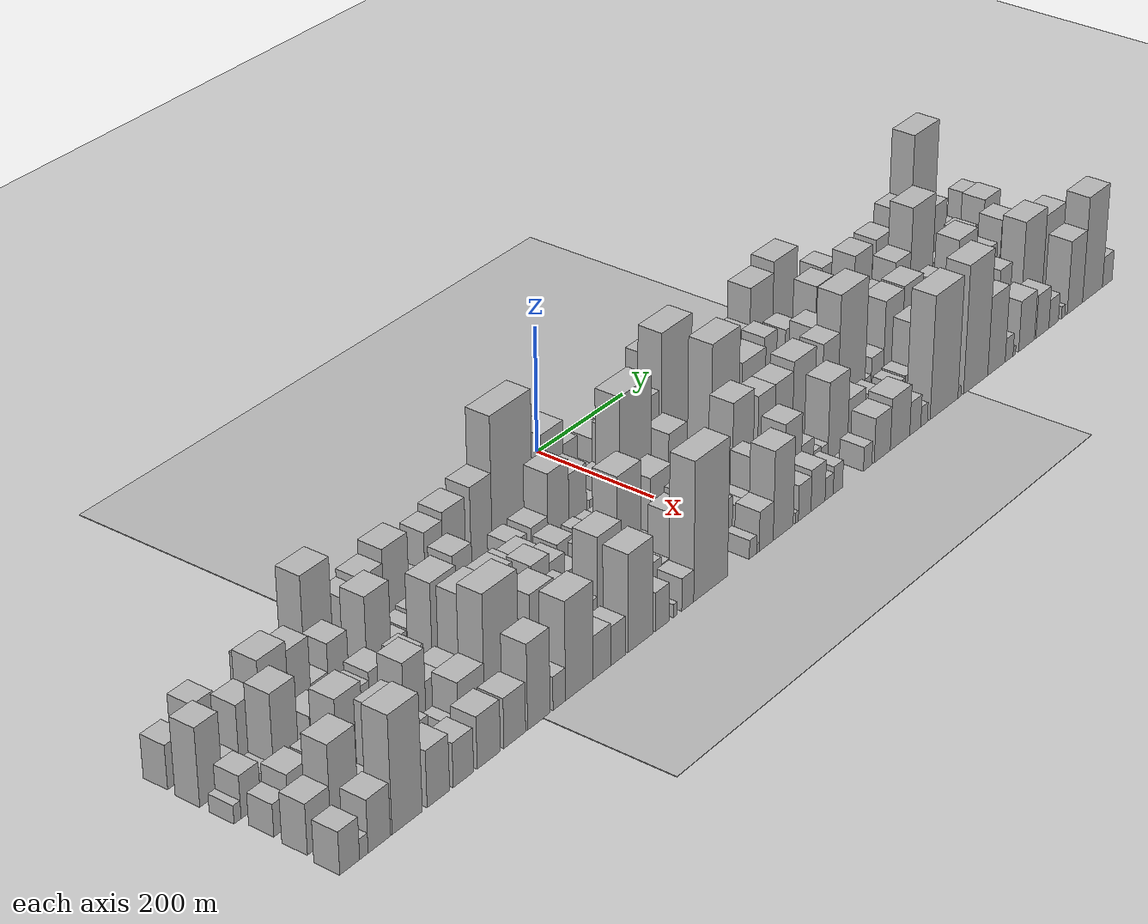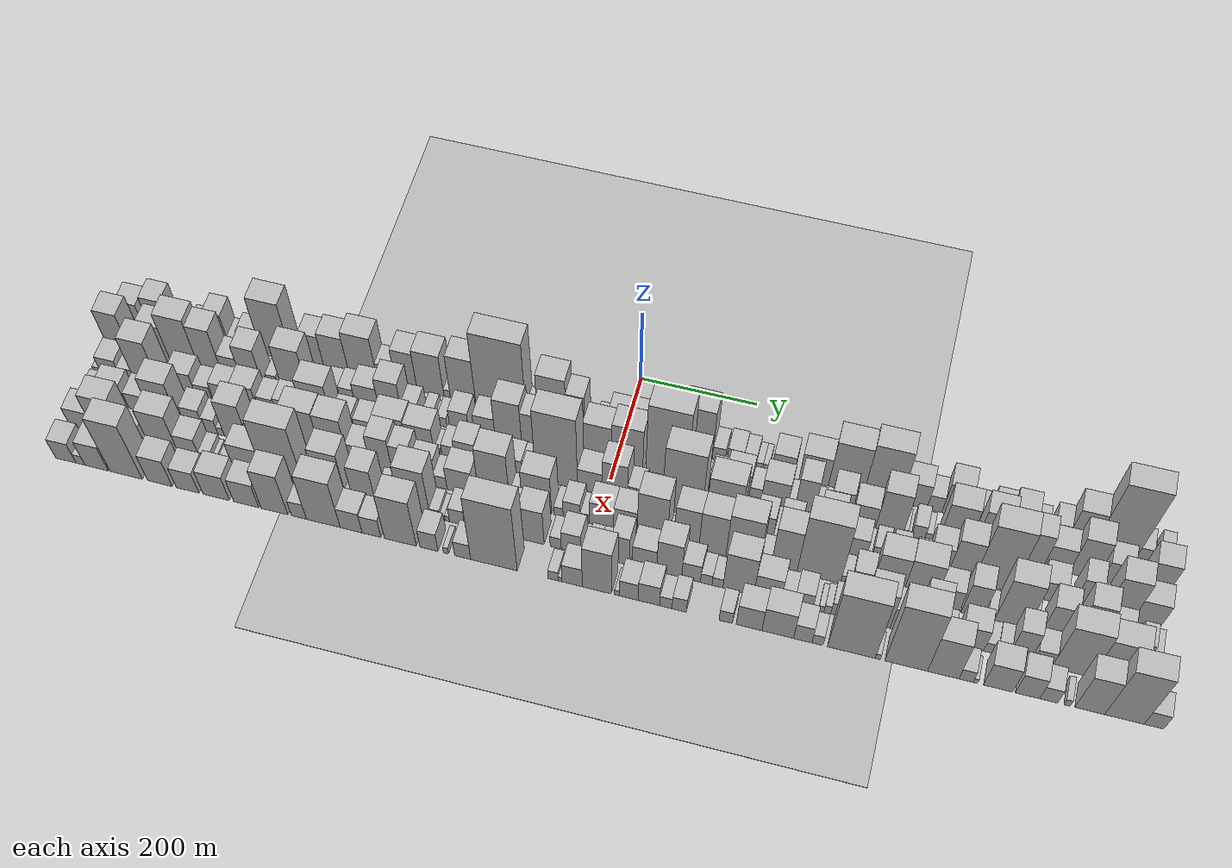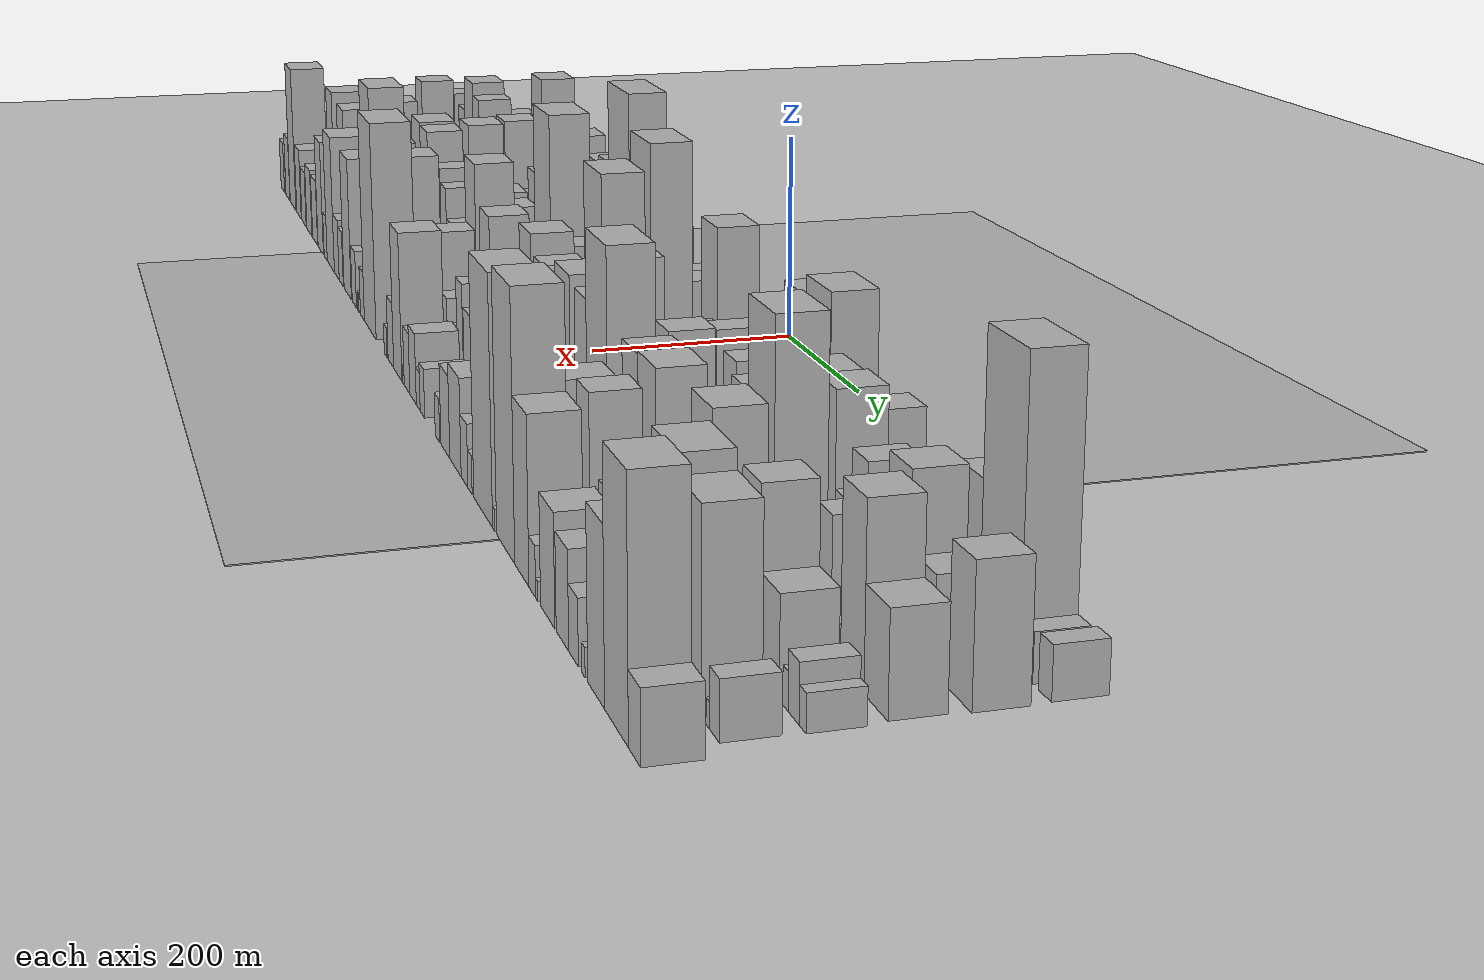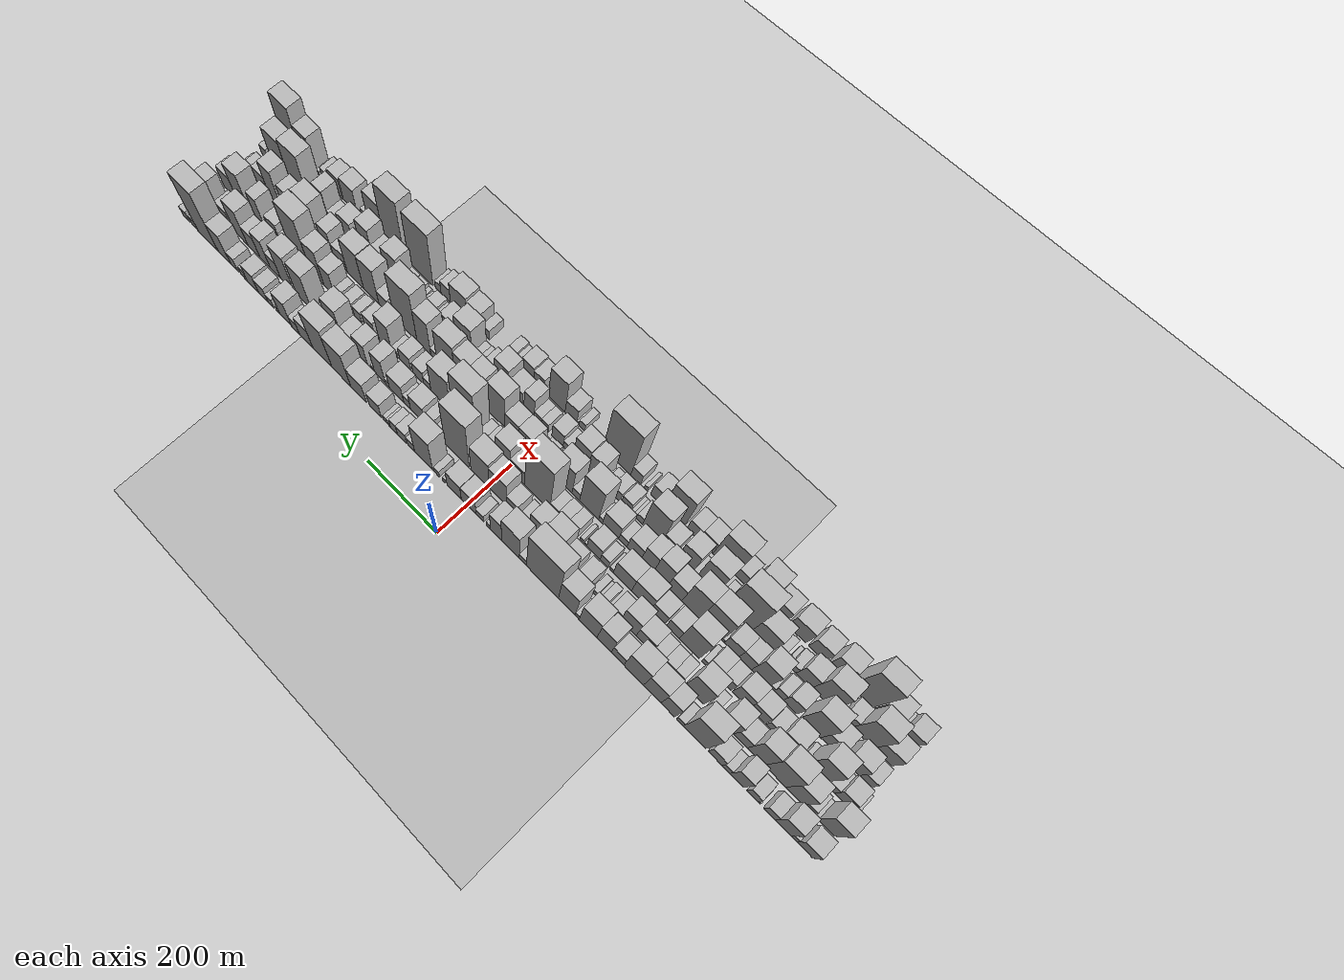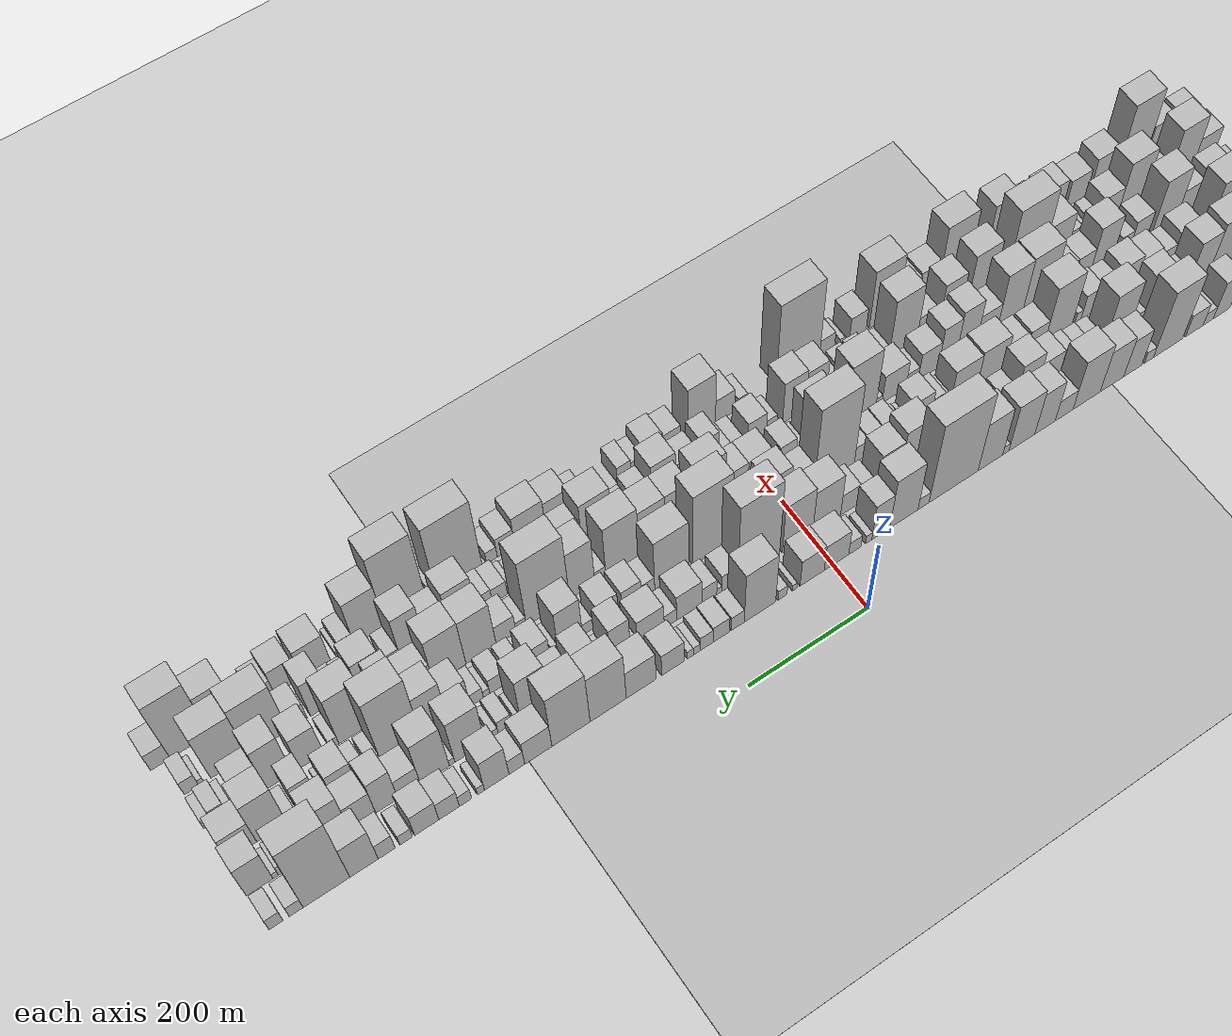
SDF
<?xml version="1.0" encoding="utf-8"?>

<sdf version="1.6">

   <world name="default">

      <gui fullscreen="0">

         <camera name="user_camera">

            <pose>-15 0 4.57585 0 0 0</pose>

            <view_controller>orbit</view_controller>

         </camera>

      </gui>

      <scene>

         <sky>

           <clouds>

             <speed>12</speed>

           </clouds>

         </sky>

         <ambient>0.4 0.4 0.4 1</ambient>

         <background>0.7 0.7 0.7 1</background>

         <shadows>1</shadows>

      </scene>

      <gravity>0 0 -9.8066</gravity>

      <magnetic_field>6e-06 2.3e-05 -4.2e-05</magnetic_field>

      <physics default="0" name="default_physics" type="ode">

         <ode>

            <solver>

               <type>quick</type>

               <iters>10</iters>

               <sor>1.0</sor>

               <use_dynamic_moi_rescaling>0</use_dynamic_moi_rescaling>

            </solver>

            <constraints>

               <cfm>0</cfm>

               <erp>0.2</erp>

               <contact_max_correcting_vel>100</contact_max_correcting_vel>

               <contact_surface_layer>0.001</contact_surface_layer>

            </constraints>

         </ode>

         <max_step_size>0.004</max_step_size>

         <real_time_factor>1</real_time_factor>

         <real_time_update_rate>250</real_time_update_rate>

      </physics>

      <light name="sun" type="directional">

         <cast_shadows>1</cast_shadows>

         <pose>0 0 10 0 0 0</pose>

         <diffuse>0.8 0.8 0.8 1</diffuse>

         <specular>0.2 0.2 0.2 1</specular>

         <attenuation>

            <range>1000</range>

            <constant>0.9</constant>

            <linear>0.01</linear>

            <quadratic>0.001</quadratic>

         </attenuation>

         <direction>-0.5 0.1 -0.9</direction>

      </light>

      <include>

         <name>ground_plane_1</name>

         <uri>model://HANNAS_ground_plane</uri>

         <pose>0 0 0  0 0 0</pose>

      </include>

      <include>

         <name>ground_plane_2</name>

         <uri>model://HANNAS_ground_plane</uri>

         <pose>100 0 0  0 0 0</pose>

      </include>

      <model name="building_1">

         <static>1</static>

         <pose frame="">100.0000 -868.0368 0 0.000000 0.000000 0.000000</pose>

         <link name="link">

            <pose frame="">0 0 33.00 0 0 0</pose>

            <collision name="collision">

               <geometry>

                  <box>

                     <size>40.0000 37.9263 66.0000</size>

                  </box>

               </geometry>

               <max_contacts>10</max_contacts>

               <surface>

                  <contact>

                     <ode/>

                  </contact>

                  <bounce/>

                  <friction>

                     <torsional>

                        <ode/>

                     </torsional>

                     <ode/>

                  </friction>

               </surface>

            </collision>

            <visual name="visual">

               <cast_shadows>0</cast_shadows>

               <geometry>

                  <box>

                     <size>40.0000 37.9263 66.0000</size>

                  </box>

               </geometry>

               <material>

                  <script>

                     <uri>model://HANNAS_wall/materials/scripts</uri>

                     <uri>model://HANNAS_wall/materials/textures</uri>

                     <name>vrc/HANNAS_wall</name>

                  </script>

               </material>

            </visual>

            <self_collide>0</self_collide>

            <enable_wind>0</enable_wind>

            <kinematic>0</kinematic>

         </link>

      </model>

      <model name="building_2">

         <static>1</static>

         <pose frame="">100.0000 -842.5686 0 0.000000 0.000000 0.000000</pose>

         <link name="link">

            <pose frame="">0 0 13.50 0 0 0</pose>

            <collision name="collision">

               <geometry>

                  <box>

                     <size>40.0000 13.0102 27.0000</size>

                  </box>

               </geometry>

               <max_contacts>10</max_contacts>

               <surface>

                  <contact>

                     <ode/>

                  </contact>

                  <bounce/>

                  <friction>

                     <torsional>

                        <ode/>

                     </torsional>

                     <ode/>

                  </friction>

               </surface>

            </collision>

            <visual name="visual">

               <cast_shadows>0</cast_shadows>

               <geometry>

                  <box>

                     <size>40.0000 13.0102 27.0000</size>

                  </box>

               </geometry>

               <material>

                  <script>

                     <uri>model://HANNAS_wall/materials/scripts</uri>

                     <uri>model://HANNAS_wall/materials/textures</uri>

                     <name>vrc/HANNAS_wall</name>

                  </script>

               </material>

            </visual>

            <self_collide>0</self_collide>

            <enable_wind>0</enable_wind>

            <kinematic>0</kinematic>

         </link>

      </model>

      <model name="building_3">

         <static>1</static>

         <pose frame="">100.0000 -817.3078 0 0.000000 0.000000 0.000000</pose>

         <link name="link">

            <pose frame="">0 0 48.00 0 0 0</pose>

            <collision name="collision">

               <geometry>

                  <box>

                     <size>40.0000 37.5114 96.0000</size>

                  </box>

               </geometry>

               <max_contacts>10</max_contacts>

               <surface>

                  <contact>

                     <ode/>

                  </contact>

                  <bounce/>

                  <friction>

                     <torsional>

                        <ode/>

                     </torsional>

                     <ode/>

                  </friction>

               </surface>

            </collision>

            <visual name="visual">

               <cast_shadows>0</cast_shadows>

               <geometry>

                  <box>

                     <size>40.0000 37.5114 96.0000</size>

                  </box>

               </geometry>

               <material>

                  <script>

                     <uri>model://HANNAS_wall/materials/scripts</uri>

                     <uri>model://HANNAS_wall/materials/textures</uri>

                     <name>vrc/HANNAS_wall</name>

                  </script>

               </material>

            </visual>

            <self_collide>0</self_collide>

            <enable_wind>0</enable_wind>

            <kinematic>0</kinematic>

         </link>

      </model>

      <model name="building_4">

         <static>1</static>

         <pose frame="">100.0000 -785.2617 0 0.000000 0.000000 0.000000</pose>

         <link name="link">

            <pose frame="">0 0 22.50 0 0 0</pose>

            <collision name="collision">

               <geometry>

                  <box>

                     <size>40.0000 26.5808 45.0000</size>

                  </box>

               </geometry>

               <max_contacts>10</max_contacts>

               <surface>

                  <contact>

                     <ode/>

                  </contact>

                  <bounce/>

                  <friction>

                     <torsional>

                        <ode/>

                     </torsional>

                     <ode/>

                  </friction>

               </surface>

            </collision>

            <visual name="visual">

               <cast_shadows>0</cast_shadows>

               <geometry>

                  <box>

                     <size>40.0000 26.5808 45.0000</size>

                  </box>

               </geometry>

               <material>

                  <script>

                     <uri>model://HANNAS_wall/materials/scripts</uri>

                     <uri>model://HANNAS_wall/materials/textures</uri>

                     <name>vrc/HANNAS_wall</name>

                  </script>

               </material>

            </visual>

            <self_collide>0</self_collide>

            <enable_wind>0</enable_wind>

            <kinematic>0</kinematic>

         </link>

      </model>

      <model name="building_5">

         <static>1</static>

         <pose frame="">100.0000 -759.9221 0 0.000000 0.000000 0.000000</pose>

         <link name="link">

            <pose frame="">0 0 7.50 0 0 0</pose>

            <collision name="collision">

               <geometry>

                  <box>

                     <size>40.0000 6.0984 15.0000</size>

                  </box>

               </geometry>

               <max_contacts>10</max_contacts>

               <surface>

                  <contact>

                     <ode/>

                  </contact>

                  <bounce/>

                  <friction>

                     <torsional>

                        <ode/>

                     </torsional>

                     <ode/>

                  </friction>

               </surface>

            </collision>

            <visual name="visual">

               <cast_shadows>0</cast_shadows>

               <geometry>

                  <box>

                     <size>40.0000 6.0984 15.0000</size>

                  </box>

               </geometry>

               <material>

                  <script>

                     <uri>model://HANNAS_wall/materials/scripts</uri>

                     <uri>model://HANNAS_wall/materials/textures</uri>

                     <name>vrc/HANNAS_wall</name>

                  </script>

               </material>

            </visual>

            <self_collide>0</self_collide>

            <enable_wind>0</enable_wind>

            <kinematic>0</kinematic>

         </link>

      </model>

      <model name="building_6">

         <static>1</static>

         <pose frame="">100.0000 -744.2797 0 0.000000 0.000000 0.000000</pose>

         <link name="link">

            <pose frame="">0 0 24.00 0 0 0</pose>

            <collision name="collision">

               <geometry>

                  <box>

                     <size>40.0000 25.1863 48.0000</size>

                  </box>

               </geometry>

               <max_contacts>10</max_contacts>

               <surface>

                  <contact>

                     <ode/>

                  </contact>

                  <bounce/>

                  <friction>

                     <torsional>

                        <ode/>

                     </torsional>

                     <ode/>

                  </friction>

               </surface>

            </collision>

            <visual name="visual">

               <cast_shadows>0</cast_shadows>

               <geometry>

                  <box>

                     <size>40.0000 25.1863 48.0000</size>

                  </box>

               </geometry>

               <material>

                  <script>

                     <uri>model://HANNAS_wall/materials/scripts</uri>

                     <uri>model://HANNAS_wall/materials/textures</uri>

                     <name>vrc/HANNAS_wall</name>

                  </script>

               </material>

            </visual>

            <self_collide>0</self_collide>

            <enable_wind>0</enable_wind>

            <kinematic>0</kinematic>

         </link>

      </model>

      <model name="building_7">

         <static>1</static>

         <pose frame="">100.0000 -707.6128 0 0.000000 0.000000 0.000000</pose>

         <link name="link">

            <pose frame="">0 0 48.00 0 0 0</pose>

            <collision name="collision">

               <geometry>

                  <box>

                     <size>40.0000 32.1476 96.0000</size>

                  </box>

               </geometry>

               <max_contacts>10</max_contacts>

               <surface>

                  <contact>

                     <ode/>

                  </contact>

                  <bounce/>

                  <friction>

                     <torsional>

                        <ode/>

                     </torsional>

                     <ode/>

                  </friction>

               </surface>

            </collision>

            <visual name="visual">

               <cast_shadows>0</cast_shadows>

               <geometry>

                  <box>

                     <size>40.0000 32.1476 96.0000</size>

                  </box>

               </geometry>

               <material>

                  <script>

                     <uri>model://HANNAS_wall/materials/scripts</uri>

                     <uri>model://HANNAS_wall/materials/textures</uri>

                     <name>vrc/HANNAS_wall</name>

                  </script>

               </material>

            </visual>

            <self_collide>0</self_collide>

            <enable_wind>0</enable_wind>

            <kinematic>0</kinematic>

         </link>

      </model>

      <model name="building_8">

         <static>1</static>

         <pose frame="">100.0000 -681.8017 0 0.000000 0.000000 0.000000</pose>

         <link name="link">

            <pose frame="">0 0 16.50 0 0 0</pose>

            <collision name="collision">

               <geometry>

                  <box>

                     <size>40.0000 19.4746 33.0000</size>

                  </box>

               </geometry>

               <max_contacts>10</max_contacts>

               <surface>

                  <contact>

                     <ode/>

                  </contact>

                  <bounce/>

                  <friction>

                     <torsional>

                        <ode/>

                     </torsional>

                     <ode/>

                  </friction>

               </surface>

            </collision>

            <visual name="visual">

               <cast_shadows>0</cast_shadows>

               <geometry>

                  <box>

                     <size>40.0000 19.4746 33.0000</size>

                  </box>

               </geometry>

               <material>

                  <script>

                     <uri>model://HANNAS_wall/materials/scripts</uri>

                     <uri>model://HANNAS_wall/materials/textures</uri>

                     <name>vrc/HANNAS_wall</name>

                  </script>

               </material>

            </visual>

            <self_collide>0</self_collide>

            <enable_wind>0</enable_wind>

            <kinematic>0</kinematic>

         </link>

      </model>

      <model name="building_9">

         <static>1</static>

         <pose frame="">100.0000 -655.2285 0 0.000000 0.000000 0.000000</pose>

         <link name="link">

            <pose frame="">0 0 28.50 0 0 0</pose>

            <collision name="collision">

               <geometry>

                  <box>

                     <size>40.0000 33.6718 57.0000</size>

                  </box>

               </geometry>

               <max_contacts>10</max_contacts>

               <surface>

                  <contact>

                     <ode/>

                  </contact>

                  <bounce/>

                  <friction>

                     <torsional>

                        <ode/>

                     </torsional>

                     <ode/>

                  </friction>

               </surface>

            </collision>

            <visual name="visual">

               <cast_shadows>0</cast_shadows>

               <geometry>

                  <box>

                     <size>40.0000 33.6718 57.0000</size>

                  </box>

               </geometry>

               <material>

                  <script>

                     <uri>model://HANNAS_wall/materials/scripts</uri>

                     <uri>model://HANNAS_wall/materials/textures</uri>

                     <name>vrc/HANNAS_wall</name>

                  </script>

               </material>

            </visual>

            <self_collide>0</self_collide>

            <enable_wind>0</enable_wind>

            <kinematic>0</kinematic>

         </link>

      </model>

      <model name="building_10">

         <static>1</static>

         <pose frame="">100.0000 -604.8652 0 0.000000 0.000000 0.000000</pose>

         <link name="link">

            <pose frame="">0 0 87.00 0 0 0</pose>

            <collision name="collision">

               <geometry>

                  <box>

                     <size>40.0000 55.0547 174.0000</size>

                  </box>

               </geometry>

               <max_contacts>10</max_contacts>

               <surface>

                  <contact>

                     <ode/>

                  </contact>

                  <bounce/>

                  <friction>

                     <torsional>

                        <ode/>

                     </torsional>

                     <ode/>

                  </friction>

               </surface>

            </collision>

            <visual name="visual">

               <cast_shadows>0</cast_shadows>

               <geometry>

                  <box>

                     <size>40.0000 55.0547 174.0000</size>

                  </box>

               </geometry>

               <material>

                  <script>

                     <uri>model://HANNAS_wall/materials/scripts</uri>

                     <uri>model://HANNAS_wall/materials/textures</uri>

                     <name>vrc/HANNAS_wall</name>

                  </script>

               </material>

            </visual>

            <self_collide>0</self_collide>

            <enable_wind>0</enable_wind>

            <kinematic>0</kinematic>

         </link>

      </model>

      <model name="building_11">

         <static>1</static>

         <pose frame="">100.0000 -568.7729 0 0.000000 0.000000 0.000000</pose>

         <link name="link">

            <pose frame="">0 0 15.00 0 0 0</pose>

            <collision name="collision">

               <geometry>

                  <box>

                     <size>40.0000 17.1299 30.0000</size>

                  </box>

               </geometry>

               <max_contacts>10</max_contacts>

               <surface>

                  <contact>

                     <ode/>

                  </contact>

                  <bounce/>

                  <friction>

                     <torsional>

                        <ode/>

                     </torsional>

                     <ode/>

                  </friction>

               </surface>

            </collision>

            <visual name="visual">

               <cast_shadows>0</cast_shadows>

               <geometry>

                  <box>

                     <size>40.0000 17.1299 30.0000</size>

                  </box>

               </geometry>

               <material>

                  <script>

                     <uri>model://HANNAS_wall/materials/scripts</uri>

                     <uri>model://HANNAS_wall/materials/textures</uri>

                     <name>vrc/HANNAS_wall</name>

                  </script>

               </material>

            </visual>

            <self_collide>0</self_collide>

            <enable_wind>0</enable_wind>

            <kinematic>0</kinematic>

         </link>

      </model>

      <model name="building_12">

         <static>1</static>

         <pose frame="">100.0000 -538.1384 0 0.000000 0.000000 0.000000</pose>

         <link name="link">

            <pose frame="">0 0 49.50 0 0 0</pose>

            <collision name="collision">

               <geometry>

                  <box>

                     <size>40.0000 34.1391 99.0000</size>

                  </box>

               </geometry>

               <max_contacts>10</max_contacts>

               <surface>

                  <contact>

                     <ode/>

                  </contact>

                  <bounce/>

                  <friction>

                     <torsional>

                        <ode/>

                     </torsional>

                     <ode/>

                  </friction>

               </surface>

            </collision>

            <visual name="visual">

               <cast_shadows>0</cast_shadows>

               <geometry>

                  <box>

                     <size>40.0000 34.1391 99.0000</size>

                  </box>

               </geometry>

               <material>

                  <script>

                     <uri>model://HANNAS_wall/materials/scripts</uri>

                     <uri>model://HANNAS_wall/materials/textures</uri>

                     <name>vrc/HANNAS_wall</name>

                  </script>

               </material>

            </visual>

            <self_collide>0</self_collide>

            <enable_wind>0</enable_wind>

            <kinematic>0</kinematic>

         </link>

      </model>

      <model name="building_13">

         <static>1</static>

         <pose frame="">100.0000 -499.0372 0 0.000000 0.000000 0.000000</pose>

         <link name="link">

            <pose frame="">0 0 55.50 0 0 0</pose>

            <collision name="collision">

               <geometry>

                  <box>

                     <size>40.0000 44.0632 111.0000</size>

                  </box>

               </geometry>

               <max_contacts>10</max_contacts>

               <surface>

                  <contact>

                     <ode/>

                  </contact>

                  <bounce/>

                  <friction>

                     <torsional>

                        <ode/>

                     </torsional>

                     <ode/>

                  </friction>

               </surface>

            </collision>

            <visual name="visual">

               <cast_shadows>0</cast_shadows>

               <geometry>

                  <box>

                     <size>40.0000 44.0632 111.0000</size>

                  </box>

               </geometry>

               <material>

                  <script>

                     <uri>model://HANNAS_wall/materials/scripts</uri>

                     <uri>model://HANNAS_wall/materials/textures</uri>

                     <name>vrc/HANNAS_wall</name>

                  </script>

               </material>

            </visual>

            <self_collide>0</self_collide>

            <enable_wind>0</enable_wind>

            <kinematic>0</kinematic>

         </link>

      </model>

      <model name="building_14">

         <static>1</static>

         <pose frame="">100.0000 -451.7591 0 0.000000 0.000000 0.000000</pose>

         <link name="link">

            <pose frame="">0 0 66.00 0 0 0</pose>

            <collision name="collision">

               <geometry>

                  <box>

                     <size>40.0000 50.4930 132.0000</size>

                  </box>

               </geometry>

               <max_contacts>10</max_contacts>

               <surface>

                  <contact>

                     <ode/>

                  </contact>

                  <bounce/>

                  <friction>

                     <torsional>

                        <ode/>

                     </torsional>

                     <ode/>

                  </friction>

               </surface>

            </collision>

            <visual name="visual">

               <cast_shadows>0</cast_shadows>

               <geometry>

                  <box>

                     <size>40.0000 50.4930 132.0000</size>

                  </box>

               </geometry>

               <material>

                  <script>

                     <uri>model://HANNAS_wall/materials/scripts</uri>

                     <uri>model://HANNAS_wall/materials/textures</uri>

                     <name>vrc/HANNAS_wall</name>

                  </script>

               </material>

            </visual>

            <self_collide>0</self_collide>

            <enable_wind>0</enable_wind>

            <kinematic>0</kinematic>

         </link>

      </model>

      <model name="building_15">

         <static>1</static>

         <pose frame="">100.0000 -410.1118 0 0.000000 0.000000 0.000000</pose>

         <link name="link">

            <pose frame="">0 0 28.50 0 0 0</pose>

            <collision name="collision">

               <geometry>

                  <box>

                     <size>40.0000 32.8017 57.0000</size>

                  </box>

               </geometry>

               <max_contacts>10</max_contacts>

               <surface>

                  <contact>

                     <ode/>

                  </contact>

                  <bounce/>

                  <friction>

                     <torsional>

                        <ode/>

                     </torsional>

                     <ode/>

                  </friction>

               </surface>

            </collision>

            <visual name="visual">

               <cast_shadows>0</cast_shadows>

               <geometry>

                  <box>

                     <size>40.0000 32.8017 57.0000</size>

                  </box>

               </geometry>

               <material>

                  <script>

                     <uri>model://HANNAS_wall/materials/scripts</uri>

                     <uri>model://HANNAS_wall/materials/textures</uri>

                     <name>vrc/HANNAS_wall</name>

                  </script>

               </material>

            </visual>

            <self_collide>0</self_collide>

            <enable_wind>0</enable_wind>

            <kinematic>0</kinematic>

         </link>

      </model>

      <model name="building_16">

         <static>1</static>

         <pose frame="">100.0000 -375.1171 0 0.000000 0.000000 0.000000</pose>

         <link name="link">

            <pose frame="">0 0 57.00 0 0 0</pose>

            <collision name="collision">

               <geometry>

                  <box>

                     <size>40.0000 37.1876 114.0000</size>

                  </box>

               </geometry>

               <max_contacts>10</max_contacts>

               <surface>

                  <contact>

                     <ode/>

                  </contact>

                  <bounce/>

                  <friction>

                     <torsional>

                        <ode/>

                     </torsional>

                     <ode/>

                  </friction>

               </surface>

            </collision>

            <visual name="visual">

               <cast_shadows>0</cast_shadows>

               <geometry>

                  <box>

                     <size>40.0000 37.1876 114.0000</size>

                  </box>

               </geometry>

               <material>

                  <script>

                     <uri>model://HANNAS_wall/materials/scripts</uri>

                     <uri>model://HANNAS_wall/materials/textures</uri>

                     <name>vrc/HANNAS_wall</name>

                  </script>

               </material>

            </visual>

            <self_collide>0</self_collide>

            <enable_wind>0</enable_wind>

            <kinematic>0</kinematic>

         </link>

      </model>

      <model name="building_17">

         <static>1</static>

         <pose frame="">100.0000 -333.0066 0 0.000000 0.000000 0.000000</pose>

         <link name="link">

            <pose frame="">0 0 63.00 0 0 0</pose>

            <collision name="collision">

               <geometry>

                  <box>

                     <size>40.0000 47.0333 126.0000</size>

                  </box>

               </geometry>

               <max_contacts>10</max_contacts>

               <surface>

                  <contact>

                     <ode/>

                  </contact>

                  <bounce/>

                  <friction>

                     <torsional>

                        <ode/>

                     </torsional>

                     <ode/>

                  </friction>

               </surface>

            </collision>

            <visual name="visual">

               <cast_shadows>0</cast_shadows>

               <geometry>

                  <box>

                     <size>40.0000 47.0333 126.0000</size>

                  </box>

               </geometry>

               <material>

                  <script>

                     <uri>model://HANNAS_wall/materials/scripts</uri>

                     <uri>model://HANNAS_wall/materials/textures</uri>

                     <name>vrc/HANNAS_wall</name>

                  </script>

               </material>

            </visual>

            <self_collide>0</self_collide>

            <enable_wind>0</enable_wind>

            <kinematic>0</kinematic>

         </link>

      </model>

      <model name="building_18">

         <static>1</static>

         <pose frame="">100.0000 -303.9368 0 0.000000 0.000000 0.000000</pose>

         <link name="link">

            <pose frame="">0 0 12.00 0 0 0</pose>

            <collision name="collision">

               <geometry>

                  <box>

                     <size>40.0000 11.1064 24.0000</size>

                  </box>

               </geometry>

               <max_contacts>10</max_contacts>

               <surface>

                  <contact>

                     <ode/>

                  </contact>

                  <bounce/>

                  <friction>

                     <torsional>

                        <ode/>

                     </torsional>

                     <ode/>

                  </friction>

               </surface>

            </collision>

            <visual name="visual">

               <cast_shadows>0</cast_shadows>

               <geometry>

                  <box>

                     <size>40.0000 11.1064 24.0000</size>

                  </box>

               </geometry>

               <material>

                  <script>

                     <uri>model://HANNAS_wall/materials/scripts</uri>

                     <uri>model://HANNAS_wall/materials/textures</uri>

                     <name>vrc/HANNAS_wall</name>

                  </script>

               </material>

            </visual>

            <self_collide>0</self_collide>

            <enable_wind>0</enable_wind>

            <kinematic>0</kinematic>

         </link>

      </model>

      <model name="building_19">

         <static>1</static>

         <pose frame="">100.0000 -276.0920 0 0.000000 0.000000 0.000000</pose>

         <link name="link">

            <pose frame="">0 0 67.50 0 0 0</pose>

            <collision name="collision">

               <geometry>

                  <box>

                     <size>40.0000 44.5833 135.0000</size>

                  </box>

               </geometry>

               <max_contacts>10</max_contacts>

               <surface>

                  <contact>

                     <ode/>

                  </contact>

                  <bounce/>

                  <friction>

                     <torsional>

                        <ode/>

                     </torsional>

                     <ode/>

                  </friction>

               </surface>

            </collision>

            <visual name="visual">

               <cast_shadows>0</cast_shadows>

               <geometry>

                  <box>

                     <size>40.0000 44.5833 135.0000</size>

                  </box>

               </geometry>

               <material>

                  <script>

                     <uri>model://HANNAS_wall/materials/scripts</uri>

                     <uri>model://HANNAS_wall/materials/textures</uri>

                     <name>vrc/HANNAS_wall</name>

                  </script>

               </material>

            </visual>

            <self_collide>0</self_collide>

            <enable_wind>0</enable_wind>

            <kinematic>0</kinematic>

         </link>

      </model>

      <model name="building_20">

         <static>1</static>

         <pose frame="">100.0000 -210.1703 0 0.000000 0.000000 0.000000</pose>

         <link name="link">

            <pose frame="">0 0 111.00 0 0 0</pose>

            <collision name="collision">

               <geometry>

                  <box>

                     <size>40.0000 87.2600 222.0000</size>

                  </box>

               </geometry>

               <max_contacts>10</max_contacts>

               <surface>

                  <contact>

                     <ode/>

                  </contact>

                  <bounce/>

                  <friction>

                     <torsional>

                        <ode/>

                     </torsional>

                     <ode/>

                  </friction>

               </surface>

            </collision>

            <visual name="visual">

               <cast_shadows>0</cast_shadows>

               <geometry>

                  <box>

                     <size>40.0000 87.2600 222.0000</size>

                  </box>

               </geometry>

               <material>

                  <script>

                     <uri>model://HANNAS_wall/materials/scripts</uri>

                     <uri>model://HANNAS_wall/materials/textures</uri>

                     <name>vrc/HANNAS_wall</name>

                  </script>

               </material>

            </visual>

            <self_collide>0</self_collide>

            <enable_wind>0</enable_wind>

            <kinematic>0</kinematic>

         </link>

      </model>

      <model name="building_21">

         <static>1</static>

         <pose frame="">100.0000 -156.7400 0 0.000000 0.000000 0.000000</pose>

         <link name="link">

            <pose frame="">0 0 16.50 0 0 0</pose>

            <collision name="collision">

               <geometry>

                  <box>

                     <size>40.0000 19.6007 33.0000</size>

                  </box>

               </geometry>

               <max_contacts>10</max_contacts>

               <surface>

                  <contact>

                     <ode/>

                  </contact>

                  <bounce/>

                  <friction>

                     <torsional>

                        <ode/>

                     </torsional>

                     <ode/>

                  </friction>

               </surface>

            </collision>

            <visual name="visual">

               <cast_shadows>0</cast_shadows>

               <geometry>

                  <box>

                     <size>40.0000 19.6007 33.0000</size>

                  </box>

               </geometry>

               <material>

                  <script>

                     <uri>model://HANNAS_wall/materials/scripts</uri>

                     <uri>model://HANNAS_wall/materials/textures</uri>

                     <name>vrc/HANNAS_wall</name>

                  </script>

               </material>

            </visual>

            <self_collide>0</self_collide>

            <enable_wind>0</enable_wind>

            <kinematic>0</kinematic>

         </link>

      </model>

      <model name="building_22">

         <static>1</static>

         <pose frame="">100.0000 -122.1969 0 0.000000 0.000000 0.000000</pose>

         <link name="link">

            <pose frame="">0 0 70.50 0 0 0</pose>

            <collision name="collision">

               <geometry>

                  <box>

                     <size>40.0000 49.4855 141.0000</size>

                  </box>

               </geometry>

               <max_contacts>10</max_contacts>

               <surface>

                  <contact>

                     <ode/>

                  </contact>

                  <bounce/>

                  <friction>

                     <torsional>

                        <ode/>

                     </torsional>

                     <ode/>

                  </friction>

               </surface>

            </collision>

            <visual name="visual">

               <cast_shadows>0</cast_shadows>

               <geometry>

                  <box>

                     <size>40.0000 49.4855 141.0000</size>

                  </box>

               </geometry>

               <material>

                  <script>

                     <uri>model://HANNAS_wall/materials/scripts</uri>

                     <uri>model://HANNAS_wall/materials/textures</uri>

                     <name>vrc/HANNAS_wall</name>

                  </script>

               </material>

            </visual>

            <self_collide>0</self_collide>

            <enable_wind>0</enable_wind>

            <kinematic>0</kinematic>

         </link>

      </model>

      <model name="building_23">

         <static>1</static>

         <pose frame="">100.0000 -81.7811 0 0.000000 0.000000 0.000000</pose>

         <link name="link">

            <pose frame="">0 0 51.00 0 0 0</pose>

            <collision name="collision">

               <geometry>

                  <box>

                     <size>40.0000 31.3461 102.0000</size>

                  </box>

               </geometry>

               <max_contacts>10</max_contacts>

               <surface>

                  <contact>

                     <ode/>

                  </contact>

                  <bounce/>

                  <friction>

                     <torsional>

                        <ode/>

                     </torsional>

                     <ode/>

                  </friction>

               </surface>

            </collision>

            <visual name="visual">

               <cast_shadows>0</cast_shadows>

               <geometry>

                  <box>

                     <size>40.0000 31.3461 102.0000</size>

                  </box>

               </geometry>

               <material>

                  <script>

                     <uri>model://HANNAS_wall/materials/scripts</uri>

                     <uri>model://HANNAS_wall/materials/textures</uri>

                     <name>vrc/HANNAS_wall</name>

                  </script>

               </material>

            </visual>

            <self_collide>0</self_collide>

            <enable_wind>0</enable_wind>

            <kinematic>0</kinematic>

         </link>

      </model>

      <model name="building_24">

         <static>1</static>

         <pose frame="">100.0000 -60.7981 0 0.000000 0.000000 0.000000</pose>

         <link name="link">

            <pose frame="">0 0 12.00 0 0 0</pose>

            <collision name="collision">

               <geometry>

                  <box>

                     <size>40.0000 10.6198 24.0000</size>

                  </box>

               </geometry>

               <max_contacts>10</max_contacts>

               <surface>

                  <contact>

                     <ode/>

                  </contact>

                  <bounce/>

                  <friction>

                     <torsional>

                        <ode/>

                     </torsional>

                     <ode/>

                  </friction>

               </surface>

            </collision>

            <visual name="visual">

               <cast_shadows>0</cast_shadows>

               <geometry>

                  <box>

                     <size>40.0000 10.6198 24.0000</size>

                  </box>

               </geometry>

               <material>

                  <script>

                     <uri>model://HANNAS_wall/materials/scripts</uri>

                     <uri>model://HANNAS_wall/materials/textures</uri>

                     <name>vrc/HANNAS_wall</name>

                  </script>

               </material>

            </visual>

            <self_collide>0</self_collide>

            <enable_wind>0</enable_wind>

            <kinematic>0</kinematic>

         </link>

      </model>

      <model name="building_25">

         <static>1</static>

         <pose frame="">100.0000 -36.8509 0 0.000000 0.000000 0.000000</pose>

         <link name="link">

            <pose frame="">0 0 18.00 0 0 0</pose>

            <collision name="collision">

               <geometry>

                  <box>

                     <size>40.0000 21.2747 36.0000</size>

                  </box>

               </geometry>

               <max_contacts>10</max_contacts>

               <surface>

                  <contact>

                     <ode/>

                  </contact>

                  <bounce/>

                  <friction>

                     <torsional>

                        <ode/>

                     </torsional>

                     <ode/>

                  </friction>

               </surface>

            </collision>

            <visual name="visual">

               <cast_shadows>0</cast_shadows>

               <geometry>

                  <box>

                     <size>40.0000 21.2747 36.0000</size>

                  </box>

               </geometry>

               <material>

                  <script>

                     <uri>model://HANNAS_wall/materials/scripts</uri>

                     <uri>model://HANNAS_wall/materials/textures</uri>

                     <name>vrc/HANNAS_wall</name>

                  </script>

               </material>

            </visual>

            <self_collide>0</self_collide>

            <enable_wind>0</enable_wind>

            <kinematic>0</kinematic>

         </link>

      </model>

      <model name="building_26">

         <static>1</static>

         <pose frame="">100.0000 -5.1688 0 0.000000 0.000000 0.000000</pose>

         <link name="link">

            <pose frame="">0 0 37.50 0 0 0</pose>

            <collision name="collision">

               <geometry>

                  <box>

                     <size>40.0000 42.0895 75.0000</size>

                  </box>

               </geometry>

               <max_contacts>10</max_contacts>

               <surface>

                  <contact>

                     <ode/>

                  </contact>

                  <bounce/>

                  <friction>

                     <torsional>

                        <ode/>

                     </torsional>

                     <ode/>

                  </friction>

               </surface>

            </collision>

            <visual name="visual">

               <cast_shadows>0</cast_shadows>

               <geometry>

                  <box>

                     <size>40.0000 42.0895 75.0000</size>

                  </box>

               </geometry>

               <material>

                  <script>

                     <uri>model://HANNAS_wall/materials/scripts</uri>

                     <uri>model://HANNAS_wall/materials/textures</uri>

                     <name>vrc/HANNAS_wall</name>

                  </script>

               </material>

            </visual>

            <self_collide>0</self_collide>

            <enable_wind>0</enable_wind>

            <kinematic>0</kinematic>

         </link>

      </model>

      <model name="building_27">

         <static>1</static>

         <pose frame="">100.0000 36.4722 0 0.000000 0.000000 0.000000</pose>

         <link name="link">

            <pose frame="">0 0 39.00 0 0 0</pose>

            <collision name="collision">

               <geometry>

                  <box>

                     <size>40.0000 41.1924 78.0000</size>

                  </box>

               </geometry>

               <max_contacts>10</max_contacts>

               <surface>

                  <contact>

                     <ode/>

                  </contact>

                  <bounce/>

                  <friction>

                     <torsional>

                        <ode/>

                     </torsional>

                     <ode/>

                  </friction>

               </surface>

            </collision>

            <visual name="visual">

               <cast_shadows>0</cast_shadows>

               <geometry>

                  <box>

                     <size>40.0000 41.1924 78.0000</size>

                  </box>

               </geometry>

               <material>

                  <script>

                     <uri>model://HANNAS_wall/materials/scripts</uri>

                     <uri>model://HANNAS_wall/materials/textures</uri>

                     <name>vrc/HANNAS_wall</name>

                  </script>

               </material>

            </visual>

            <self_collide>0</self_collide>

            <enable_wind>0</enable_wind>

            <kinematic>0</kinematic>

         </link>

      </model>

      <model name="building_28">

         <static>1</static>

         <pose frame="">100.0000 66.0425 0 0.000000 0.000000 0.000000</pose>

         <link name="link">

            <pose frame="">0 0 9.00 0 0 0</pose>

            <collision name="collision">

               <geometry>

                  <box>

                     <size>40.0000 7.9484 18.0000</size>

                  </box>

               </geometry>

               <max_contacts>10</max_contacts>

               <surface>

                  <contact>

                     <ode/>

                  </contact>

                  <bounce/>

                  <friction>

                     <torsional>

                        <ode/>

                     </torsional>

                     <ode/>

                  </friction>

               </surface>

            </collision>

            <visual name="visual">

               <cast_shadows>0</cast_shadows>

               <geometry>

                  <box>

                     <size>40.0000 7.9484 18.0000</size>

                  </box>

               </geometry>

               <material>

                  <script>

                     <uri>model://HANNAS_wall/materials/scripts</uri>

                     <uri>model://HANNAS_wall/materials/textures</uri>

                     <name>vrc/HANNAS_wall</name>

                  </script>

               </material>

            </visual>

            <self_collide>0</self_collide>

            <enable_wind>0</enable_wind>

            <kinematic>0</kinematic>

         </link>

      </model>

      <model name="building_29">

         <static>1</static>

         <pose frame="">100.0000 86.7288 0 0.000000 0.000000 0.000000</pose>

         <link name="link">

            <pose frame="">0 0 15.00 0 0 0</pose>

            <collision name="collision">

               <geometry>

                  <box>

                     <size>40.0000 15.4241 30.0000</size>

                  </box>

               </geometry>

               <max_contacts>10</max_contacts>

               <surface>

                  <contact>

                     <ode/>

                  </contact>

                  <bounce/>

                  <friction>

                     <torsional>

                        <ode/>

                     </torsional>

                     <ode/>

                  </friction>

               </surface>

            </collision>

            <visual name="visual">

               <cast_shadows>0</cast_shadows>

               <geometry>

                  <box>

                     <size>40.0000 15.4241 30.0000</size>

                  </box>

               </geometry>

               <material>

                  <script>

                     <uri>model://HANNAS_wall/materials/scripts</uri>

                     <uri>model://HANNAS_wall/materials/textures</uri>

                     <name>vrc/HANNAS_wall</name>

                  </script>

               </material>

            </visual>

            <self_collide>0</self_collide>

            <enable_wind>0</enable_wind>

            <kinematic>0</kinematic>

         </link>

      </model>

      <model name="building_30">

         <static>1</static>

         <pose frame="">100.0000 124.8338 0 0.000000 0.000000 0.000000</pose>

         <link name="link">

            <pose frame="">0 0 75.00 0 0 0</pose>

            <collision name="collision">

               <geometry>

                  <box>

                     <size>40.0000 52.7860 150.0000</size>

                  </box>

               </geometry>

               <max_contacts>10</max_contacts>

               <surface>

                  <contact>

                     <ode/>

                  </contact>

                  <bounce/>

                  <friction>

                     <torsional>

                        <ode/>

                     </torsional>

                     <ode/>

                  </friction>

               </surface>

            </collision>

            <visual name="visual">

               <cast_shadows>0</cast_shadows>

               <geometry>

                  <box>

                     <size>40.0000 52.7860 150.0000</size>

                  </box>

               </geometry>

               <material>

                  <script>

                     <uri>model://HANNAS_wall/materials/scripts</uri>

                     <uri>model://HANNAS_wall/materials/textures</uri>

                     <name>vrc/HANNAS_wall</name>

                  </script>

               </material>

            </visual>

            <self_collide>0</self_collide>

            <enable_wind>0</enable_wind>

            <kinematic>0</kinematic>

         </link>

      </model>

      <model name="building_31">

         <static>1</static>

         <pose frame="">100.0000 161.9882 0 0.000000 0.000000 0.000000</pose>

         <link name="link">

            <pose frame="">0 0 21.00 0 0 0</pose>

            <collision name="collision">

               <geometry>

                  <box>

                     <size>40.0000 21.5227 42.0000</size>

                  </box>

               </geometry>

               <max_contacts>10</max_contacts>

               <surface>

                  <contact>

                     <ode/>

                  </contact>

                  <bounce/>

                  <friction>

                     <torsional>

                        <ode/>

                     </torsional>

                     <ode/>

                  </friction>

               </surface>

            </collision>

            <visual name="visual">

               <cast_shadows>0</cast_shadows>

               <geometry>

                  <box>

                     <size>40.0000 21.5227 42.0000</size>

                  </box>

               </geometry>

               <material>

                  <script>

                     <uri>model://HANNAS_wall/materials/scripts</uri>

                     <uri>model://HANNAS_wall/materials/textures</uri>

                     <name>vrc/HANNAS_wall</name>

                  </script>

               </material>

            </visual>

            <self_collide>0</self_collide>

            <enable_wind>0</enable_wind>

            <kinematic>0</kinematic>

         </link>

      </model>

      <model name="building_32">

         <static>1</static>

         <pose frame="">100.0000 189.4011 0 0.000000 0.000000 0.000000</pose>

         <link name="link">

            <pose frame="">0 0 24.00 0 0 0</pose>

            <collision name="collision">

               <geometry>

                  <box>

                     <size>40.0000 27.3031 48.0000</size>

                  </box>

               </geometry>

               <max_contacts>10</max_contacts>

               <surface>

                  <contact>

                     <ode/>

                  </contact>

                  <bounce/>

                  <friction>

                     <torsional>

                        <ode/>

                     </torsional>

                     <ode/>

                  </friction>

               </surface>

            </collision>

            <visual name="visual">

               <cast_shadows>0</cast_shadows>

               <geometry>

                  <box>

                     <size>40.0000 27.3031 48.0000</size>

                  </box>

               </geometry>

               <material>

                  <script>

                     <uri>model://HANNAS_wall/materials/scripts</uri>

                     <uri>model://HANNAS_wall/materials/textures</uri>

                     <name>vrc/HANNAS_wall</name>

                  </script>

               </material>

            </visual>

            <self_collide>0</self_collide>

            <enable_wind>0</enable_wind>

            <kinematic>0</kinematic>

         </link>

      </model>

      <model name="building_33">

         <static>1</static>

         <pose frame="">100.0000 213.6342 0 0.000000 0.000000 0.000000</pose>

         <link name="link">

            <pose frame="">0 0 21.00 0 0 0</pose>

            <collision name="collision">

               <geometry>

                  <box>

                     <size>40.0000 21.1630 42.0000</size>

                  </box>

               </geometry>

               <max_contacts>10</max_contacts>

               <surface>

                  <contact>

                     <ode/>

                  </contact>

                  <bounce/>

                  <friction>

                     <torsional>

                        <ode/>

                     </torsional>

                     <ode/>

                  </friction>

               </surface>

            </collision>

            <visual name="visual">

               <cast_shadows>0</cast_shadows>

               <geometry>

                  <box>

                     <size>40.0000 21.1630 42.0000</size>

                  </box>

               </geometry>

               <material>

                  <script>

                     <uri>model://HANNAS_wall/materials/scripts</uri>

                     <uri>model://HANNAS_wall/materials/textures</uri>

                     <name>vrc/HANNAS_wall</name>

                  </script>

               </material>

            </visual>

            <self_collide>0</self_collide>

            <enable_wind>0</enable_wind>

            <kinematic>0</kinematic>

         </link>

      </model>

      <model name="building_34">

         <static>1</static>

         <pose frame="">100.0000 229.9059 0 0.000000 0.000000 0.000000</pose>

         <link name="link">

            <pose frame="">0 0 12.00 0 0 0</pose>

            <collision name="collision">

               <geometry>

                  <box>

                     <size>40.0000 11.3804 24.0000</size>

                  </box>

               </geometry>

               <max_contacts>10</max_contacts>

               <surface>

                  <contact>

                     <ode/>

                  </contact>

                  <bounce/>

                  <friction>

                     <torsional>

                        <ode/>

                     </torsional>

                     <ode/>

                  </friction>

               </surface>

            </collision>

            <visual name="visual">

               <cast_shadows>0</cast_shadows>

               <geometry>

                  <box>

                     <size>40.0000 11.3804 24.0000</size>

                  </box>

               </geometry>

               <material>

                  <script>

                     <uri>model://HANNAS_wall/materials/scripts</uri>

                     <uri>model://HANNAS_wall/materials/textures</uri>

                     <name>vrc/HANNAS_wall</name>

                  </script>

               </material>

            </visual>

            <self_collide>0</self_collide>

            <enable_wind>0</enable_wind>

            <kinematic>0</kinematic>

         </link>

      </model>

      <model name="building_35">

         <static>1</static>

         <pose frame="">100.0000 240.5709 0 0.000000 0.000000 0.000000</pose>

         <link name="link">

            <pose frame="">0 0 12.00 0 0 0</pose>

            <collision name="collision">

               <geometry>

                  <box>

                     <size>40.0000 9.9495 24.0000</size>

                  </box>

               </geometry>

               <max_contacts>10</max_contacts>

               <surface>

                  <contact>

                     <ode/>

                  </contact>

                  <bounce/>

                  <friction>

                     <torsional>

                        <ode/>

                     </torsional>

                     <ode/>

                  </friction>

               </surface>

            </collision>

            <visual name="visual">

               <cast_shadows>0</cast_shadows>

               <geometry>

                  <box>

                     <size>40.0000 9.9495 24.0000</size>

                  </box>

               </geometry>

               <material>

                  <script>

                     <uri>model://HANNAS_wall/materials/scripts</uri>

                     <uri>model://HANNAS_wall/materials/textures</uri>

                     <name>vrc/HANNAS_wall</name>

                  </script>

               </material>

            </visual>

            <self_collide>0</self_collide>

            <enable_wind>0</enable_wind>

            <kinematic>0</kinematic>

         </link>

      </model>

      <model name="building_36">

         <static>1</static>

         <pose frame="">100.0000 269.0476 0 0.000000 0.000000 0.000000</pose>

         <link name="link">

            <pose frame="">0 0 33.00 0 0 0</pose>

            <collision name="collision">

               <geometry>

                  <box>

                     <size>40.0000 37.0039 66.0000</size>

                  </box>

               </geometry>

               <max_contacts>10</max_contacts>

               <surface>

                  <contact>

                     <ode/>

                  </contact>

                  <bounce/>

                  <friction>

                     <torsional>

                        <ode/>

                     </torsional>

                     <ode/>

                  </friction>

               </surface>

            </collision>

            <visual name="visual">

               <cast_shadows>0</cast_shadows>

               <geometry>

                  <box>

                     <size>40.0000 37.0039 66.0000</size>

                  </box>

               </geometry>

               <material>

                  <script>

                     <uri>model://HANNAS_wall/materials/scripts</uri>

                     <uri>model://HANNAS_wall/materials/textures</uri>

                     <name>vrc/HANNAS_wall</name>

                  </script>

               </material>

            </visual>

            <self_collide>0</self_collide>

            <enable_wind>0</enable_wind>

            <kinematic>0</kinematic>

         </link>

      </model>

      <model name="building_37">

         <static>1</static>

         <pose frame="">100.0000 320.7996 0 0.000000 0.000000 0.000000</pose>

         <link name="link">

            <pose frame="">0 0 43.50 0 0 0</pose>

            <collision name="collision">

               <geometry>

                  <box>

                     <size>40.0000 48.5000 87.0000</size>

                  </box>

               </geometry>

               <max_contacts>10</max_contacts>

               <surface>

                  <contact>

                     <ode/>

                  </contact>

                  <bounce/>

                  <friction>

                     <torsional>

                        <ode/>

                     </torsional>

                     <ode/>

                  </friction>

               </surface>

            </collision>

            <visual name="visual">

               <cast_shadows>0</cast_shadows>

               <geometry>

                  <box>

                     <size>40.0000 48.5000 87.0000</size>

                  </box>

               </geometry>

               <material>

                  <script>

                     <uri>model://HANNAS_wall/materials/scripts</uri>

                     <uri>model://HANNAS_wall/materials/textures</uri>

                     <name>vrc/HANNAS_wall</name>

                  </script>

               </material>

            </visual>

            <self_collide>0</self_collide>

            <enable_wind>0</enable_wind>

            <kinematic>0</kinematic>

         </link>

      </model>

      <model name="building_38">

         <static>1</static>

         <pose frame="">100.0000 374.0813 0 0.000000 0.000000 0.000000</pose>

         <link name="link">

            <pose frame="">0 0 73.50 0 0 0</pose>

            <collision name="collision">

               <geometry>

                  <box>

                     <size>40.0000 58.0635 147.0000</size>

                  </box>

               </geometry>

               <max_contacts>10</max_contacts>

               <surface>

                  <contact>

                     <ode/>

                  </contact>

                  <bounce/>

                  <friction>

                     <torsional>

                        <ode/>

                     </torsional>

                     <ode/>

                  </friction>

               </surface>

            </collision>

            <visual name="visual">

               <cast_shadows>0</cast_shadows>

               <geometry>

                  <box>

                     <size>40.0000 58.0635 147.0000</size>

                  </box>

               </geometry>

               <material>

                  <script>

                     <uri>model://HANNAS_wall/materials/scripts</uri>

                     <uri>model://HANNAS_wall/materials/textures</uri>

                     <name>vrc/HANNAS_wall</name>

                  </script>

               </material>

            </visual>

            <self_collide>0</self_collide>

            <enable_wind>0</enable_wind>

            <kinematic>0</kinematic>

         </link>

      </model>

      <model name="building_39">

         <static>1</static>

         <pose frame="">100.0000 433.4413 0 0.000000 0.000000 0.000000</pose>

         <link name="link">

            <pose frame="">0 0 82.50 0 0 0</pose>

            <collision name="collision">

               <geometry>

                  <box>

                     <size>40.0000 60.6566 165.0000</size>

                  </box>

               </geometry>

               <max_contacts>10</max_contacts>

               <surface>

                  <contact>

                     <ode/>

                  </contact>

                  <bounce/>

                  <friction>

                     <torsional>

                        <ode/>

                     </torsional>

                     <ode/>

                  </friction>

               </surface>

            </collision>

            <visual name="visual">

               <cast_shadows>0</cast_shadows>

               <geometry>

                  <box>

                     <size>40.0000 60.6566 165.0000</size>

                  </box>

               </geometry>

               <material>

                  <script>

                     <uri>model://HANNAS_wall/materials/scripts</uri>

                     <uri>model://HANNAS_wall/materials/textures</uri>

                     <name>vrc/HANNAS_wall</name>

                  </script>

               </material>

            </visual>

            <self_collide>0</self_collide>

            <enable_wind>0</enable_wind>

            <kinematic>0</kinematic>

         </link>

      </model>

      <model name="building_40">

         <static>1</static>

         <pose frame="">100.0000 485.2572 0 0.000000 0.000000 0.000000</pose>

         <link name="link">

            <pose frame="">0 0 37.50 0 0 0</pose>

            <collision name="collision">

               <geometry>

                  <box>

                     <size>40.0000 42.9752 75.0000</size>

                  </box>

               </geometry>

               <max_contacts>10</max_contacts>

               <surface>

                  <contact>

                     <ode/>

                  </contact>

                  <bounce/>

                  <friction>

                     <torsional>

                        <ode/>

                     </torsional>

                     <ode/>

                  </friction>

               </surface>

            </collision>

            <visual name="visual">

               <cast_shadows>0</cast_shadows>

               <geometry>

                  <box>

                     <size>40.0000 42.9752 75.0000</size>

                  </box>

               </geometry>

               <material>

                  <script>

                     <uri>model://HANNAS_wall/materials/scripts</uri>

                     <uri>model://HANNAS_wall/materials/textures</uri>

                     <name>vrc/HANNAS_wall</name>

                  </script>

               </material>

            </visual>

            <self_collide>0</self_collide>

            <enable_wind>0</enable_wind>

            <kinematic>0</kinematic>

         </link>

      </model>

      <model name="building_41">

         <static>1</static>

         <pose frame="">100.0000 519.0186 0 0.000000 0.000000 0.000000</pose>

         <link name="link">

            <pose frame="">0 0 24.00 0 0 0</pose>

            <collision name="collision">

               <geometry>

                  <box>

                     <size>40.0000 24.5476 48.0000</size>

                  </box>

               </geometry>

               <max_contacts>10</max_contacts>

               <surface>

                  <contact>

                     <ode/>

                  </contact>

                  <bounce/>

                  <friction>

                     <torsional>

                        <ode/>

                     </torsional>

                     <ode/>

                  </friction>

               </surface>

            </collision>

            <visual name="visual">

               <cast_shadows>0</cast_shadows>

               <geometry>

                  <box>

                     <size>40.0000 24.5476 48.0000</size>

                  </box>

               </geometry>

               <material>

                  <script>

                     <uri>model://HANNAS_wall/materials/scripts</uri>

                     <uri>model://HANNAS_wall/materials/textures</uri>

                     <name>vrc/HANNAS_wall</name>

                  </script>

               </material>

            </visual>

            <self_collide>0</self_collide>

            <enable_wind>0</enable_wind>

            <kinematic>0</kinematic>

         </link>

      </model>

      <model name="building_42">

         <static>1</static>

         <pose frame="">100.0000 550.4257 0 0.000000 0.000000 0.000000</pose>

         <link name="link">

            <pose frame="">0 0 49.50 0 0 0</pose>

            <collision name="collision">

               <geometry>

                  <box>

                     <size>40.0000 38.2665 99.0000</size>

                  </box>

               </geometry>

               <max_contacts>10</max_contacts>

               <surface>

                  <contact>

                     <ode/>

                  </contact>

                  <bounce/>

                  <friction>

                     <torsional>

                        <ode/>

                     </torsional>

                     <ode/>

                  </friction>

               </surface>

            </collision>

            <visual name="visual">

               <cast_shadows>0</cast_shadows>

               <geometry>

                  <box>

                     <size>40.0000 38.2665 99.0000</size>

                  </box>

               </geometry>

               <material>

                  <script>

                     <uri>model://HANNAS_wall/materials/scripts</uri>

                     <uri>model://HANNAS_wall/materials/textures</uri>

                     <name>vrc/HANNAS_wall</name>

                  </script>

               </material>

            </visual>

            <self_collide>0</self_collide>

            <enable_wind>0</enable_wind>

            <kinematic>0</kinematic>

         </link>

      </model>

      <model name="building_43">

         <static>1</static>

         <pose frame="">100.0000 574.9701 0 0.000000 0.000000 0.000000</pose>

         <link name="link">

            <pose frame="">0 0 12.00 0 0 0</pose>

            <collision name="collision">

               <geometry>

                  <box>

                     <size>40.0000 10.8223 24.0000</size>

                  </box>

               </geometry>

               <max_contacts>10</max_contacts>

               <surface>

                  <contact>

                     <ode/>

                  </contact>

                  <bounce/>

                  <friction>

                     <torsional>

                        <ode/>

                     </torsional>

                     <ode/>

                  </friction>

               </surface>

            </collision>

            <visual name="visual">

               <cast_shadows>0</cast_shadows>

               <geometry>

                  <box>

                     <size>40.0000 10.8223 24.0000</size>

                  </box>

               </geometry>

               <material>

                  <script>

                     <uri>model://HANNAS_wall/materials/scripts</uri>

                     <uri>model://HANNAS_wall/materials/textures</uri>

                     <name>vrc/HANNAS_wall</name>

                  </script>

               </material>

            </visual>

            <self_collide>0</self_collide>

            <enable_wind>0</enable_wind>

            <kinematic>0</kinematic>

         </link>

      </model>

      <model name="building_44">

         <static>1</static>

         <pose frame="">100.0000 598.8165 0 0.000000 0.000000 0.000000</pose>

         <link name="link">

            <pose frame="">0 0 18.00 0 0 0</pose>

            <collision name="collision">

               <geometry>

                  <box>

                     <size>40.0000 18.8705 36.0000</size>

                  </box>

               </geometry>

               <max_contacts>10</max_contacts>

               <surface>

                  <contact>

                     <ode/>

                  </contact>

                  <bounce/>

                  <friction>

                     <torsional>

                        <ode/>

                     </torsional>

                     <ode/>

                  </friction>

               </surface>

            </collision>

            <visual name="visual">

               <cast_shadows>0</cast_shadows>

               <geometry>

                  <box>

                     <size>40.0000 18.8705 36.0000</size>

                  </box>

               </geometry>

               <material>

                  <script>

                     <uri>model://HANNAS_wall/materials/scripts</uri>

                     <uri>model://HANNAS_wall/materials/textures</uri>

                     <name>vrc/HANNAS_wall</name>

                  </script>

               </material>

            </visual>

            <self_collide>0</self_collide>

            <enable_wind>0</enable_wind>

            <kinematic>0</kinematic>

         </link>

      </model>

      <model name="building_45">

         <static>1</static>

         <pose frame="">100.0000 624.0069 0 0.000000 0.000000 0.000000</pose>

         <link name="link">

            <pose frame="">0 0 28.50 0 0 0</pose>

            <collision name="collision">

               <geometry>

                  <box>

                     <size>40.0000 31.5103 57.0000</size>

                  </box>

               </geometry>

               <max_contacts>10</max_contacts>

               <surface>

                  <contact>

                     <ode/>

                  </contact>

                  <bounce/>

                  <friction>

                     <torsional>

                        <ode/>

                     </torsional>

                     <ode/>

                  </friction>

               </surface>

            </collision>

            <visual name="visual">

               <cast_shadows>0</cast_shadows>

               <geometry>

                  <box>

                     <size>40.0000 31.5103 57.0000</size>

                  </box>

               </geometry>

               <material>

                  <script>

                     <uri>model://HANNAS_wall/materials/scripts</uri>

                     <uri>model://HANNAS_wall/materials/textures</uri>

                     <name>vrc/HANNAS_wall</name>

                  </script>

               </material>

            </visual>

            <self_collide>0</self_collide>

            <enable_wind>0</enable_wind>

            <kinematic>0</kinematic>

         </link>

      </model>

      <model name="building_46">

         <static>1</static>

         <pose frame="">100.0000 658.3995 0 0.000000 0.000000 0.000000</pose>

         <link name="link">

            <pose frame="">0 0 34.50 0 0 0</pose>

            <collision name="collision">

               <geometry>

                  <box>

                     <size>40.0000 37.2749 69.0000</size>

                  </box>

               </geometry>

               <max_contacts>10</max_contacts>

               <surface>

                  <contact>

                     <ode/>

                  </contact>

                  <bounce/>

                  <friction>

                     <torsional>

                        <ode/>

                     </torsional>

                     <ode/>

                  </friction>

               </surface>

            </collision>

            <visual name="visual">

               <cast_shadows>0</cast_shadows>

               <geometry>

                  <box>

                     <size>40.0000 37.2749 69.0000</size>

                  </box>

               </geometry>

               <material>

                  <script>

                     <uri>model://HANNAS_wall/materials/scripts</uri>

                     <uri>model://HANNAS_wall/materials/textures</uri>

                     <name>vrc/HANNAS_wall</name>

                  </script>

               </material>

            </visual>

            <self_collide>0</self_collide>

            <enable_wind>0</enable_wind>

            <kinematic>0</kinematic>

         </link>

      </model>

      <model name="building_47">

         <static>1</static>

         <pose frame="">100.0000 689.6576 0 0.000000 0.000000 0.000000</pose>

         <link name="link">

            <pose frame="">0 0 16.50 0 0 0</pose>

            <collision name="collision">

               <geometry>

                  <box>

                     <size>40.0000 19.2412 33.0000</size>

                  </box>

               </geometry>

               <max_contacts>10</max_contacts>

               <surface>

                  <contact>

                     <ode/>

                  </contact>

                  <bounce/>

                  <friction>

                     <torsional>

                        <ode/>

                     </torsional>

                     <ode/>

                  </friction>

               </surface>

            </collision>

            <visual name="visual">

               <cast_shadows>0</cast_shadows>

               <geometry>

                  <box>

                     <size>40.0000 19.2412 33.0000</size>

                  </box>

               </geometry>

               <material>

                  <script>

                     <uri>model://HANNAS_wall/materials/scripts</uri>

                     <uri>model://HANNAS_wall/materials/textures</uri>

                     <name>vrc/HANNAS_wall</name>

                  </script>

               </material>

            </visual>

            <self_collide>0</self_collide>

            <enable_wind>0</enable_wind>

            <kinematic>0</kinematic>

         </link>

      </model>

      <model name="building_48">

         <static>1</static>

         <pose frame="">100.0000 719.0875 0 0.000000 0.000000 0.000000</pose>

         <link name="link">

            <pose frame="">0 0 25.50 0 0 0</pose>

            <collision name="collision">

               <geometry>

                  <box>

                     <size>40.0000 25.6186 51.0000</size>

                  </box>

               </geometry>

               <max_contacts>10</max_contacts>

               <surface>

                  <contact>

                     <ode/>

                  </contact>

                  <bounce/>

                  <friction>

                     <torsional>

                        <ode/>

                     </torsional>

                     <ode/>

                  </friction>

               </surface>

            </collision>

            <visual name="visual">

               <cast_shadows>0</cast_shadows>

               <geometry>

                  <box>

                     <size>40.0000 25.6186 51.0000</size>

                  </box>

               </geometry>

               <material>

                  <script>

                     <uri>model://HANNAS_wall/materials/scripts</uri>

                     <uri>model://HANNAS_wall/materials/textures</uri>

                     <name>vrc/HANNAS_wall</name>

                  </script>

               </material>

            </visual>

            <self_collide>0</self_collide>

            <enable_wind>0</enable_wind>

            <kinematic>0</kinematic>

         </link>

      </model>

      <model name="building_49">

         <static>1</static>

         <pose frame="">100.0000 753.2575 0 0.000000 0.000000 0.000000</pose>

         <link name="link">

            <pose frame="">0 0 55.50 0 0 0</pose>

            <collision name="collision">

               <geometry>

                  <box>

                     <size>40.0000 42.7213 111.0000</size>

                  </box>

               </geometry>

               <max_contacts>10</max_contacts>

               <surface>

                  <contact>

                     <ode/>

                  </contact>

                  <bounce/>

                  <friction>

                     <torsional>

                        <ode/>

                     </torsional>

                     <ode/>

                  </friction>

               </surface>

            </collision>

            <visual name="visual">

               <cast_shadows>0</cast_shadows>

               <geometry>

                  <box>

                     <size>40.0000 42.7213 111.0000</size>

                  </box>

               </geometry>

               <material>

                  <script>

                     <uri>model://HANNAS_wall/materials/scripts</uri>

                     <uri>model://HANNAS_wall/materials/textures</uri>

                     <name>vrc/HANNAS_wall</name>

                  </script>

               </material>

            </visual>

            <self_collide>0</self_collide>

            <enable_wind>0</enable_wind>

            <kinematic>0</kinematic>

         </link>

      </model>

      <model name="building_50">

         <static>1</static>

         <pose frame="">100.0000 809.2298 0 0.000000 0.000000 0.000000</pose>

         <link name="link">

            <pose frame="">0 0 109.50 0 0 0</pose>

            <collision name="collision">

               <geometry>

                  <box>

                     <size>40.0000 69.2233 219.0000</size>

                  </box>

               </geometry>

               <max_contacts>10</max_contacts>

               <surface>

                  <contact>

                     <ode/>

                  </contact>

                  <bounce/>

                  <friction>

                     <torsional>

                        <ode/>

                     </torsional>

                     <ode/>

                  </friction>

               </surface>

            </collision>

            <visual name="visual">

               <cast_shadows>0</cast_shadows>

               <geometry>

                  <box>

                     <size>40.0000 69.2233 219.0000</size>

                  </box>

               </geometry>

               <material>

                  <script>

                     <uri>model://HANNAS_wall/materials/scripts</uri>

                     <uri>model://HANNAS_wall/materials/textures</uri>

                     <name>vrc/HANNAS_wall</name>

                  </script>

               </material>

            </visual>

            <self_collide>0</self_collide>

            <enable_wind>0</enable_wind>

            <kinematic>0</kinematic>

         </link>

      </model>

      <model name="building_51">

         <static>1</static>

         <pose frame="">100.0000 854.1598 0 0.000000 0.000000 0.000000</pose>

         <link name="link">

            <pose frame="">0 0 18.00 0 0 0</pose>

            <collision name="collision">

               <geometry>

                  <box>

                     <size>40.0000 20.6368 36.0000</size>

                  </box>

               </geometry>

               <max_contacts>10</max_contacts>

               <surface>

                  <contact>

                     <ode/>

                  </contact>

                  <bounce/>

                  <friction>

                     <torsional>

                        <ode/>

                     </torsional>

                     <ode/>

                  </friction>

               </surface>

            </collision>

            <visual name="visual">

               <cast_shadows>0</cast_shadows>

               <geometry>

                  <box>

                     <size>40.0000 20.6368 36.0000</size>

                  </box>

               </geometry>

               <material>

                  <script>

                     <uri>model://HANNAS_wall/materials/scripts</uri>

                     <uri>model://HANNAS_wall/materials/textures</uri>

                     <name>vrc/HANNAS_wall</name>

                  </script>

               </material>

            </visual>

            <self_collide>0</self_collide>

            <enable_wind>0</enable_wind>

            <kinematic>0</kinematic>

         </link>

      </model>

      <model name="building_52">

         <static>1</static>

         <pose frame="">100.0000 883.8272 0 0.000000 0.000000 0.000000</pose>

         <link name="link">

            <pose frame="">0 0 19.50 0 0 0</pose>

            <collision name="collision">

               <geometry>

                  <box>

                     <size>40.0000 20.6978 39.0000</size>

                  </box>

               </geometry>

               <max_contacts>10</max_contacts>

               <surface>

                  <contact>

                     <ode/>

                  </contact>

                  <bounce/>

                  <friction>

                     <torsional>

                        <ode/>

                     </torsional>

                     <ode/>

                  </friction>

               </surface>

            </collision>

            <visual name="visual">

               <cast_shadows>0</cast_shadows>

               <geometry>

                  <box>

                     <size>40.0000 20.6978 39.0000</size>

                  </box>

               </geometry>

               <material>

                  <script>

                     <uri>model://HANNAS_wall/materials/scripts</uri>

                     <uri>model://HANNAS_wall/materials/textures</uri>

                     <name>vrc/HANNAS_wall</name>

                  </script>

               </material>

            </visual>

            <self_collide>0</self_collide>

            <enable_wind>0</enable_wind>

            <kinematic>0</kinematic>

         </link>

      </model>

      <model name="building_53">

         <static>1</static>

         <pose frame="">155.0000 -869.2800 0 0.000000 0.000000 0.000000</pose>

         <link name="link">

            <pose frame="">0 0 58.50 0 0 0</pose>

            <collision name="collision">

               <geometry>

                  <box>

                     <size>40.0000 41.4399 117.0000</size>

                  </box>

               </geometry>

               <max_contacts>10</max_contacts>

               <surface>

                  <contact>

                     <ode/>

                  </contact>

                  <bounce/>

                  <friction>

                     <torsional>

                        <ode/>

                     </torsional>

                     <ode/>

                  </friction>

               </surface>

            </collision>

            <visual name="visual">

               <cast_shadows>0</cast_shadows>

               <geometry>

                  <box>

                     <size>40.0000 41.4399 117.0000</size>

                  </box>

               </geometry>

               <material>

                  <script>

                     <uri>model://HANNAS_wall/materials/scripts</uri>

                     <uri>model://HANNAS_wall/materials/textures</uri>

                     <name>vrc/HANNAS_wall</name>

                  </script>

               </material>

            </visual>

            <self_collide>0</self_collide>

            <enable_wind>0</enable_wind>

            <kinematic>0</kinematic>

         </link>

      </model>

      <model name="building_54">

         <static>1</static>

         <pose frame="">155.0000 -843.5102 0 0.000000 0.000000 0.000000</pose>

         <link name="link">

            <pose frame="">0 0 12.00 0 0 0</pose>

            <collision name="collision">

               <geometry>

                  <box>

                     <size>40.0000 10.0998 24.0000</size>

                  </box>

               </geometry>

               <max_contacts>10</max_contacts>

               <surface>

                  <contact>

                     <ode/>

                  </contact>

                  <bounce/>

                  <friction>

                     <torsional>

                        <ode/>

                     </torsional>

                     <ode/>

                  </friction>

               </surface>

            </collision>

            <visual name="visual">

               <cast_shadows>0</cast_shadows>

               <geometry>

                  <box>

                     <size>40.0000 10.0998 24.0000</size>

                  </box>

               </geometry>

               <material>

                  <script>

                     <uri>model://HANNAS_wall/materials/scripts</uri>

                     <uri>model://HANNAS_wall/materials/textures</uri>

                     <name>vrc/HANNAS_wall</name>

                  </script>

               </material>

            </visual>

            <self_collide>0</self_collide>

            <enable_wind>0</enable_wind>

            <kinematic>0</kinematic>

         </link>

      </model>

      <model name="building_55">

         <static>1</static>

         <pose frame="">155.0000 -828.0218 0 0.000000 0.000000 0.000000</pose>

         <link name="link">

            <pose frame="">0 0 19.50 0 0 0</pose>

            <collision name="collision">

               <geometry>

                  <box>

                     <size>40.0000 20.8770 39.0000</size>

                  </box>

               </geometry>

               <max_contacts>10</max_contacts>

               <surface>

                  <contact>

                     <ode/>

                  </contact>

                  <bounce/>

                  <friction>

                     <torsional>

                        <ode/>

                     </torsional>

                     <ode/>

                  </friction>

               </surface>

            </collision>

            <visual name="visual">

               <cast_shadows>0</cast_shadows>

               <geometry>

                  <box>

                     <size>40.0000 20.8770 39.0000</size>

                  </box>

               </geometry>

               <material>

                  <script>

                     <uri>model://HANNAS_wall/materials/scripts</uri>

                     <uri>model://HANNAS_wall/materials/textures</uri>

                     <name>vrc/HANNAS_wall</name>

                  </script>

               </material>

            </visual>

            <self_collide>0</self_collide>

            <enable_wind>0</enable_wind>

            <kinematic>0</kinematic>

         </link>

      </model>

      <model name="building_56">

         <static>1</static>

         <pose frame="">155.0000 -796.8776 0 0.000000 0.000000 0.000000</pose>

         <link name="link">

            <pose frame="">0 0 54.00 0 0 0</pose>

            <collision name="collision">

               <geometry>

                  <box>

                     <size>40.0000 41.4112 108.0000</size>

                  </box>

               </geometry>

               <max_contacts>10</max_contacts>

               <surface>

                  <contact>

                     <ode/>

                  </contact>

                  <bounce/>

                  <friction>

                     <torsional>

                        <ode/>

                     </torsional>

                     <ode/>

                  </friction>

               </surface>

            </collision>

            <visual name="visual">

               <cast_shadows>0</cast_shadows>

               <geometry>

                  <box>

                     <size>40.0000 41.4112 108.0000</size>

                  </box>

               </geometry>

               <material>

                  <script>

                     <uri>model://HANNAS_wall/materials/scripts</uri>

                     <uri>model://HANNAS_wall/materials/textures</uri>

                     <name>vrc/HANNAS_wall</name>

                  </script>

               </material>

            </visual>

            <self_collide>0</self_collide>

            <enable_wind>0</enable_wind>

            <kinematic>0</kinematic>

         </link>

      </model>

      <model name="building_57">

         <static>1</static>

         <pose frame="">155.0000 -750.1377 0 0.000000 0.000000 0.000000</pose>

         <link name="link">

            <pose frame="">0 0 75.00 0 0 0</pose>

            <collision name="collision">

               <geometry>

                  <box>

                     <size>40.0000 52.0687 150.0000</size>

                  </box>

               </geometry>

               <max_contacts>10</max_contacts>

               <surface>

                  <contact>

                     <ode/>

                  </contact>

                  <bounce/>

                  <friction>

                     <torsional>

                        <ode/>

                     </torsional>

                     <ode/>

                  </friction>

               </surface>

            </collision>

            <visual name="visual">

               <cast_shadows>0</cast_shadows>

               <geometry>

                  <box>

                     <size>40.0000 52.0687 150.0000</size>

                  </box>

               </geometry>

               <material>

                  <script>

                     <uri>model://HANNAS_wall/materials/scripts</uri>

                     <uri>model://HANNAS_wall/materials/textures</uri>

                     <name>vrc/HANNAS_wall</name>

                  </script>

               </material>

            </visual>

            <self_collide>0</self_collide>

            <enable_wind>0</enable_wind>

            <kinematic>0</kinematic>

         </link>

      </model>

      <model name="building_58">

         <static>1</static>

         <pose frame="">155.0000 -703.7140 0 0.000000 0.000000 0.000000</pose>

         <link name="link">

            <pose frame="">0 0 67.50 0 0 0</pose>

            <collision name="collision">

               <geometry>

                  <box>

                     <size>40.0000 40.7788 135.0000</size>

                  </box>

               </geometry>

               <max_contacts>10</max_contacts>

               <surface>

                  <contact>

                     <ode/>

                  </contact>

                  <bounce/>

                  <friction>

                     <torsional>

                        <ode/>

                     </torsional>

                     <ode/>

                  </friction>

               </surface>

            </collision>

            <visual name="visual">

               <cast_shadows>0</cast_shadows>

               <geometry>

                  <box>

                     <size>40.0000 40.7788 135.0000</size>

                  </box>

               </geometry>

               <material>

                  <script>

                     <uri>model://HANNAS_wall/materials/scripts</uri>

                     <uri>model://HANNAS_wall/materials/textures</uri>

                     <name>vrc/HANNAS_wall</name>

                  </script>

               </material>

            </visual>

            <self_collide>0</self_collide>

            <enable_wind>0</enable_wind>

            <kinematic>0</kinematic>

         </link>

      </model>

      <model name="building_59">

         <static>1</static>

         <pose frame="">155.0000 -666.7864 0 0.000000 0.000000 0.000000</pose>

         <link name="link">

            <pose frame="">0 0 31.50 0 0 0</pose>

            <collision name="collision">

               <geometry>

                  <box>

                     <size>40.0000 33.0764 63.0000</size>

                  </box>

               </geometry>

               <max_contacts>10</max_contacts>

               <surface>

                  <contact>

                     <ode/>

                  </contact>

                  <bounce/>

                  <friction>

                     <torsional>

                        <ode/>

                     </torsional>

                     <ode/>

                  </friction>

               </surface>

            </collision>

            <visual name="visual">

               <cast_shadows>0</cast_shadows>

               <geometry>

                  <box>

                     <size>40.0000 33.0764 63.0000</size>

                  </box>

               </geometry>

               <material>

                  <script>

                     <uri>model://HANNAS_wall/materials/scripts</uri>

                     <uri>model://HANNAS_wall/materials/textures</uri>

                     <name>vrc/HANNAS_wall</name>

                  </script>

               </material>

            </visual>

            <self_collide>0</self_collide>

            <enable_wind>0</enable_wind>

            <kinematic>0</kinematic>

         </link>

      </model>

      <model name="building_60">

         <static>1</static>

         <pose frame="">155.0000 -631.1089 0 0.000000 0.000000 0.000000</pose>

         <link name="link">

            <pose frame="">0 0 52.50 0 0 0</pose>

            <collision name="collision">

               <geometry>

                  <box>

                     <size>40.0000 38.2786 105.0000</size>

                  </box>

               </geometry>

               <max_contacts>10</max_contacts>

               <surface>

                  <contact>

                     <ode/>

                  </contact>

                  <bounce/>

                  <friction>

                     <torsional>

                        <ode/>

                     </torsional>

                     <ode/>

                  </friction>

               </surface>

            </collision>

            <visual name="visual">

               <cast_shadows>0</cast_shadows>

               <geometry>

                  <box>

                     <size>40.0000 38.2786 105.0000</size>

                  </box>

               </geometry>

               <material>

                  <script>

                     <uri>model://HANNAS_wall/materials/scripts</uri>

                     <uri>model://HANNAS_wall/materials/textures</uri>

                     <name>vrc/HANNAS_wall</name>

                  </script>

               </material>

            </visual>

            <self_collide>0</self_collide>

            <enable_wind>0</enable_wind>

            <kinematic>0</kinematic>

         </link>

      </model>

      <model name="building_61">

         <static>1</static>

         <pose frame="">155.0000 -592.5322 0 0.000000 0.000000 0.000000</pose>

         <link name="link">

            <pose frame="">0 0 18.00 0 0 0</pose>

            <collision name="collision">

               <geometry>

                  <box>

                     <size>40.0000 18.8749 36.0000</size>

                  </box>

               </geometry>

               <max_contacts>10</max_contacts>

               <surface>

                  <contact>

                     <ode/>

                  </contact>

                  <bounce/>

                  <friction>

                     <torsional>

                        <ode/>

                     </torsional>

                     <ode/>

                  </friction>

               </surface>

            </collision>

            <visual name="visual">

               <cast_shadows>0</cast_shadows>

               <geometry>

                  <box>

                     <size>40.0000 18.8749 36.0000</size>

                  </box>

               </geometry>

               <material>

                  <script>

                     <uri>model://HANNAS_wall/materials/scripts</uri>

                     <uri>model://HANNAS_wall/materials/textures</uri>

                     <name>vrc/HANNAS_wall</name>

                  </script>

               </material>

            </visual>

            <self_collide>0</self_collide>

            <enable_wind>0</enable_wind>

            <kinematic>0</kinematic>

         </link>

      </model>

      <model name="building_62">

         <static>1</static>

         <pose frame="">155.0000 -553.3188 0 0.000000 0.000000 0.000000</pose>

         <link name="link">

            <pose frame="">0 0 67.50 0 0 0</pose>

            <collision name="collision">

               <geometry>

                  <box>

                     <size>40.0000 47.5519 135.0000</size>

                  </box>

               </geometry>

               <max_contacts>10</max_contacts>

               <surface>

                  <contact>

                     <ode/>

                  </contact>

                  <bounce/>

                  <friction>

                     <torsional>

                        <ode/>

                     </torsional>

                     <ode/>

                  </friction>

               </surface>

            </collision>

            <visual name="visual">

               <cast_shadows>0</cast_shadows>

               <geometry>

                  <box>

                     <size>40.0000 47.5519 135.0000</size>

                  </box>

               </geometry>

               <material>

                  <script>

                     <uri>model://HANNAS_wall/materials/scripts</uri>

                     <uri>model://HANNAS_wall/materials/textures</uri>

                     <name>vrc/HANNAS_wall</name>

                  </script>

               </material>

            </visual>

            <self_collide>0</self_collide>

            <enable_wind>0</enable_wind>

            <kinematic>0</kinematic>

         </link>

      </model>

      <model name="building_63">

         <static>1</static>

         <pose frame="">155.0000 -510.1110 0 0.000000 0.000000 0.000000</pose>

         <link name="link">

            <pose frame="">0 0 21.00 0 0 0</pose>

            <collision name="collision">

               <geometry>

                  <box>

                     <size>40.0000 22.8636 42.0000</size>

                  </box>

               </geometry>

               <max_contacts>10</max_contacts>

               <surface>

                  <contact>

                     <ode/>

                  </contact>

                  <bounce/>

                  <friction>

                     <torsional>

                        <ode/>

                     </torsional>

                     <ode/>

                  </friction>

               </surface>

            </collision>

            <visual name="visual">

               <cast_shadows>0</cast_shadows>

               <geometry>

                  <box>

                     <size>40.0000 22.8636 42.0000</size>

                  </box>

               </geometry>

               <material>

                  <script>

                     <uri>model://HANNAS_wall/materials/scripts</uri>

                     <uri>model://HANNAS_wall/materials/textures</uri>

                     <name>vrc/HANNAS_wall</name>

                  </script>

               </material>

            </visual>

            <self_collide>0</self_collide>

            <enable_wind>0</enable_wind>

            <kinematic>0</kinematic>

         </link>

      </model>

      <model name="building_64">

         <static>1</static>

         <pose frame="">155.0000 -485.5041 0 0.000000 0.000000 0.000000</pose>

         <link name="link">

            <pose frame="">0 0 22.50 0 0 0</pose>

            <collision name="collision">

               <geometry>

                  <box>

                     <size>40.0000 26.3502 45.0000</size>

                  </box>

               </geometry>

               <max_contacts>10</max_contacts>

               <surface>

                  <contact>

                     <ode/>

                  </contact>

                  <bounce/>

                  <friction>

                     <torsional>

                        <ode/>

                     </torsional>

                     <ode/>

                  </friction>

               </surface>

            </collision>

            <visual name="visual">

               <cast_shadows>0</cast_shadows>

               <geometry>

                  <box>

                     <size>40.0000 26.3502 45.0000</size>

                  </box>

               </geometry>

               <material>

                  <script>

                     <uri>model://HANNAS_wall/materials/scripts</uri>

                     <uri>model://HANNAS_wall/materials/textures</uri>

                     <name>vrc/HANNAS_wall</name>

                  </script>

               </material>

            </visual>

            <self_collide>0</self_collide>

            <enable_wind>0</enable_wind>

            <kinematic>0</kinematic>

         </link>

      </model>

      <model name="building_65">

         <static>1</static>

         <pose frame="">155.0000 -459.2573 0 0.000000 0.000000 0.000000</pose>

         <link name="link">

            <pose frame="">0 0 25.50 0 0 0</pose>

            <collision name="collision">

               <geometry>

                  <box>

                     <size>40.0000 26.1435 51.0000</size>

                  </box>

               </geometry>

               <max_contacts>10</max_contacts>

               <surface>

                  <contact>

                     <ode/>

                  </contact>

                  <bounce/>

                  <friction>

                     <torsional>

                        <ode/>

                     </torsional>

                     <ode/>

                  </friction>

               </surface>

            </collision>

            <visual name="visual">

               <cast_shadows>0</cast_shadows>

               <geometry>

                  <box>

                     <size>40.0000 26.1435 51.0000</size>

                  </box>

               </geometry>

               <material>

                  <script>

                     <uri>model://HANNAS_wall/materials/scripts</uri>

                     <uri>model://HANNAS_wall/materials/textures</uri>

                     <name>vrc/HANNAS_wall</name>

                  </script>

               </material>

            </visual>

            <self_collide>0</self_collide>

            <enable_wind>0</enable_wind>

            <kinematic>0</kinematic>

         </link>

      </model>

      <model name="building_66">

         <static>1</static>

         <pose frame="">155.0000 -425.3803 0 0.000000 0.000000 0.000000</pose>

         <link name="link">

            <pose frame="">0 0 36.00 0 0 0</pose>

            <collision name="collision">

               <geometry>

                  <box>

                     <size>40.0000 41.6105 72.0000</size>

                  </box>

               </geometry>

               <max_contacts>10</max_contacts>

               <surface>

                  <contact>

                     <ode/>

                  </contact>

                  <bounce/>

                  <friction>

                     <torsional>

                        <ode/>

                     </torsional>

                     <ode/>

                  </friction>

               </surface>

            </collision>

            <visual name="visual">

               <cast_shadows>0</cast_shadows>

               <geometry>

                  <box>

                     <size>40.0000 41.6105 72.0000</size>

                  </box>

               </geometry>

               <material>

                  <script>

                     <uri>model://HANNAS_wall/materials/scripts</uri>

                     <uri>model://HANNAS_wall/materials/textures</uri>

                     <name>vrc/HANNAS_wall</name>

                  </script>

               </material>

            </visual>

            <self_collide>0</self_collide>

            <enable_wind>0</enable_wind>

            <kinematic>0</kinematic>

         </link>

      </model>

      <model name="building_67">

         <static>1</static>

         <pose frame="">155.0000 -384.4591 0 0.000000 0.000000 0.000000</pose>

         <link name="link">

            <pose frame="">0 0 52.50 0 0 0</pose>

            <collision name="collision">

               <geometry>

                  <box>

                     <size>40.0000 40.2318 105.0000</size>

                  </box>

               </geometry>

               <max_contacts>10</max_contacts>

               <surface>

                  <contact>

                     <ode/>

                  </contact>

                  <bounce/>

                  <friction>

                     <torsional>

                        <ode/>

                     </torsional>

                     <ode/>

                  </friction>

               </surface>

            </collision>

            <visual name="visual">

               <cast_shadows>0</cast_shadows>

               <geometry>

                  <box>

                     <size>40.0000 40.2318 105.0000</size>

                  </box>

               </geometry>

               <material>

                  <script>

                     <uri>model://HANNAS_wall/materials/scripts</uri>

                     <uri>model://HANNAS_wall/materials/textures</uri>

                     <name>vrc/HANNAS_wall</name>

                  </script>

               </material>

            </visual>

            <self_collide>0</self_collide>

            <enable_wind>0</enable_wind>

            <kinematic>0</kinematic>

         </link>

      </model>

      <model name="building_68">

         <static>1</static>

         <pose frame="">155.0000 -350.8436 0 0.000000 0.000000 0.000000</pose>

         <link name="link">

            <pose frame="">0 0 22.50 0 0 0</pose>

            <collision name="collision">

               <geometry>

                  <box>

                     <size>40.0000 26.9992 45.0000</size>

                  </box>

               </geometry>

               <max_contacts>10</max_contacts>

               <surface>

                  <contact>

                     <ode/>

                  </contact>

                  <bounce/>

                  <friction>

                     <torsional>

                        <ode/>

                     </torsional>

                     <ode/>

                  </friction>

               </surface>

            </collision>

            <visual name="visual">

               <cast_shadows>0</cast_shadows>

               <geometry>

                  <box>

                     <size>40.0000 26.9992 45.0000</size>

                  </box>

               </geometry>

               <material>

                  <script>

                     <uri>model://HANNAS_wall/materials/scripts</uri>

                     <uri>model://HANNAS_wall/materials/textures</uri>

                     <name>vrc/HANNAS_wall</name>

                  </script>

               </material>

            </visual>

            <self_collide>0</self_collide>

            <enable_wind>0</enable_wind>

            <kinematic>0</kinematic>

         </link>

      </model>

      <model name="building_69">

         <static>1</static>

         <pose frame="">155.0000 -319.2684 0 0.000000 0.000000 0.000000</pose>

         <link name="link">

            <pose frame="">0 0 16.50 0 0 0</pose>

            <collision name="collision">

               <geometry>

                  <box>

                     <size>40.0000 18.1512 33.0000</size>

                  </box>

               </geometry>

               <max_contacts>10</max_contacts>

               <surface>

                  <contact>

                     <ode/>

                  </contact>

                  <bounce/>

                  <friction>

                     <torsional>

                        <ode/>

                     </torsional>

                     <ode/>

                  </friction>

               </surface>

            </collision>

            <visual name="visual">

               <cast_shadows>0</cast_shadows>

               <geometry>

                  <box>

                     <size>40.0000 18.1512 33.0000</size>

                  </box>

               </geometry>

               <material>

                  <script>

                     <uri>model://HANNAS_wall/materials/scripts</uri>

                     <uri>model://HANNAS_wall/materials/textures</uri>

                     <name>vrc/HANNAS_wall</name>

                  </script>

               </material>

            </visual>

            <self_collide>0</self_collide>

            <enable_wind>0</enable_wind>

            <kinematic>0</kinematic>

         </link>

      </model>

      <model name="building_70">

         <static>1</static>

         <pose frame="">155.0000 -306.5829 0 0.000000 0.000000 0.000000</pose>

         <link name="link">

            <pose frame="">0 0 7.50 0 0 0</pose>

            <collision name="collision">

               <geometry>

                  <box>

                     <size>40.0000 7.2198 15.0000</size>

                  </box>

               </geometry>

               <max_contacts>10</max_contacts>

               <surface>

                  <contact>

                     <ode/>

                  </contact>

                  <bounce/>

                  <friction>

                     <torsional>

                        <ode/>

                     </torsional>

                     <ode/>

                  </friction>

               </surface>

            </collision>

            <visual name="visual">

               <cast_shadows>0</cast_shadows>

               <geometry>

                  <box>

                     <size>40.0000 7.2198 15.0000</size>

                  </box>

               </geometry>

               <material>

                  <script>

                     <uri>model://HANNAS_wall/materials/scripts</uri>

                     <uri>model://HANNAS_wall/materials/textures</uri>

                     <name>vrc/HANNAS_wall</name>

                  </script>

               </material>

            </visual>

            <self_collide>0</self_collide>

            <enable_wind>0</enable_wind>

            <kinematic>0</kinematic>

         </link>

      </model>

      <model name="building_71">

         <static>1</static>

         <pose frame="">155.0000 -294.9436 0 0.000000 0.000000 0.000000</pose>

         <link name="link">

            <pose frame="">0 0 15.00 0 0 0</pose>

            <collision name="collision">

               <geometry>

                  <box>

                     <size>40.0000 16.0590 30.0000</size>

                  </box>

               </geometry>

               <max_contacts>10</max_contacts>

               <surface>

                  <contact>

                     <ode/>

                  </contact>

                  <bounce/>

                  <friction>

                     <torsional>

                        <ode/>

                     </torsional>

                     <ode/>

                  </friction>

               </surface>

            </collision>

            <visual name="visual">

               <cast_shadows>0</cast_shadows>

               <geometry>

                  <box>

                     <size>40.0000 16.0590 30.0000</size>

                  </box>

               </geometry>

               <material>

                  <script>

                     <uri>model://HANNAS_wall/materials/scripts</uri>

                     <uri>model://HANNAS_wall/materials/textures</uri>

                     <name>vrc/HANNAS_wall</name>

                  </script>

               </material>

            </visual>

            <self_collide>0</self_collide>

            <enable_wind>0</enable_wind>

            <kinematic>0</kinematic>

         </link>

      </model>

      <model name="building_72">

         <static>1</static>

         <pose frame="">155.0000 -265.4632 0 0.000000 0.000000 0.000000</pose>

         <link name="link">

            <pose frame="">0 0 30.00 0 0 0</pose>

            <collision name="collision">

               <geometry>

                  <box>

                     <size>40.0000 32.9017 60.0000</size>

                  </box>

               </geometry>

               <max_contacts>10</max_contacts>

               <surface>

                  <contact>

                     <ode/>

                  </contact>

                  <bounce/>

                  <friction>

                     <torsional>

                        <ode/>

                     </torsional>

                     <ode/>

                  </friction>

               </surface>

            </collision>

            <visual name="visual">

               <cast_shadows>0</cast_shadows>

               <geometry>

                  <box>

                     <size>40.0000 32.9017 60.0000</size>

                  </box>

               </geometry>

               <material>

                  <script>

                     <uri>model://HANNAS_wall/materials/scripts</uri>

                     <uri>model://HANNAS_wall/materials/textures</uri>

                     <name>vrc/HANNAS_wall</name>

                  </script>

               </material>

            </visual>

            <self_collide>0</self_collide>

            <enable_wind>0</enable_wind>

            <kinematic>0</kinematic>

         </link>

      </model>

      <model name="building_73">

         <static>1</static>

         <pose frame="">155.0000 -221.8447 0 0.000000 0.000000 0.000000</pose>

         <link name="link">

            <pose frame="">0 0 31.50 0 0 0</pose>

            <collision name="collision">

               <geometry>

                  <box>

                     <size>40.0000 36.3352 63.0000</size>

                  </box>

               </geometry>

               <max_contacts>10</max_contacts>

               <surface>

                  <contact>

                     <ode/>

                  </contact>

                  <bounce/>

                  <friction>

                     <torsional>

                        <ode/>

                     </torsional>

                     <ode/>

                  </friction>

               </surface>

            </collision>

            <visual name="visual">

               <cast_shadows>0</cast_shadows>

               <geometry>

                  <box>

                     <size>40.0000 36.3352 63.0000</size>

                  </box>

               </geometry>

               <material>

                  <script>

                     <uri>model://HANNAS_wall/materials/scripts</uri>

                     <uri>model://HANNAS_wall/materials/textures</uri>

                     <name>vrc/HANNAS_wall</name>

                  </script>

               </material>

            </visual>

            <self_collide>0</self_collide>

            <enable_wind>0</enable_wind>

            <kinematic>0</kinematic>

         </link>

      </model>

      <model name="building_74">

         <static>1</static>

         <pose frame="">155.0000 -180.8123 0 0.000000 0.000000 0.000000</pose>

         <link name="link">

            <pose frame="">0 0 64.50 0 0 0</pose>

            <collision name="collision">

               <geometry>

                  <box>

                     <size>40.0000 45.7296 129.0000</size>

                  </box>

               </geometry>

               <max_contacts>10</max_contacts>

               <surface>

                  <contact>

                     <ode/>

                  </contact>

                  <bounce/>

                  <friction>

                     <torsional>

                        <ode/>

                     </torsional>

                     <ode/>

                  </friction>

               </surface>

            </collision>

            <visual name="visual">

               <cast_shadows>0</cast_shadows>

               <geometry>

                  <box>

                     <size>40.0000 45.7296 129.0000</size>

                  </box>

               </geometry>

               <material>

                  <script>

                     <uri>model://HANNAS_wall/materials/scripts</uri>

                     <uri>model://HANNAS_wall/materials/textures</uri>

                     <name>vrc/HANNAS_wall</name>

                  </script>

               </material>

            </visual>

            <self_collide>0</self_collide>

            <enable_wind>0</enable_wind>

            <kinematic>0</kinematic>

         </link>

      </model>

      <model name="building_75">

         <static>1</static>

         <pose frame="">155.0000 -138.2342 0 0.000000 0.000000 0.000000</pose>

         <link name="link">

            <pose frame="">0 0 52.50 0 0 0</pose>

            <collision name="collision">

               <geometry>

                  <box>

                     <size>40.0000 39.4267 105.0000</size>

                  </box>

               </geometry>

               <max_contacts>10</max_contacts>

               <surface>

                  <contact>

                     <ode/>

                  </contact>

                  <bounce/>

                  <friction>

                     <torsional>

                        <ode/>

                     </torsional>

                     <ode/>

                  </friction>

               </surface>

            </collision>

            <visual name="visual">

               <cast_shadows>0</cast_shadows>

               <geometry>

                  <box>

                     <size>40.0000 39.4267 105.0000</size>

                  </box>

               </geometry>

               <material>

                  <script>

                     <uri>model://HANNAS_wall/materials/scripts</uri>

                     <uri>model://HANNAS_wall/materials/textures</uri>

                     <name>vrc/HANNAS_wall</name>

                  </script>

               </material>

            </visual>

            <self_collide>0</self_collide>

            <enable_wind>0</enable_wind>

            <kinematic>0</kinematic>

         </link>

      </model>

      <model name="building_76">

         <static>1</static>

         <pose frame="">155.0000 -101.8168 0 0.000000 0.000000 0.000000</pose>

         <link name="link">

            <pose frame="">0 0 21.00 0 0 0</pose>

            <collision name="collision">

               <geometry>

                  <box>

                     <size>40.0000 21.4081 42.0000</size>

                  </box>

               </geometry>

               <max_contacts>10</max_contacts>

               <surface>

                  <contact>

                     <ode/>

                  </contact>

                  <bounce/>

                  <friction>

                     <torsional>

                        <ode/>

                     </torsional>

                     <ode/>

                  </friction>

               </surface>

            </collision>

            <visual name="visual">

               <cast_shadows>0</cast_shadows>

               <geometry>

                  <box>

                     <size>40.0000 21.4081 42.0000</size>

                  </box>

               </geometry>

               <material>

                  <script>

                     <uri>model://HANNAS_wall/materials/scripts</uri>

                     <uri>model://HANNAS_wall/materials/textures</uri>

                     <name>vrc/HANNAS_wall</name>

                  </script>

               </material>

            </visual>

            <self_collide>0</self_collide>

            <enable_wind>0</enable_wind>

            <kinematic>0</kinematic>

         </link>

      </model>

      <model name="building_77">

         <static>1</static>

         <pose frame="">155.0000 -69.0813 0 0.000000 0.000000 0.000000</pose>

         <link name="link">

            <pose frame="">0 0 30.00 0 0 0</pose>

            <collision name="collision">

               <geometry>

                  <box>

                     <size>40.0000 32.0629 60.0000</size>

                  </box>

               </geometry>

               <max_contacts>10</max_contacts>

               <surface>

                  <contact>

                     <ode/>

                  </contact>

                  <bounce/>

                  <friction>

                     <torsional>

                        <ode/>

                     </torsional>

                     <ode/>

                  </friction>

               </surface>

            </collision>

            <visual name="visual">

               <cast_shadows>0</cast_shadows>

               <geometry>

                  <box>

                     <size>40.0000 32.0629 60.0000</size>

                  </box>

               </geometry>

               <material>

                  <script>

                     <uri>model://HANNAS_wall/materials/scripts</uri>

                     <uri>model://HANNAS_wall/materials/textures</uri>

                     <name>vrc/HANNAS_wall</name>

                  </script>

               </material>

            </visual>

            <self_collide>0</self_collide>

            <enable_wind>0</enable_wind>

            <kinematic>0</kinematic>

         </link>

      </model>

      <model name="building_78">

         <static>1</static>

         <pose frame="">155.0000 -28.9331 0 0.000000 0.000000 0.000000</pose>

         <link name="link">

            <pose frame="">0 0 61.50 0 0 0</pose>

            <collision name="collision">

               <geometry>

                  <box>

                     <size>40.0000 48.2335 123.0000</size>

                  </box>

               </geometry>

               <max_contacts>10</max_contacts>

               <surface>

                  <contact>

                     <ode/>

                  </contact>

                  <bounce/>

                  <friction>

                     <torsional>

                        <ode/>

                     </torsional>

                     <ode/>

                  </friction>

               </surface>

            </collision>

            <visual name="visual">

               <cast_shadows>0</cast_shadows>

               <geometry>

                  <box>

                     <size>40.0000 48.2335 123.0000</size>

                  </box>

               </geometry>

               <material>

                  <script>

                     <uri>model://HANNAS_wall/materials/scripts</uri>

                     <uri>model://HANNAS_wall/materials/textures</uri>

                     <name>vrc/HANNAS_wall</name>

                  </script>

               </material>

            </visual>

            <self_collide>0</self_collide>

            <enable_wind>0</enable_wind>

            <kinematic>0</kinematic>

         </link>

      </model>

      <model name="building_79">

         <static>1</static>

         <pose frame="">155.0000 21.2462 0 0.000000 0.000000 0.000000</pose>

         <link name="link">

            <pose frame="">0 0 69.00 0 0 0</pose>

            <collision name="collision">

               <geometry>

                  <box>

                     <size>40.0000 52.1251 138.0000</size>

                  </box>

               </geometry>

               <max_contacts>10</max_contacts>

               <surface>

                  <contact>

                     <ode/>

                  </contact>

                  <bounce/>

                  <friction>

                     <torsional>

                        <ode/>

                     </torsional>

                     <ode/>

                  </friction>

               </surface>

            </collision>

            <visual name="visual">

               <cast_shadows>0</cast_shadows>

               <geometry>

                  <box>

                     <size>40.0000 52.1251 138.0000</size>

                  </box>

               </geometry>

               <material>

                  <script>

                     <uri>model://HANNAS_wall/materials/scripts</uri>

                     <uri>model://HANNAS_wall/materials/textures</uri>

                     <name>vrc/HANNAS_wall</name>

                  </script>

               </material>

            </visual>

            <self_collide>0</self_collide>

            <enable_wind>0</enable_wind>

            <kinematic>0</kinematic>

         </link>

      </model>

      <model name="building_80">

         <static>1</static>

         <pose frame="">155.0000 87.5259 0 0.000000 0.000000 0.000000</pose>

         <link name="link">

            <pose frame="">0 0 112.50 0 0 0</pose>

            <collision name="collision">

               <geometry>

                  <box>

                     <size>40.0000 70.4342 225.0000</size>

                  </box>

               </geometry>

               <max_contacts>10</max_contacts>

               <surface>

                  <contact>

                     <ode/>

                  </contact>

                  <bounce/>

                  <friction>

                     <torsional>

                        <ode/>

                     </torsional>

                     <ode/>

                  </friction>

               </surface>

            </collision>

            <visual name="visual">

               <cast_shadows>0</cast_shadows>

               <geometry>

                  <box>

                     <size>40.0000 70.4342 225.0000</size>

                  </box>

               </geometry>

               <material>

                  <script>

                     <uri>model://HANNAS_wall/materials/scripts</uri>

                     <uri>model://HANNAS_wall/materials/textures</uri>

                     <name>vrc/HANNAS_wall</name>

                  </script>

               </material>

            </visual>

            <self_collide>0</self_collide>

            <enable_wind>0</enable_wind>

            <kinematic>0</kinematic>

         </link>

      </model>

      <model name="building_81">

         <static>1</static>

         <pose frame="">155.0000 136.2333 0 0.000000 0.000000 0.000000</pose>

         <link name="link">

            <pose frame="">0 0 24.00 0 0 0</pose>

            <collision name="collision">

               <geometry>

                  <box>

                     <size>40.0000 26.9808 48.0000</size>

                  </box>

               </geometry>

               <max_contacts>10</max_contacts>

               <surface>

                  <contact>

                     <ode/>

                  </contact>

                  <bounce/>

                  <friction>

                     <torsional>

                        <ode/>

                     </torsional>

                     <ode/>

                  </friction>

               </surface>

            </collision>

            <visual name="visual">

               <cast_shadows>0</cast_shadows>

               <geometry>

                  <box>

                     <size>40.0000 26.9808 48.0000</size>

                  </box>

               </geometry>

               <material>

                  <script>

                     <uri>model://HANNAS_wall/materials/scripts</uri>

                     <uri>model://HANNAS_wall/materials/textures</uri>

                     <name>vrc/HANNAS_wall</name>

                  </script>

               </material>

            </visual>

            <self_collide>0</self_collide>

            <enable_wind>0</enable_wind>

            <kinematic>0</kinematic>

         </link>

      </model>

      <model name="building_82">

         <static>1</static>

         <pose frame="">155.0000 154.0261 0 0.000000 0.000000 0.000000</pose>

         <link name="link">

            <pose frame="">0 0 9.00 0 0 0</pose>

            <collision name="collision">

               <geometry>

                  <box>

                     <size>40.0000 8.6049 18.0000</size>

                  </box>

               </geometry>

               <max_contacts>10</max_contacts>

               <surface>

                  <contact>

                     <ode/>

                  </contact>

                  <bounce/>

                  <friction>

                     <torsional>

                        <ode/>

                     </torsional>

                     <ode/>

                  </friction>

               </surface>

            </collision>

            <visual name="visual">

               <cast_shadows>0</cast_shadows>

               <geometry>

                  <box>

                     <size>40.0000 8.6049 18.0000</size>

                  </box>

               </geometry>

               <material>

                  <script>

                     <uri>model://HANNAS_wall/materials/scripts</uri>

                     <uri>model://HANNAS_wall/materials/textures</uri>

                     <name>vrc/HANNAS_wall</name>

                  </script>

               </material>

            </visual>

            <self_collide>0</self_collide>

            <enable_wind>0</enable_wind>

            <kinematic>0</kinematic>

         </link>

      </model>

      <model name="building_83">

         <static>1</static>

         <pose frame="">155.0000 170.7109 0 0.000000 0.000000 0.000000</pose>

         <link name="link">

            <pose frame="">0 0 24.00 0 0 0</pose>

            <collision name="collision">

               <geometry>

                  <box>

                     <size>40.0000 24.7646 48.0000</size>

                  </box>

               </geometry>

               <max_contacts>10</max_contacts>

               <surface>

                  <contact>

                     <ode/>

                  </contact>

                  <bounce/>

                  <friction>

                     <torsional>

                        <ode/>

                     </torsional>

                     <ode/>

                  </friction>

               </surface>

            </collision>

            <visual name="visual">

               <cast_shadows>0</cast_shadows>

               <geometry>

                  <box>

                     <size>40.0000 24.7646 48.0000</size>

                  </box>

               </geometry>

               <material>

                  <script>

                     <uri>model://HANNAS_wall/materials/scripts</uri>

                     <uri>model://HANNAS_wall/materials/textures</uri>

                     <name>vrc/HANNAS_wall</name>

                  </script>

               </material>

            </visual>

            <self_collide>0</self_collide>

            <enable_wind>0</enable_wind>

            <kinematic>0</kinematic>

         </link>

      </model>

      <model name="building_84">

         <static>1</static>

         <pose frame="">155.0000 204.1113 0 0.000000 0.000000 0.000000</pose>

         <link name="link">

            <pose frame="">0 0 37.50 0 0 0</pose>

            <collision name="collision">

               <geometry>

                  <box>

                     <size>40.0000 42.0362 75.0000</size>

                  </box>

               </geometry>

               <max_contacts>10</max_contacts>

               <surface>

                  <contact>

                     <ode/>

                  </contact>

                  <bounce/>

                  <friction>

                     <torsional>

                        <ode/>

                     </torsional>

                     <ode/>

                  </friction>

               </surface>

            </collision>

            <visual name="visual">

               <cast_shadows>0</cast_shadows>

               <geometry>

                  <box>

                     <size>40.0000 42.0362 75.0000</size>

                  </box>

               </geometry>

               <material>

                  <script>

                     <uri>model://HANNAS_wall/materials/scripts</uri>

                     <uri>model://HANNAS_wall/materials/textures</uri>

                     <name>vrc/HANNAS_wall</name>

                  </script>

               </material>

            </visual>

            <self_collide>0</self_collide>

            <enable_wind>0</enable_wind>

            <kinematic>0</kinematic>

         </link>

      </model>

      <model name="building_85">

         <static>1</static>

         <pose frame="">155.0000 235.2988 0 0.000000 0.000000 0.000000</pose>

         <link name="link">

            <pose frame="">0 0 19.50 0 0 0</pose>

            <collision name="collision">

               <geometry>

                  <box>

                     <size>40.0000 20.3389 39.0000</size>

                  </box>

               </geometry>

               <max_contacts>10</max_contacts>

               <surface>

                  <contact>

                     <ode/>

                  </contact>

                  <bounce/>

                  <friction>

                     <torsional>

                        <ode/>

                     </torsional>

                     <ode/>

                  </friction>

               </surface>

            </collision>

            <visual name="visual">

               <cast_shadows>0</cast_shadows>

               <geometry>

                  <box>

                     <size>40.0000 20.3389 39.0000</size>

                  </box>

               </geometry>

               <material>

                  <script>

                     <uri>model://HANNAS_wall/materials/scripts</uri>

                     <uri>model://HANNAS_wall/materials/textures</uri>

                     <name>vrc/HANNAS_wall</name>

                  </script>

               </material>

            </visual>

            <self_collide>0</self_collide>

            <enable_wind>0</enable_wind>

            <kinematic>0</kinematic>

         </link>

      </model>

      <model name="building_86">

         <static>1</static>

         <pose frame="">155.0000 267.4293 0 0.000000 0.000000 0.000000</pose>

         <link name="link">

            <pose frame="">0 0 37.50 0 0 0</pose>

            <collision name="collision">

               <geometry>

                  <box>

                     <size>40.0000 43.9222 75.0000</size>

                  </box>

               </geometry>

               <max_contacts>10</max_contacts>

               <surface>

                  <contact>

                     <ode/>

                  </contact>

                  <bounce/>

                  <friction>

                     <torsional>

                        <ode/>

                     </torsional>

                     <ode/>

                  </friction>

               </surface>

            </collision>

            <visual name="visual">

               <cast_shadows>0</cast_shadows>

               <geometry>

                  <box>

                     <size>40.0000 43.9222 75.0000</size>

                  </box>

               </geometry>

               <material>

                  <script>

                     <uri>model://HANNAS_wall/materials/scripts</uri>

                     <uri>model://HANNAS_wall/materials/textures</uri>

                     <name>vrc/HANNAS_wall</name>

                  </script>

               </material>

            </visual>

            <self_collide>0</self_collide>

            <enable_wind>0</enable_wind>

            <kinematic>0</kinematic>

         </link>

      </model>

      <model name="building_87">

         <static>1</static>

         <pose frame="">155.0000 295.2013 0 0.000000 0.000000 0.000000</pose>

         <link name="link">

            <pose frame="">0 0 13.50 0 0 0</pose>

            <collision name="collision">

               <geometry>

                  <box>

                     <size>40.0000 11.6217 27.0000</size>

                  </box>

               </geometry>

               <max_contacts>10</max_contacts>

               <surface>

                  <contact>

                     <ode/>

                  </contact>

                  <bounce/>

                  <friction>

                     <torsional>

                        <ode/>

                     </torsional>

                     <ode/>

                  </friction>

               </surface>

            </collision>

            <visual name="visual">

               <cast_shadows>0</cast_shadows>

               <geometry>

                  <box>

                     <size>40.0000 11.6217 27.0000</size>

                  </box>

               </geometry>

               <material>

                  <script>

                     <uri>model://HANNAS_wall/materials/scripts</uri>

                     <uri>model://HANNAS_wall/materials/textures</uri>

                     <name>vrc/HANNAS_wall</name>

                  </script>

               </material>

            </visual>

            <self_collide>0</self_collide>

            <enable_wind>0</enable_wind>

            <kinematic>0</kinematic>

         </link>

      </model>

      <model name="building_88">

         <static>1</static>

         <pose frame="">155.0000 317.1308 0 0.000000 0.000000 0.000000</pose>

         <link name="link">

            <pose frame="">0 0 52.50 0 0 0</pose>

            <collision name="collision">

               <geometry>

                  <box>

                     <size>40.0000 32.2372 105.0000</size>

                  </box>

               </geometry>

               <max_contacts>10</max_contacts>

               <surface>

                  <contact>

                     <ode/>

                  </contact>

                  <bounce/>

                  <friction>

                     <torsional>

                        <ode/>

                     </torsional>

                     <ode/>

                  </friction>

               </surface>

            </collision>

            <visual name="visual">

               <cast_shadows>0</cast_shadows>

               <geometry>

                  <box>

                     <size>40.0000 32.2372 105.0000</size>

                  </box>

               </geometry>

               <material>

                  <script>

                     <uri>model://HANNAS_wall/materials/scripts</uri>

                     <uri>model://HANNAS_wall/materials/textures</uri>

                     <name>vrc/HANNAS_wall</name>

                  </script>

               </material>

            </visual>

            <self_collide>0</self_collide>

            <enable_wind>0</enable_wind>

            <kinematic>0</kinematic>

         </link>

      </model>

      <model name="building_89">

         <static>1</static>

         <pose frame="">155.0000 339.0552 0 0.000000 0.000000 0.000000</pose>

         <link name="link">

            <pose frame="">0 0 12.00 0 0 0</pose>

            <collision name="collision">

               <geometry>

                  <box>

                     <size>40.0000 11.6116 24.0000</size>

                  </box>

               </geometry>

               <max_contacts>10</max_contacts>

               <surface>

                  <contact>

                     <ode/>

                  </contact>

                  <bounce/>

                  <friction>

                     <torsional>

                        <ode/>

                     </torsional>

                     <ode/>

                  </friction>

               </surface>

            </collision>

            <visual name="visual">

               <cast_shadows>0</cast_shadows>

               <geometry>

                  <box>

                     <size>40.0000 11.6116 24.0000</size>

                  </box>

               </geometry>

               <material>

                  <script>

                     <uri>model://HANNAS_wall/materials/scripts</uri>

                     <uri>model://HANNAS_wall/materials/textures</uri>

                     <name>vrc/HANNAS_wall</name>

                  </script>

               </material>

            </visual>

            <self_collide>0</self_collide>

            <enable_wind>0</enable_wind>

            <kinematic>0</kinematic>

         </link>

      </model>

      <model name="building_90">

         <static>1</static>

         <pose frame="">155.0000 372.6373 0 0.000000 0.000000 0.000000</pose>

         <link name="link">

            <pose frame="">0 0 46.50 0 0 0</pose>

            <collision name="collision">

               <geometry>

                  <box>

                     <size>40.0000 35.5527 93.0000</size>

                  </box>

               </geometry>

               <max_contacts>10</max_contacts>

               <surface>

                  <contact>

                     <ode/>

                  </contact>

                  <bounce/>

                  <friction>

                     <torsional>

                        <ode/>

                     </torsional>

                     <ode/>

                  </friction>

               </surface>

            </collision>

            <visual name="visual">

               <cast_shadows>0</cast_shadows>

               <geometry>

                  <box>

                     <size>40.0000 35.5527 93.0000</size>

                  </box>

               </geometry>

               <material>

                  <script>

                     <uri>model://HANNAS_wall/materials/scripts</uri>

                     <uri>model://HANNAS_wall/materials/textures</uri>

                     <name>vrc/HANNAS_wall</name>

                  </script>

               </material>

            </visual>

            <self_collide>0</self_collide>

            <enable_wind>0</enable_wind>

            <kinematic>0</kinematic>

         </link>

      </model>

      <model name="building_91">

         <static>1</static>

         <pose frame="">155.0000 413.1992 0 0.000000 0.000000 0.000000</pose>

         <link name="link">

            <pose frame="">0 0 33.00 0 0 0</pose>

            <collision name="collision">

               <geometry>

                  <box>

                     <size>40.0000 39.5711 66.0000</size>

                  </box>

               </geometry>

               <max_contacts>10</max_contacts>

               <surface>

                  <contact>

                     <ode/>

                  </contact>

                  <bounce/>

                  <friction>

                     <torsional>

                        <ode/>

                     </torsional>

                     <ode/>

                  </friction>

               </surface>

            </collision>

            <visual name="visual">

               <cast_shadows>0</cast_shadows>

               <geometry>

                  <box>

                     <size>40.0000 39.5711 66.0000</size>

                  </box>

               </geometry>

               <material>

                  <script>

                     <uri>model://HANNAS_wall/materials/scripts</uri>

                     <uri>model://HANNAS_wall/materials/textures</uri>

                     <name>vrc/HANNAS_wall</name>

                  </script>

               </material>

            </visual>

            <self_collide>0</self_collide>

            <enable_wind>0</enable_wind>

            <kinematic>0</kinematic>

         </link>

      </model>

      <model name="building_92">

         <static>1</static>

         <pose frame="">155.0000 455.3554 0 0.000000 0.000000 0.000000</pose>

         <link name="link">

            <pose frame="">0 0 64.50 0 0 0</pose>

            <collision name="collision">

               <geometry>

                  <box>

                     <size>40.0000 44.7413 129.0000</size>

                  </box>

               </geometry>

               <max_contacts>10</max_contacts>

               <surface>

                  <contact>

                     <ode/>

                  </contact>

                  <bounce/>

                  <friction>

                     <torsional>

                        <ode/>

                     </torsional>

                     <ode/>

                  </friction>

               </surface>

            </collision>

            <visual name="visual">

               <cast_shadows>0</cast_shadows>

               <geometry>

                  <box>

                     <size>40.0000 44.7413 129.0000</size>

                  </box>

               </geometry>

               <material>

                  <script>

                     <uri>model://HANNAS_wall/materials/scripts</uri>

                     <uri>model://HANNAS_wall/materials/textures</uri>

                     <name>vrc/HANNAS_wall</name>

                  </script>

               </material>

            </visual>

            <self_collide>0</self_collide>

            <enable_wind>0</enable_wind>

            <kinematic>0</kinematic>

         </link>

      </model>

      <model name="building_93">

         <static>1</static>

         <pose frame="">155.0000 481.4058 0 0.000000 0.000000 0.000000</pose>

         <link name="link">

            <pose frame="">0 0 9.00 0 0 0</pose>

            <collision name="collision">

               <geometry>

                  <box>

                     <size>40.0000 7.3594 18.0000</size>

                  </box>

               </geometry>

               <max_contacts>10</max_contacts>

               <surface>

                  <contact>

                     <ode/>

                  </contact>

                  <bounce/>

                  <friction>

                     <torsional>

                        <ode/>

                     </torsional>

                     <ode/>

                  </friction>

               </surface>

            </collision>

            <visual name="visual">

               <cast_shadows>0</cast_shadows>

               <geometry>

                  <box>

                     <size>40.0000 7.3594 18.0000</size>

                  </box>

               </geometry>

               <material>

                  <script>

                     <uri>model://HANNAS_wall/materials/scripts</uri>

                     <uri>model://HANNAS_wall/materials/textures</uri>

                     <name>vrc/HANNAS_wall</name>

                  </script>

               </material>

            </visual>

            <self_collide>0</self_collide>

            <enable_wind>0</enable_wind>

            <kinematic>0</kinematic>

         </link>

      </model>

      <model name="building_94">

         <static>1</static>

         <pose frame="">155.0000 501.8825 0 0.000000 0.000000 0.000000</pose>

         <link name="link">

            <pose frame="">0 0 21.00 0 0 0</pose>

            <collision name="collision">

               <geometry>

                  <box>

                     <size>40.0000 21.5941 42.0000</size>

                  </box>

               </geometry>

               <max_contacts>10</max_contacts>

               <surface>

                  <contact>

                     <ode/>

                  </contact>

                  <bounce/>

                  <friction>

                     <torsional>

                        <ode/>

                     </torsional>

                     <ode/>

                  </friction>

               </surface>

            </collision>

            <visual name="visual">

               <cast_shadows>0</cast_shadows>

               <geometry>

                  <box>

                     <size>40.0000 21.5941 42.0000</size>

                  </box>

               </geometry>

               <material>

                  <script>

                     <uri>model://HANNAS_wall/materials/scripts</uri>

                     <uri>model://HANNAS_wall/materials/textures</uri>

                     <name>vrc/HANNAS_wall</name>

                  </script>

               </material>

            </visual>

            <self_collide>0</self_collide>

            <enable_wind>0</enable_wind>

            <kinematic>0</kinematic>

         </link>

      </model>

      <model name="building_95">

         <static>1</static>

         <pose frame="">155.0000 518.0475 0 0.000000 0.000000 0.000000</pose>

         <link name="link">

            <pose frame="">0 0 12.00 0 0 0</pose>

            <collision name="collision">

               <geometry>

                  <box>

                     <size>40.0000 10.7358 24.0000</size>

                  </box>

               </geometry>

               <max_contacts>10</max_contacts>

               <surface>

                  <contact>

                     <ode/>

                  </contact>

                  <bounce/>

                  <friction>

                     <torsional>

                        <ode/>

                     </torsional>

                     <ode/>

                  </friction>

               </surface>

            </collision>

            <visual name="visual">

               <cast_shadows>0</cast_shadows>

               <geometry>

                  <box>

                     <size>40.0000 10.7358 24.0000</size>

                  </box>

               </geometry>

               <material>

                  <script>

                     <uri>model://HANNAS_wall/materials/scripts</uri>

                     <uri>model://HANNAS_wall/materials/textures</uri>

                     <name>vrc/HANNAS_wall</name>

                  </script>

               </material>

            </visual>

            <self_collide>0</self_collide>

            <enable_wind>0</enable_wind>

            <kinematic>0</kinematic>

         </link>

      </model>

      <model name="building_96">

         <static>1</static>

         <pose frame="">155.0000 557.0531 0 0.000000 0.000000 0.000000</pose>

         <link name="link">

            <pose frame="">0 0 67.50 0 0 0</pose>

            <collision name="collision">

               <geometry>

                  <box>

                     <size>40.0000 47.2754 135.0000</size>

                  </box>

               </geometry>

               <max_contacts>10</max_contacts>

               <surface>

                  <contact>

                     <ode/>

                  </contact>

                  <bounce/>

                  <friction>

                     <torsional>

                        <ode/>

                     </torsional>

                     <ode/>

                  </friction>

               </surface>

            </collision>

            <visual name="visual">

               <cast_shadows>0</cast_shadows>

               <geometry>

                  <box>

                     <size>40.0000 47.2754 135.0000</size>

                  </box>

               </geometry>

               <material>

                  <script>

                     <uri>model://HANNAS_wall/materials/scripts</uri>

                     <uri>model://HANNAS_wall/materials/textures</uri>

                     <name>vrc/HANNAS_wall</name>

                  </script>

               </material>

            </visual>

            <self_collide>0</self_collide>

            <enable_wind>0</enable_wind>

            <kinematic>0</kinematic>

         </link>

      </model>

      <model name="building_97">

         <static>1</static>

         <pose frame="">155.0000 585.0731 0 0.000000 0.000000 0.000000</pose>

         <link name="link">

            <pose frame="">0 0 9.00 0 0 0</pose>

            <collision name="collision">

               <geometry>

                  <box>

                     <size>40.0000 8.7645 18.0000</size>

                  </box>

               </geometry>

               <max_contacts>10</max_contacts>

               <surface>

                  <contact>

                     <ode/>

                  </contact>

                  <bounce/>

                  <friction>

                     <torsional>

                        <ode/>

                     </torsional>

                     <ode/>

                  </friction>

               </surface>

            </collision>

            <visual name="visual">

               <cast_shadows>0</cast_shadows>

               <geometry>

                  <box>

                     <size>40.0000 8.7645 18.0000</size>

                  </box>

               </geometry>

               <material>

                  <script>

                     <uri>model://HANNAS_wall/materials/scripts</uri>

                     <uri>model://HANNAS_wall/materials/textures</uri>

                     <name>vrc/HANNAS_wall</name>

                  </script>

               </material>

            </visual>

            <self_collide>0</self_collide>

            <enable_wind>0</enable_wind>

            <kinematic>0</kinematic>

         </link>

      </model>

      <model name="building_98">

         <static>1</static>

         <pose frame="">155.0000 611.7370 0 0.000000 0.000000 0.000000</pose>

         <link name="link">

            <pose frame="">0 0 69.00 0 0 0</pose>

            <collision name="collision">

               <geometry>

                  <box>

                     <size>40.0000 44.5635 138.0000</size>

                  </box>

               </geometry>

               <max_contacts>10</max_contacts>

               <surface>

                  <contact>

                     <ode/>

                  </contact>

                  <bounce/>

                  <friction>

                     <torsional>

                        <ode/>

                     </torsional>

                     <ode/>

                  </friction>

               </surface>

            </collision>

            <visual name="visual">

               <cast_shadows>0</cast_shadows>

               <geometry>

                  <box>

                     <size>40.0000 44.5635 138.0000</size>

                  </box>

               </geometry>

               <material>

                  <script>

                     <uri>model://HANNAS_wall/materials/scripts</uri>

                     <uri>model://HANNAS_wall/materials/textures</uri>

                     <name>vrc/HANNAS_wall</name>

                  </script>

               </material>

            </visual>

            <self_collide>0</self_collide>

            <enable_wind>0</enable_wind>

            <kinematic>0</kinematic>

         </link>

      </model>

      <model name="building_99">

         <static>1</static>

         <pose frame="">155.0000 651.3429 0 0.000000 0.000000 0.000000</pose>

         <link name="link">

            <pose frame="">0 0 31.50 0 0 0</pose>

            <collision name="collision">

               <geometry>

                  <box>

                     <size>40.0000 34.6483 63.0000</size>

                  </box>

               </geometry>

               <max_contacts>10</max_contacts>

               <surface>

                  <contact>

                     <ode/>

                  </contact>

                  <bounce/>

                  <friction>

                     <torsional>

                        <ode/>

                     </torsional>

                     <ode/>

                  </friction>

               </surface>

            </collision>

            <visual name="visual">

               <cast_shadows>0</cast_shadows>

               <geometry>

                  <box>

                     <size>40.0000 34.6483 63.0000</size>

                  </box>

               </geometry>

               <material>

                  <script>

                     <uri>model://HANNAS_wall/materials/scripts</uri>

                     <uri>model://HANNAS_wall/materials/textures</uri>

                     <name>vrc/HANNAS_wall</name>

                  </script>

               </material>

            </visual>

            <self_collide>0</self_collide>

            <enable_wind>0</enable_wind>

            <kinematic>0</kinematic>

         </link>

      </model>

      <model name="building_100">

         <static>1</static>

         <pose frame="">155.0000 685.5887 0 0.000000 0.000000 0.000000</pose>

         <link name="link">

            <pose frame="">0 0 52.50 0 0 0</pose>

            <collision name="collision">

               <geometry>

                  <box>

                     <size>40.0000 33.8432 105.0000</size>

                  </box>

               </geometry>

               <max_contacts>10</max_contacts>

               <surface>

                  <contact>

                     <ode/>

                  </contact>

                  <bounce/>

                  <friction>

                     <torsional>

                        <ode/>

                     </torsional>

                     <ode/>

                  </friction>

               </surface>

            </collision>

            <visual name="visual">

               <cast_shadows>0</cast_shadows>

               <geometry>

                  <box>

                     <size>40.0000 33.8432 105.0000</size>

                  </box>

               </geometry>

               <material>

                  <script>

                     <uri>model://HANNAS_wall/materials/scripts</uri>

                     <uri>model://HANNAS_wall/materials/textures</uri>

                     <name>vrc/HANNAS_wall</name>

                  </script>

               </material>

            </visual>

            <self_collide>0</self_collide>

            <enable_wind>0</enable_wind>

            <kinematic>0</kinematic>

         </link>

      </model>

      <model name="building_101">

         <static>1</static>

         <pose frame="">155.0000 722.6549 0 0.000000 0.000000 0.000000</pose>

         <link name="link">

            <pose frame="">0 0 39.00 0 0 0</pose>

            <collision name="collision">

               <geometry>

                  <box>

                     <size>40.0000 40.2891 78.0000</size>

                  </box>

               </geometry>

               <max_contacts>10</max_contacts>

               <surface>

                  <contact>

                     <ode/>

                  </contact>

                  <bounce/>

                  <friction>

                     <torsional>

                        <ode/>

                     </torsional>

                     <ode/>

                  </friction>

               </surface>

            </collision>

            <visual name="visual">

               <cast_shadows>0</cast_shadows>

               <geometry>

                  <box>

                     <size>40.0000 40.2891 78.0000</size>

                  </box>

               </geometry>

               <material>

                  <script>

                     <uri>model://HANNAS_wall/materials/scripts</uri>

                     <uri>model://HANNAS_wall/materials/textures</uri>

                     <name>vrc/HANNAS_wall</name>

                  </script>

               </material>

            </visual>

            <self_collide>0</self_collide>

            <enable_wind>0</enable_wind>

            <kinematic>0</kinematic>

         </link>

      </model>

      <model name="building_102">

         <static>1</static>

         <pose frame="">155.0000 764.3181 0 0.000000 0.000000 0.000000</pose>

         <link name="link">

            <pose frame="">0 0 63.00 0 0 0</pose>

            <collision name="collision">

               <geometry>

                  <box>

                     <size>40.0000 43.0373 126.0000</size>

                  </box>

               </geometry>

               <max_contacts>10</max_contacts>

               <surface>

                  <contact>

                     <ode/>

                  </contact>

                  <bounce/>

                  <friction>

                     <torsional>

                        <ode/>

                     </torsional>

                     <ode/>

                  </friction>

               </surface>

            </collision>

            <visual name="visual">

               <cast_shadows>0</cast_shadows>

               <geometry>

                  <box>

                     <size>40.0000 43.0373 126.0000</size>

                  </box>

               </geometry>

               <material>

                  <script>

                     <uri>model://HANNAS_wall/materials/scripts</uri>

                     <uri>model://HANNAS_wall/materials/textures</uri>

                     <name>vrc/HANNAS_wall</name>

                  </script>

               </material>

            </visual>

            <self_collide>0</self_collide>

            <enable_wind>0</enable_wind>

            <kinematic>0</kinematic>

         </link>

      </model>

      <model name="building_103">

         <static>1</static>

         <pose frame="">155.0000 813.4108 0 0.000000 0.000000 0.000000</pose>

         <link name="link">

            <pose frame="">0 0 34.50 0 0 0</pose>

            <collision name="collision">

               <geometry>

                  <box>

                     <size>40.0000 37.1483 69.0000</size>

                  </box>

               </geometry>

               <max_contacts>10</max_contacts>

               <surface>

                  <contact>

                     <ode/>

                  </contact>

                  <bounce/>

                  <friction>

                     <torsional>

                        <ode/>

                     </torsional>

                     <ode/>

                  </friction>

               </surface>

            </collision>

            <visual name="visual">

               <cast_shadows>0</cast_shadows>

               <geometry>

                  <box>

                     <size>40.0000 37.1483 69.0000</size>

                  </box>

               </geometry>

               <material>

                  <script>

                     <uri>model://HANNAS_wall/materials/scripts</uri>

                     <uri>model://HANNAS_wall/materials/textures</uri>

                     <name>vrc/HANNAS_wall</name>

                  </script>

               </material>

            </visual>

            <self_collide>0</self_collide>

            <enable_wind>0</enable_wind>

            <kinematic>0</kinematic>

         </link>

      </model>

      <model name="building_104">

         <static>1</static>

         <pose frame="">155.0000 840.2839 0 0.000000 0.000000 0.000000</pose>

         <link name="link">

            <pose frame="">0 0 15.00 0 0 0</pose>

            <collision name="collision">

               <geometry>

                  <box>

                     <size>40.0000 16.5977 30.0000</size>

                  </box>

               </geometry>

               <max_contacts>10</max_contacts>

               <surface>

                  <contact>

                     <ode/>

                  </contact>

                  <bounce/>

                  <friction>

                     <torsional>

                        <ode/>

                     </torsional>

                     <ode/>

                  </friction>

               </surface>

            </collision>

            <visual name="visual">

               <cast_shadows>0</cast_shadows>

               <geometry>

                  <box>

                     <size>40.0000 16.5977 30.0000</size>

                  </box>

               </geometry>

               <material>

                  <script>

                     <uri>model://HANNAS_wall/materials/scripts</uri>

                     <uri>model://HANNAS_wall/materials/textures</uri>

                     <name>vrc/HANNAS_wall</name>

                  </script>

               </material>

            </visual>

            <self_collide>0</self_collide>

            <enable_wind>0</enable_wind>

            <kinematic>0</kinematic>

         </link>

      </model>

      <model name="building_105">

         <static>1</static>

         <pose frame="">155.0000 852.5069 0 0.000000 0.000000 0.000000</pose>

         <link name="link">

            <pose frame="">0 0 9.00 0 0 0</pose>

            <collision name="collision">

               <geometry>

                  <box>

                     <size>40.0000 7.8483 18.0000</size>

                  </box>

               </geometry>

               <max_contacts>10</max_contacts>

               <surface>

                  <contact>

                     <ode/>

                  </contact>

                  <bounce/>

                  <friction>

                     <torsional>

                        <ode/>

                     </torsional>

                     <ode/>

                  </friction>

               </surface>

            </collision>

            <visual name="visual">

               <cast_shadows>0</cast_shadows>

               <geometry>

                  <box>

                     <size>40.0000 7.8483 18.0000</size>

                  </box>

               </geometry>

               <material>

                  <script>

                     <uri>model://HANNAS_wall/materials/scripts</uri>

                     <uri>model://HANNAS_wall/materials/textures</uri>

                     <name>vrc/HANNAS_wall</name>

                  </script>

               </material>

            </visual>

            <self_collide>0</self_collide>

            <enable_wind>0</enable_wind>

            <kinematic>0</kinematic>

         </link>

      </model>

      <model name="building_106">

         <static>1</static>

         <pose frame="">155.0000 876.2023 0 0.000000 0.000000 0.000000</pose>

         <link name="link">

            <pose frame="">0 0 51.00 0 0 0</pose>

            <collision name="collision">

               <geometry>

                  <box>

                     <size>40.0000 39.5424 102.0000</size>

                  </box>

               </geometry>

               <max_contacts>10</max_contacts>

               <surface>

                  <contact>

                     <ode/>

                  </contact>

                  <bounce/>

                  <friction>

                     <torsional>

                        <ode/>

                     </torsional>

                     <ode/>

                  </friction>

               </surface>

            </collision>

            <visual name="visual">

               <cast_shadows>0</cast_shadows>

               <geometry>

                  <box>

                     <size>40.0000 39.5424 102.0000</size>

                  </box>

               </geometry>

               <material>

                  <script>

                     <uri>model://HANNAS_wall/materials/scripts</uri>

                     <uri>model://HANNAS_wall/materials/textures</uri>

                     <name>vrc/HANNAS_wall</name>

                  </script>

               </material>

            </visual>

            <self_collide>0</self_collide>

            <enable_wind>0</enable_wind>

            <kinematic>0</kinematic>

         </link>

      </model>

      <model name="building_107">

         <static>1</static>

         <pose frame="">210.0000 -883.6579 0 0.000000 0.000000 0.000000</pose>

         <link name="link">

            <pose frame="">0 0 13.50 0 0 0</pose>

            <collision name="collision">

               <geometry>

                  <box>

                     <size>40.0000 12.6842 27.0000</size>

                  </box>

               </geometry>

               <max_contacts>10</max_contacts>

               <surface>

                  <contact>

                     <ode/>

                  </contact>

                  <bounce/>

                  <friction>

                     <torsional>

                        <ode/>

                     </torsional>

                     <ode/>

                  </friction>

               </surface>

            </collision>

            <visual name="visual">

               <cast_shadows>0</cast_shadows>

               <geometry>

                  <box>

                     <size>40.0000 12.6842 27.0000</size>

                  </box>

               </geometry>

               <material>

                  <script>

                     <uri>model://HANNAS_wall/materials/scripts</uri>

                     <uri>model://HANNAS_wall/materials/textures</uri>

                     <name>vrc/HANNAS_wall</name>

                  </script>

               </material>

            </visual>

            <self_collide>0</self_collide>

            <enable_wind>0</enable_wind>

            <kinematic>0</kinematic>

         </link>

      </model>

      <model name="building_108">

         <static>1</static>

         <pose frame="">210.0000 -859.7049 0 0.000000 0.000000 0.000000</pose>

         <link name="link">

            <pose frame="">0 0 31.50 0 0 0</pose>

            <collision name="collision">

               <geometry>

                  <box>

                     <size>40.0000 35.2219 63.0000</size>

                  </box>

               </geometry>

               <max_contacts>10</max_contacts>

               <surface>

                  <contact>

                     <ode/>

                  </contact>

                  <bounce/>

                  <friction>

                     <torsional>

                        <ode/>

                     </torsional>

                     <ode/>

                  </friction>

               </surface>

            </collision>

            <visual name="visual">

               <cast_shadows>0</cast_shadows>

               <geometry>

                  <box>

                     <size>40.0000 35.2219 63.0000</size>

                  </box>

               </geometry>

               <material>

                  <script>

                     <uri>model://HANNAS_wall/materials/scripts</uri>

                     <uri>model://HANNAS_wall/materials/textures</uri>

                     <name>vrc/HANNAS_wall</name>

                  </script>

               </material>

            </visual>

            <self_collide>0</self_collide>

            <enable_wind>0</enable_wind>

            <kinematic>0</kinematic>

         </link>

      </model>

      <model name="building_109">

         <static>1</static>

         <pose frame="">210.0000 -829.1341 0 0.000000 0.000000 0.000000</pose>

         <link name="link">

            <pose frame="">0 0 22.50 0 0 0</pose>

            <collision name="collision">

               <geometry>

                  <box>

                     <size>40.0000 25.9196 45.0000</size>

                  </box>

               </geometry>

               <max_contacts>10</max_contacts>

               <surface>

                  <contact>

                     <ode/>

                  </contact>

                  <bounce/>

                  <friction>

                     <torsional>

                        <ode/>

                     </torsional>

                     <ode/>

                  </friction>

               </surface>

            </collision>

            <visual name="visual">

               <cast_shadows>0</cast_shadows>

               <geometry>

                  <box>

                     <size>40.0000 25.9196 45.0000</size>

                  </box>

               </geometry>

               <material>

                  <script>

                     <uri>model://HANNAS_wall/materials/scripts</uri>

                     <uri>model://HANNAS_wall/materials/textures</uri>

                     <name>vrc/HANNAS_wall</name>

                  </script>

               </material>

            </visual>

            <self_collide>0</self_collide>

            <enable_wind>0</enable_wind>

            <kinematic>0</kinematic>

         </link>

      </model>

      <model name="building_110">

         <static>1</static>

         <pose frame="">210.0000 -793.3968 0 0.000000 0.000000 0.000000</pose>

         <link name="link">

            <pose frame="">0 0 73.50 0 0 0</pose>

            <collision name="collision">

               <geometry>

                  <box>

                     <size>40.0000 45.5552 147.0000</size>

                  </box>

               </geometry>

               <max_contacts>10</max_contacts>

               <surface>

                  <contact>

                     <ode/>

                  </contact>

                  <bounce/>

                  <friction>

                     <torsional>

                        <ode/>

                     </torsional>

                     <ode/>

                  </friction>

               </surface>

            </collision>

            <visual name="visual">

               <cast_shadows>0</cast_shadows>

               <geometry>

                  <box>

                     <size>40.0000 45.5552 147.0000</size>

                  </box>

               </geometry>

               <material>

                  <script>

                     <uri>model://HANNAS_wall/materials/scripts</uri>

                     <uri>model://HANNAS_wall/materials/textures</uri>

                     <name>vrc/HANNAS_wall</name>

                  </script>

               </material>

            </visual>

            <self_collide>0</self_collide>

            <enable_wind>0</enable_wind>

            <kinematic>0</kinematic>

         </link>

      </model>

      <model name="building_111">

         <static>1</static>

         <pose frame="">210.0000 -765.7696 0 0.000000 0.000000 0.000000</pose>

         <link name="link">

            <pose frame="">0 0 10.50 0 0 0</pose>

            <collision name="collision">

               <geometry>

                  <box>

                     <size>40.0000 9.6991 21.0000</size>

                  </box>

               </geometry>

               <max_contacts>10</max_contacts>

               <surface>

                  <contact>

                     <ode/>

                  </contact>

                  <bounce/>

                  <friction>

                     <torsional>

                        <ode/>

                     </torsional>

                     <ode/>

                  </friction>

               </surface>

            </collision>

            <visual name="visual">

               <cast_shadows>0</cast_shadows>

               <geometry>

                  <box>

                     <size>40.0000 9.6991 21.0000</size>

                  </box>

               </geometry>

               <material>

                  <script>

                     <uri>model://HANNAS_wall/materials/scripts</uri>

                     <uri>model://HANNAS_wall/materials/textures</uri>

                     <name>vrc/HANNAS_wall</name>

                  </script>

               </material>

            </visual>

            <self_collide>0</self_collide>

            <enable_wind>0</enable_wind>

            <kinematic>0</kinematic>

         </link>

      </model>

      <model name="building_112">

         <static>1</static>

         <pose frame="">210.0000 -751.7838 0 0.000000 0.000000 0.000000</pose>

         <link name="link">

            <pose frame="">0 0 7.50 0 0 0</pose>

            <collision name="collision">

               <geometry>

                  <box>

                     <size>40.0000 6.2725 15.0000</size>

                  </box>

               </geometry>

               <max_contacts>10</max_contacts>

               <surface>

                  <contact>

                     <ode/>

                  </contact>

                  <bounce/>

                  <friction>

                     <torsional>

                        <ode/>

                     </torsional>

                     <ode/>

                  </friction>

               </surface>

            </collision>

            <visual name="visual">

               <cast_shadows>0</cast_shadows>

               <geometry>

                  <box>

                     <size>40.0000 6.2725 15.0000</size>

                  </box>

               </geometry>

               <material>

                  <script>

                     <uri>model://HANNAS_wall/materials/scripts</uri>

                     <uri>model://HANNAS_wall/materials/textures</uri>

                     <name>vrc/HANNAS_wall</name>

                  </script>

               </material>

            </visual>

            <self_collide>0</self_collide>

            <enable_wind>0</enable_wind>

            <kinematic>0</kinematic>

         </link>

      </model>

      <model name="building_113">

         <static>1</static>

         <pose frame="">210.0000 -727.8147 0 0.000000 0.000000 0.000000</pose>

         <link name="link">

            <pose frame="">0 0 37.50 0 0 0</pose>

            <collision name="collision">

               <geometry>

                  <box>

                     <size>40.0000 41.6658 75.0000</size>

                  </box>

               </geometry>

               <max_contacts>10</max_contacts>

               <surface>

                  <contact>

                     <ode/>

                  </contact>

                  <bounce/>

                  <friction>

                     <torsional>

                        <ode/>

                     </torsional>

                     <ode/>

                  </friction>

               </surface>

            </collision>

            <visual name="visual">

               <cast_shadows>0</cast_shadows>

               <geometry>

                  <box>

                     <size>40.0000 41.6658 75.0000</size>

                  </box>

               </geometry>

               <material>

                  <script>

                     <uri>model://HANNAS_wall/materials/scripts</uri>

                     <uri>model://HANNAS_wall/materials/textures</uri>

                     <name>vrc/HANNAS_wall</name>

                  </script>

               </material>

            </visual>

            <self_collide>0</self_collide>

            <enable_wind>0</enable_wind>

            <kinematic>0</kinematic>

         </link>

      </model>

      <model name="building_114">

         <static>1</static>

         <pose frame="">210.0000 -693.0109 0 0.000000 0.000000 0.000000</pose>

         <link name="link">

            <pose frame="">0 0 24.00 0 0 0</pose>

            <collision name="collision">

               <geometry>

                  <box>

                     <size>40.0000 27.9417 48.0000</size>

                  </box>

               </geometry>

               <max_contacts>10</max_contacts>

               <surface>

                  <contact>

                     <ode/>

                  </contact>

                  <bounce/>

                  <friction>

                     <torsional>

                        <ode/>

                     </torsional>

                     <ode/>

                  </friction>

               </surface>

            </collision>

            <visual name="visual">

               <cast_shadows>0</cast_shadows>

               <geometry>

                  <box>

                     <size>40.0000 27.9417 48.0000</size>

                  </box>

               </geometry>

               <material>

                  <script>

                     <uri>model://HANNAS_wall/materials/scripts</uri>

                     <uri>model://HANNAS_wall/materials/textures</uri>

                     <name>vrc/HANNAS_wall</name>

                  </script>

               </material>

            </visual>

            <self_collide>0</self_collide>

            <enable_wind>0</enable_wind>

            <kinematic>0</kinematic>

         </link>

      </model>

      <model name="building_115">

         <static>1</static>

         <pose frame="">210.0000 -656.7747 0 0.000000 0.000000 0.000000</pose>

         <link name="link">

            <pose frame="">0 0 33.00 0 0 0</pose>

            <collision name="collision">

               <geometry>

                  <box>

                     <size>40.0000 38.5308 66.0000</size>

                  </box>

               </geometry>

               <max_contacts>10</max_contacts>

               <surface>

                  <contact>

                     <ode/>

                  </contact>

                  <bounce/>

                  <friction>

                     <torsional>

                        <ode/>

                     </torsional>

                     <ode/>

                  </friction>

               </surface>

            </collision>

            <visual name="visual">

               <cast_shadows>0</cast_shadows>

               <geometry>

                  <box>

                     <size>40.0000 38.5308 66.0000</size>

                  </box>

               </geometry>

               <material>

                  <script>

                     <uri>model://HANNAS_wall/materials/scripts</uri>

                     <uri>model://HANNAS_wall/materials/textures</uri>

                     <name>vrc/HANNAS_wall</name>

                  </script>

               </material>

            </visual>

            <self_collide>0</self_collide>

            <enable_wind>0</enable_wind>

            <kinematic>0</kinematic>

         </link>

      </model>

      <model name="building_116">

         <static>1</static>

         <pose frame="">210.0000 -617.6069 0 0.000000 0.000000 0.000000</pose>

         <link name="link">

            <pose frame="">0 0 39.00 0 0 0</pose>

            <collision name="collision">

               <geometry>

                  <box>

                     <size>40.0000 39.8049 78.0000</size>

                  </box>

               </geometry>

               <max_contacts>10</max_contacts>

               <surface>

                  <contact>

                     <ode/>

                  </contact>

                  <bounce/>

                  <friction>

                     <torsional>

                        <ode/>

                     </torsional>

                     <ode/>

                  </friction>

               </surface>

            </collision>

            <visual name="visual">

               <cast_shadows>0</cast_shadows>

               <geometry>

                  <box>

                     <size>40.0000 39.8049 78.0000</size>

                  </box>

               </geometry>

               <material>

                  <script>

                     <uri>model://HANNAS_wall/materials/scripts</uri>

                     <uri>model://HANNAS_wall/materials/textures</uri>

                     <name>vrc/HANNAS_wall</name>

                  </script>

               </material>

            </visual>

            <self_collide>0</self_collide>

            <enable_wind>0</enable_wind>

            <kinematic>0</kinematic>

         </link>

      </model>

      <model name="building_117">

         <static>1</static>

         <pose frame="">210.0000 -579.8327 0 0.000000 0.000000 0.000000</pose>

         <link name="link">

            <pose frame="">0 0 28.50 0 0 0</pose>

            <collision name="collision">

               <geometry>

                  <box>

                     <size>40.0000 29.7435 57.0000</size>

                  </box>

               </geometry>

               <max_contacts>10</max_contacts>

               <surface>

                  <contact>

                     <ode/>

                  </contact>

                  <bounce/>

                  <friction>

                     <torsional>

                        <ode/>

                     </torsional>

                     <ode/>

                  </friction>

               </surface>

            </collision>

            <visual name="visual">

               <cast_shadows>0</cast_shadows>

               <geometry>

                  <box>

                     <size>40.0000 29.7435 57.0000</size>

                  </box>

               </geometry>

               <material>

                  <script>

                     <uri>model://HANNAS_wall/materials/scripts</uri>

                     <uri>model://HANNAS_wall/materials/textures</uri>

                     <name>vrc/HANNAS_wall</name>

                  </script>

               </material>

            </visual>

            <self_collide>0</self_collide>

            <enable_wind>0</enable_wind>

            <kinematic>0</kinematic>

         </link>

      </model>

      <model name="building_118">

         <static>1</static>

         <pose frame="">210.0000 -548.5423 0 0.000000 0.000000 0.000000</pose>

         <link name="link">

            <pose frame="">0 0 31.50 0 0 0</pose>

            <collision name="collision">

               <geometry>

                  <box>

                     <size>40.0000 32.8373 63.0000</size>

                  </box>

               </geometry>

               <max_contacts>10</max_contacts>

               <surface>

                  <contact>

                     <ode/>

                  </contact>

                  <bounce/>

                  <friction>

                     <torsional>

                        <ode/>

                     </torsional>

                     <ode/>

                  </friction>

               </surface>

            </collision>

            <visual name="visual">

               <cast_shadows>0</cast_shadows>

               <geometry>

                  <box>

                     <size>40.0000 32.8373 63.0000</size>

                  </box>

               </geometry>

               <material>

                  <script>

                     <uri>model://HANNAS_wall/materials/scripts</uri>

                     <uri>model://HANNAS_wall/materials/textures</uri>

                     <name>vrc/HANNAS_wall</name>

                  </script>

               </material>

            </visual>

            <self_collide>0</self_collide>

            <enable_wind>0</enable_wind>

            <kinematic>0</kinematic>

         </link>

      </model>

      <model name="building_119">

         <static>1</static>

         <pose frame="">210.0000 -526.5584 0 0.000000 0.000000 0.000000</pose>

         <link name="link">

            <pose frame="">0 0 13.50 0 0 0</pose>

            <collision name="collision">

               <geometry>

                  <box>

                     <size>40.0000 11.1306 27.0000</size>

                  </box>

               </geometry>

               <max_contacts>10</max_contacts>

               <surface>

                  <contact>

                     <ode/>

                  </contact>

                  <bounce/>

                  <friction>

                     <torsional>

                        <ode/>

                     </torsional>

                     <ode/>

                  </friction>

               </surface>

            </collision>

            <visual name="visual">

               <cast_shadows>0</cast_shadows>

               <geometry>

                  <box>

                     <size>40.0000 11.1306 27.0000</size>

                  </box>

               </geometry>

               <material>

                  <script>

                     <uri>model://HANNAS_wall/materials/scripts</uri>

                     <uri>model://HANNAS_wall/materials/textures</uri>

                     <name>vrc/HANNAS_wall</name>

                  </script>

               </material>

            </visual>

            <self_collide>0</self_collide>

            <enable_wind>0</enable_wind>

            <kinematic>0</kinematic>

         </link>

      </model>

      <model name="building_120">

         <static>1</static>

         <pose frame="">210.0000 -489.5160 0 0.000000 0.000000 0.000000</pose>

         <link name="link">

            <pose frame="">0 0 72.00 0 0 0</pose>

            <collision name="collision">

               <geometry>

                  <box>

                     <size>40.0000 50.9542 144.0000</size>

                  </box>

               </geometry>

               <max_contacts>10</max_contacts>

               <surface>

                  <contact>

                     <ode/>

                  </contact>

                  <bounce/>

                  <friction>

                     <torsional>

                        <ode/>

                     </torsional>

                     <ode/>

                  </friction>

               </surface>

            </collision>

            <visual name="visual">

               <cast_shadows>0</cast_shadows>

               <geometry>

                  <box>

                     <size>40.0000 50.9542 144.0000</size>

                  </box>

               </geometry>

               <material>

                  <script>

                     <uri>model://HANNAS_wall/materials/scripts</uri>

                     <uri>model://HANNAS_wall/materials/textures</uri>

                     <name>vrc/HANNAS_wall</name>

                  </script>

               </material>

            </visual>

            <self_collide>0</self_collide>

            <enable_wind>0</enable_wind>

            <kinematic>0</kinematic>

         </link>

      </model>

      <model name="building_121">

         <static>1</static>

         <pose frame="">210.0000 -447.2644 0 0.000000 0.000000 0.000000</pose>

         <link name="link">

            <pose frame="">0 0 30.00 0 0 0</pose>

            <collision name="collision">

               <geometry>

                  <box>

                     <size>40.0000 33.5490 60.0000</size>

                  </box>

               </geometry>

               <max_contacts>10</max_contacts>

               <surface>

                  <contact>

                     <ode/>

                  </contact>

                  <bounce/>

                  <friction>

                     <torsional>

                        <ode/>

                     </torsional>

                     <ode/>

                  </friction>

               </surface>

            </collision>

            <visual name="visual">

               <cast_shadows>0</cast_shadows>

               <geometry>

                  <box>

                     <size>40.0000 33.5490 60.0000</size>

                  </box>

               </geometry>

               <material>

                  <script>

                     <uri>model://HANNAS_wall/materials/scripts</uri>

                     <uri>model://HANNAS_wall/materials/textures</uri>

                     <name>vrc/HANNAS_wall</name>

                  </script>

               </material>

            </visual>

            <self_collide>0</self_collide>

            <enable_wind>0</enable_wind>

            <kinematic>0</kinematic>

         </link>

      </model>

      <model name="building_122">

         <static>1</static>

         <pose frame="">210.0000 -408.5274 0 0.000000 0.000000 0.000000</pose>

         <link name="link">

            <pose frame="">0 0 30.00 0 0 0</pose>

            <collision name="collision">

               <geometry>

                  <box>

                     <size>40.0000 35.9251 60.0000</size>

                  </box>

               </geometry>

               <max_contacts>10</max_contacts>

               <surface>

                  <contact>

                     <ode/>

                  </contact>

                  <bounce/>

                  <friction>

                     <torsional>

                        <ode/>

                     </torsional>

                     <ode/>

                  </friction>

               </surface>

            </collision>

            <visual name="visual">

               <cast_shadows>0</cast_shadows>

               <geometry>

                  <box>

                     <size>40.0000 35.9251 60.0000</size>

                  </box>

               </geometry>

               <material>

                  <script>

                     <uri>model://HANNAS_wall/materials/scripts</uri>

                     <uri>model://HANNAS_wall/materials/textures</uri>

                     <name>vrc/HANNAS_wall</name>

                  </script>

               </material>

            </visual>

            <self_collide>0</self_collide>

            <enable_wind>0</enable_wind>

            <kinematic>0</kinematic>

         </link>

      </model>

      <model name="building_123">

         <static>1</static>

         <pose frame="">210.0000 -365.1267 0 0.000000 0.000000 0.000000</pose>

         <link name="link">

            <pose frame="">0 0 45.00 0 0 0</pose>

            <collision name="collision">

               <geometry>

                  <box>

                     <size>40.0000 50.8763 90.0000</size>

                  </box>

               </geometry>

               <max_contacts>10</max_contacts>

               <surface>

                  <contact>

                     <ode/>

                  </contact>

                  <bounce/>

                  <friction>

                     <torsional>

                        <ode/>

                     </torsional>

                     <ode/>

                  </friction>

               </surface>

            </collision>

            <visual name="visual">

               <cast_shadows>0</cast_shadows>

               <geometry>

                  <box>

                     <size>40.0000 50.8763 90.0000</size>

                  </box>

               </geometry>

               <material>

                  <script>

                     <uri>model://HANNAS_wall/materials/scripts</uri>

                     <uri>model://HANNAS_wall/materials/textures</uri>

                     <name>vrc/HANNAS_wall</name>

                  </script>

               </material>

            </visual>

            <self_collide>0</self_collide>

            <enable_wind>0</enable_wind>

            <kinematic>0</kinematic>

         </link>

      </model>

      <model name="building_124">

         <static>1</static>

         <pose frame="">210.0000 -315.3275 0 0.000000 0.000000 0.000000</pose>

         <link name="link">

            <pose frame="">0 0 42.00 0 0 0</pose>

            <collision name="collision">

               <geometry>

                  <box>

                     <size>40.0000 48.7222 84.0000</size>

                  </box>

               </geometry>

               <max_contacts>10</max_contacts>

               <surface>

                  <contact>

                     <ode/>

                  </contact>

                  <bounce/>

                  <friction>

                     <torsional>

                        <ode/>

                     </torsional>

                     <ode/>

                  </friction>

               </surface>

            </collision>

            <visual name="visual">

               <cast_shadows>0</cast_shadows>

               <geometry>

                  <box>

                     <size>40.0000 48.7222 84.0000</size>

                  </box>

               </geometry>

               <material>

                  <script>

                     <uri>model://HANNAS_wall/materials/scripts</uri>

                     <uri>model://HANNAS_wall/materials/textures</uri>

                     <name>vrc/HANNAS_wall</name>

                  </script>

               </material>

            </visual>

            <self_collide>0</self_collide>

            <enable_wind>0</enable_wind>

            <kinematic>0</kinematic>

         </link>

      </model>

      <model name="building_125">

         <static>1</static>

         <pose frame="">210.0000 -285.9425 0 0.000000 0.000000 0.000000</pose>

         <link name="link">

            <pose frame="">0 0 10.50 0 0 0</pose>

            <collision name="collision">

               <geometry>

                  <box>

                     <size>40.0000 10.0478 21.0000</size>

                  </box>

               </geometry>

               <max_contacts>10</max_contacts>

               <surface>

                  <contact>

                     <ode/>

                  </contact>

                  <bounce/>

                  <friction>

                     <torsional>

                        <ode/>

                     </torsional>

                     <ode/>

                  </friction>

               </surface>

            </collision>

            <visual name="visual">

               <cast_shadows>0</cast_shadows>

               <geometry>

                  <box>

                     <size>40.0000 10.0478 21.0000</size>

                  </box>

               </geometry>

               <material>

                  <script>

                     <uri>model://HANNAS_wall/materials/scripts</uri>

                     <uri>model://HANNAS_wall/materials/textures</uri>

                     <name>vrc/HANNAS_wall</name>

                  </script>

               </material>

            </visual>

            <self_collide>0</self_collide>

            <enable_wind>0</enable_wind>

            <kinematic>0</kinematic>

         </link>

      </model>

      <model name="building_126">

         <static>1</static>

         <pose frame="">210.0000 -267.0698 0 0.000000 0.000000 0.000000</pose>

         <link name="link">

            <pose frame="">0 0 21.00 0 0 0</pose>

            <collision name="collision">

               <geometry>

                  <box>

                     <size>40.0000 21.6975 42.0000</size>

                  </box>

               </geometry>

               <max_contacts>10</max_contacts>

               <surface>

                  <contact>

                     <ode/>

                  </contact>

                  <bounce/>

                  <friction>

                     <torsional>

                        <ode/>

                     </torsional>

                     <ode/>

                  </friction>

               </surface>

            </collision>

            <visual name="visual">

               <cast_shadows>0</cast_shadows>

               <geometry>

                  <box>

                     <size>40.0000 21.6975 42.0000</size>

                  </box>

               </geometry>

               <material>

                  <script>

                     <uri>model://HANNAS_wall/materials/scripts</uri>

                     <uri>model://HANNAS_wall/materials/textures</uri>

                     <name>vrc/HANNAS_wall</name>

                  </script>

               </material>

            </visual>

            <self_collide>0</self_collide>

            <enable_wind>0</enable_wind>

            <kinematic>0</kinematic>

         </link>

      </model>

      <model name="building_127">

         <static>1</static>

         <pose frame="">210.0000 -238.1213 0 0.000000 0.000000 0.000000</pose>

         <link name="link">

            <pose frame="">0 0 33.00 0 0 0</pose>

            <collision name="collision">

               <geometry>

                  <box>

                     <size>40.0000 36.1995 66.0000</size>

                  </box>

               </geometry>

               <max_contacts>10</max_contacts>

               <surface>

                  <contact>

                     <ode/>

                  </contact>

                  <bounce/>

                  <friction>

                     <torsional>

                        <ode/>

                     </torsional>

                     <ode/>

                  </friction>

               </surface>

            </collision>

            <visual name="visual">

               <cast_shadows>0</cast_shadows>

               <geometry>

                  <box>

                     <size>40.0000 36.1995 66.0000</size>

                  </box>

               </geometry>

               <material>

                  <script>

                     <uri>model://HANNAS_wall/materials/scripts</uri>

                     <uri>model://HANNAS_wall/materials/textures</uri>

                     <name>vrc/HANNAS_wall</name>

                  </script>

               </material>

            </visual>

            <self_collide>0</self_collide>

            <enable_wind>0</enable_wind>

            <kinematic>0</kinematic>

         </link>

      </model>

      <model name="building_128">

         <static>1</static>

         <pose frame="">210.0000 -216.6535 0 0.000000 0.000000 0.000000</pose>

         <link name="link">

            <pose frame="">0 0 7.50 0 0 0</pose>

            <collision name="collision">

               <geometry>

                  <box>

                     <size>40.0000 6.7360 15.0000</size>

                  </box>

               </geometry>

               <max_contacts>10</max_contacts>

               <surface>

                  <contact>

                     <ode/>

                  </contact>

                  <bounce/>

                  <friction>

                     <torsional>

                        <ode/>

                     </torsional>

                     <ode/>

                  </friction>

               </surface>

            </collision>

            <visual name="visual">

               <cast_shadows>0</cast_shadows>

               <geometry>

                  <box>

                     <size>40.0000 6.7360 15.0000</size>

                  </box>

               </geometry>

               <material>

                  <script>

                     <uri>model://HANNAS_wall/materials/scripts</uri>

                     <uri>model://HANNAS_wall/materials/textures</uri>

                     <name>vrc/HANNAS_wall</name>

                  </script>

               </material>

            </visual>

            <self_collide>0</self_collide>

            <enable_wind>0</enable_wind>

            <kinematic>0</kinematic>

         </link>

      </model>

      <model name="building_129">

         <static>1</static>

         <pose frame="">210.0000 -205.8684 0 0.000000 0.000000 0.000000</pose>

         <link name="link">

            <pose frame="">0 0 10.50 0 0 0</pose>

            <collision name="collision">

               <geometry>

                  <box>

                     <size>40.0000 8.8343 21.0000</size>

                  </box>

               </geometry>

               <max_contacts>10</max_contacts>

               <surface>

                  <contact>

                     <ode/>

                  </contact>

                  <bounce/>

                  <friction>

                     <torsional>

                        <ode/>

                     </torsional>

                     <ode/>

                  </friction>

               </surface>

            </collision>

            <visual name="visual">

               <cast_shadows>0</cast_shadows>

               <geometry>

                  <box>

                     <size>40.0000 8.8343 21.0000</size>

                  </box>

               </geometry>

               <material>

                  <script>

                     <uri>model://HANNAS_wall/materials/scripts</uri>

                     <uri>model://HANNAS_wall/materials/textures</uri>

                     <name>vrc/HANNAS_wall</name>

                  </script>

               </material>

            </visual>

            <self_collide>0</self_collide>

            <enable_wind>0</enable_wind>

            <kinematic>0</kinematic>

         </link>

      </model>

      <model name="building_130">

         <static>1</static>

         <pose frame="">210.0000 -181.3753 0 0.000000 0.000000 0.000000</pose>

         <link name="link">

            <pose frame="">0 0 25.50 0 0 0</pose>

            <collision name="collision">

               <geometry>

                  <box>

                     <size>40.0000 26.1519 51.0000</size>

                  </box>

               </geometry>

               <max_contacts>10</max_contacts>

               <surface>

                  <contact>

                     <ode/>

                  </contact>

                  <bounce/>

                  <friction>

                     <torsional>

                        <ode/>

                     </torsional>

                     <ode/>

                  </friction>

               </surface>

            </collision>

            <visual name="visual">

               <cast_shadows>0</cast_shadows>

               <geometry>

                  <box>

                     <size>40.0000 26.1519 51.0000</size>

                  </box>

               </geometry>

               <material>

                  <script>

                     <uri>model://HANNAS_wall/materials/scripts</uri>

                     <uri>model://HANNAS_wall/materials/textures</uri>

                     <name>vrc/HANNAS_wall</name>

                  </script>

               </material>

            </visual>

            <self_collide>0</self_collide>

            <enable_wind>0</enable_wind>

            <kinematic>0</kinematic>

         </link>

      </model>

      <model name="building_131">

         <static>1</static>

         <pose frame="">210.0000 -154.9184 0 0.000000 0.000000 0.000000</pose>

         <link name="link">

            <pose frame="">0 0 24.00 0 0 0</pose>

            <collision name="collision">

               <geometry>

                  <box>

                     <size>40.0000 26.7618 48.0000</size>

                  </box>

               </geometry>

               <max_contacts>10</max_contacts>

               <surface>

                  <contact>

                     <ode/>

                  </contact>

                  <bounce/>

                  <friction>

                     <torsional>

                        <ode/>

                     </torsional>

                     <ode/>

                  </friction>

               </surface>

            </collision>

            <visual name="visual">

               <cast_shadows>0</cast_shadows>

               <geometry>

                  <box>

                     <size>40.0000 26.7618 48.0000</size>

                  </box>

               </geometry>

               <material>

                  <script>

                     <uri>model://HANNAS_wall/materials/scripts</uri>

                     <uri>model://HANNAS_wall/materials/textures</uri>

                     <name>vrc/HANNAS_wall</name>

                  </script>

               </material>

            </visual>

            <self_collide>0</self_collide>

            <enable_wind>0</enable_wind>

            <kinematic>0</kinematic>

         </link>

      </model>

      <model name="building_132">

         <static>1</static>

         <pose frame="">210.0000 -129.9310 0 0.000000 0.000000 0.000000</pose>

         <link name="link">

            <pose frame="">0 0 22.50 0 0 0</pose>

            <collision name="collision">

               <geometry>

                  <box>

                     <size>40.0000 23.2130 45.0000</size>

                  </box>

               </geometry>

               <max_contacts>10</max_contacts>

               <surface>

                  <contact>

                     <ode/>

                  </contact>

                  <bounce/>

                  <friction>

                     <torsional>

                        <ode/>

                     </torsional>

                     <ode/>

                  </friction>

               </surface>

            </collision>

            <visual name="visual">

               <cast_shadows>0</cast_shadows>

               <geometry>

                  <box>

                     <size>40.0000 23.2130 45.0000</size>

                  </box>

               </geometry>

               <material>

                  <script>

                     <uri>model://HANNAS_wall/materials/scripts</uri>

                     <uri>model://HANNAS_wall/materials/textures</uri>

                     <name>vrc/HANNAS_wall</name>

                  </script>

               </material>

            </visual>

            <self_collide>0</self_collide>

            <enable_wind>0</enable_wind>

            <kinematic>0</kinematic>

         </link>

      </model>

      <model name="building_133">

         <static>1</static>

         <pose frame="">210.0000 -82.9242 0 0.000000 0.000000 0.000000</pose>

         <link name="link">

            <pose frame="">0 0 112.50 0 0 0</pose>

            <collision name="collision">

               <geometry>

                  <box>

                     <size>40.0000 70.8005 225.0000</size>

                  </box>

               </geometry>

               <max_contacts>10</max_contacts>

               <surface>

                  <contact>

                     <ode/>

                  </contact>

                  <bounce/>

                  <friction>

                     <torsional>

                        <ode/>

                     </torsional>

                     <ode/>

                  </friction>

               </surface>

            </collision>

            <visual name="visual">

               <cast_shadows>0</cast_shadows>

               <geometry>

                  <box>

                     <size>40.0000 70.8005 225.0000</size>

                  </box>

               </geometry>

               <material>

                  <script>

                     <uri>model://HANNAS_wall/materials/scripts</uri>

                     <uri>model://HANNAS_wall/materials/textures</uri>

                     <name>vrc/HANNAS_wall</name>

                  </script>

               </material>

            </visual>

            <self_collide>0</self_collide>

            <enable_wind>0</enable_wind>

            <kinematic>0</kinematic>

         </link>

      </model>

      <model name="building_134">

         <static>1</static>

         <pose frame="">210.0000 -26.9606 0 0.000000 0.000000 0.000000</pose>

         <link name="link">

            <pose frame="">0 0 34.50 0 0 0</pose>

            <collision name="collision">

               <geometry>

                  <box>

                     <size>40.0000 41.1267 69.0000</size>

                  </box>

               </geometry>

               <max_contacts>10</max_contacts>

               <surface>

                  <contact>

                     <ode/>

                  </contact>

                  <bounce/>

                  <friction>

                     <torsional>

                        <ode/>

                     </torsional>

                     <ode/>

                  </friction>

               </surface>

            </collision>

            <visual name="visual">

               <cast_shadows>0</cast_shadows>

               <geometry>

                  <box>

                     <size>40.0000 41.1267 69.0000</size>

                  </box>

               </geometry>

               <material>

                  <script>

                     <uri>model://HANNAS_wall/materials/scripts</uri>

                     <uri>model://HANNAS_wall/materials/textures</uri>

                     <name>vrc/HANNAS_wall</name>

                  </script>

               </material>

            </visual>

            <self_collide>0</self_collide>

            <enable_wind>0</enable_wind>

            <kinematic>0</kinematic>

         </link>

      </model>

      <model name="building_135">

         <static>1</static>

         <pose frame="">210.0000 14.7390 0 0.000000 0.000000 0.000000</pose>

         <link name="link">

            <pose frame="">0 0 57.00 0 0 0</pose>

            <collision name="collision">

               <geometry>

                  <box>

                     <size>40.0000 42.2725 114.0000</size>

                  </box>

               </geometry>

               <max_contacts>10</max_contacts>

               <surface>

                  <contact>

                     <ode/>

                  </contact>

                  <bounce/>

                  <friction>

                     <torsional>

                        <ode/>

                     </torsional>

                     <ode/>

                  </friction>

               </surface>

            </collision>

            <visual name="visual">

               <cast_shadows>0</cast_shadows>

               <geometry>

                  <box>

                     <size>40.0000 42.2725 114.0000</size>

                  </box>

               </geometry>

               <material>

                  <script>

                     <uri>model://HANNAS_wall/materials/scripts</uri>

                     <uri>model://HANNAS_wall/materials/textures</uri>

                     <name>vrc/HANNAS_wall</name>

                  </script>

               </material>

            </visual>

            <self_collide>0</self_collide>

            <enable_wind>0</enable_wind>

            <kinematic>0</kinematic>

         </link>

      </model>

      <model name="building_136">

         <static>1</static>

         <pose frame="">210.0000 48.8920 0 0.000000 0.000000 0.000000</pose>

         <link name="link">

            <pose frame="">0 0 25.50 0 0 0</pose>

            <collision name="collision">

               <geometry>

                  <box>

                     <size>40.0000 26.0336 51.0000</size>

                  </box>

               </geometry>

               <max_contacts>10</max_contacts>

               <surface>

                  <contact>

                     <ode/>

                  </contact>

                  <bounce/>

                  <friction>

                     <torsional>

                        <ode/>

                     </torsional>

                     <ode/>

                  </friction>

               </surface>

            </collision>

            <visual name="visual">

               <cast_shadows>0</cast_shadows>

               <geometry>

                  <box>

                     <size>40.0000 26.0336 51.0000</size>

                  </box>

               </geometry>

               <material>

                  <script>

                     <uri>model://HANNAS_wall/materials/scripts</uri>

                     <uri>model://HANNAS_wall/materials/textures</uri>

                     <name>vrc/HANNAS_wall</name>

                  </script>

               </material>

            </visual>

            <self_collide>0</self_collide>

            <enable_wind>0</enable_wind>

            <kinematic>0</kinematic>

         </link>

      </model>

      <model name="building_137">

         <static>1</static>

         <pose frame="">210.0000 73.8258 0 0.000000 0.000000 0.000000</pose>

         <link name="link">

            <pose frame="">0 0 21.00 0 0 0</pose>

            <collision name="collision">

               <geometry>

                  <box>

                     <size>40.0000 23.8340 42.0000</size>

                  </box>

               </geometry>

               <max_contacts>10</max_contacts>

               <surface>

                  <contact>

                     <ode/>

                  </contact>

                  <bounce/>

                  <friction>

                     <torsional>

                        <ode/>

                     </torsional>

                     <ode/>

                  </friction>

               </surface>

            </collision>

            <visual name="visual">

               <cast_shadows>0</cast_shadows>

               <geometry>

                  <box>

                     <size>40.0000 23.8340 42.0000</size>

                  </box>

               </geometry>

               <material>

                  <script>

                     <uri>model://HANNAS_wall/materials/scripts</uri>

                     <uri>model://HANNAS_wall/materials/textures</uri>

                     <name>vrc/HANNAS_wall</name>

                  </script>

               </material>

            </visual>

            <self_collide>0</self_collide>

            <enable_wind>0</enable_wind>

            <kinematic>0</kinematic>

         </link>

      </model>

      <model name="building_138">

         <static>1</static>

         <pose frame="">210.0000 126.6699 0 0.000000 0.000000 0.000000</pose>

         <link name="link">

            <pose frame="">0 0 103.50 0 0 0</pose>

            <collision name="collision">

               <geometry>

                  <box>

                     <size>40.0000 65.8541 207.0000</size>

                  </box>

               </geometry>

               <max_contacts>10</max_contacts>

               <surface>

                  <contact>

                     <ode/>

                  </contact>

                  <bounce/>

                  <friction>

                     <torsional>

                        <ode/>

                     </torsional>

                     <ode/>

                  </friction>

               </surface>

            </collision>

            <visual name="visual">

               <cast_shadows>0</cast_shadows>

               <geometry>

                  <box>

                     <size>40.0000 65.8541 207.0000</size>

                  </box>

               </geometry>

               <material>

                  <script>

                     <uri>model://HANNAS_wall/materials/scripts</uri>

                     <uri>model://HANNAS_wall/materials/textures</uri>

                     <name>vrc/HANNAS_wall</name>

                  </script>

               </material>

            </visual>

            <self_collide>0</self_collide>

            <enable_wind>0</enable_wind>

            <kinematic>0</kinematic>

         </link>

      </model>

      <model name="building_139">

         <static>1</static>

         <pose frame="">210.0000 195.0399 0 0.000000 0.000000 0.000000</pose>

         <link name="link">

            <pose frame="">0 0 72.00 0 0 0</pose>

            <collision name="collision">

               <geometry>

                  <box>

                     <size>40.0000 56.8860 144.0000</size>

                  </box>

               </geometry>

               <max_contacts>10</max_contacts>

               <surface>

                  <contact>

                     <ode/>

                  </contact>

                  <bounce/>

                  <friction>

                     <torsional>

                        <ode/>

                     </torsional>

                     <ode/>

                  </friction>

               </surface>

            </collision>

            <visual name="visual">

               <cast_shadows>0</cast_shadows>

               <geometry>

                  <box>

                     <size>40.0000 56.8860 144.0000</size>

                  </box>

               </geometry>

               <material>

                  <script>

                     <uri>model://HANNAS_wall/materials/scripts</uri>

                     <uri>model://HANNAS_wall/materials/textures</uri>

                     <name>vrc/HANNAS_wall</name>

                  </script>

               </material>

            </visual>

            <self_collide>0</self_collide>

            <enable_wind>0</enable_wind>

            <kinematic>0</kinematic>

         </link>

      </model>

      <model name="building_140">

         <static>1</static>

         <pose frame="">210.0000 234.5546 0 0.000000 0.000000 0.000000</pose>

         <link name="link">

            <pose frame="">0 0 19.50 0 0 0</pose>

            <collision name="collision">

               <geometry>

                  <box>

                     <size>40.0000 22.1435 39.0000</size>

                  </box>

               </geometry>

               <max_contacts>10</max_contacts>

               <surface>

                  <contact>

                     <ode/>

                  </contact>

                  <bounce/>

                  <friction>

                     <torsional>

                        <ode/>

                     </torsional>

                     <ode/>

                  </friction>

               </surface>

            </collision>

            <visual name="visual">

               <cast_shadows>0</cast_shadows>

               <geometry>

                  <box>

                     <size>40.0000 22.1435 39.0000</size>

                  </box>

               </geometry>

               <material>

                  <script>

                     <uri>model://HANNAS_wall/materials/scripts</uri>

                     <uri>model://HANNAS_wall/materials/textures</uri>

                     <name>vrc/HANNAS_wall</name>

                  </script>

               </material>

            </visual>

            <self_collide>0</self_collide>

            <enable_wind>0</enable_wind>

            <kinematic>0</kinematic>

         </link>

      </model>

      <model name="building_141">

         <static>1</static>

         <pose frame="">210.0000 261.7753 0 0.000000 0.000000 0.000000</pose>

         <link name="link">

            <pose frame="">0 0 28.50 0 0 0</pose>

            <collision name="collision">

               <geometry>

                  <box>

                     <size>40.0000 32.2980 57.0000</size>

                  </box>

               </geometry>

               <max_contacts>10</max_contacts>

               <surface>

                  <contact>

                     <ode/>

                  </contact>

                  <bounce/>

                  <friction>

                     <torsional>

                        <ode/>

                     </torsional>

                     <ode/>

                  </friction>

               </surface>

            </collision>

            <visual name="visual">

               <cast_shadows>0</cast_shadows>

               <geometry>

                  <box>

                     <size>40.0000 32.2980 57.0000</size>

                  </box>

               </geometry>

               <material>

                  <script>

                     <uri>model://HANNAS_wall/materials/scripts</uri>

                     <uri>model://HANNAS_wall/materials/textures</uri>

                     <name>vrc/HANNAS_wall</name>

                  </script>

               </material>

            </visual>

            <self_collide>0</self_collide>

            <enable_wind>0</enable_wind>

            <kinematic>0</kinematic>

         </link>

      </model>

      <model name="building_142">

         <static>1</static>

         <pose frame="">210.0000 301.1468 0 0.000000 0.000000 0.000000</pose>

         <link name="link">

            <pose frame="">0 0 31.50 0 0 0</pose>

            <collision name="collision">

               <geometry>

                  <box>

                     <size>40.0000 34.4449 63.0000</size>

                  </box>

               </geometry>

               <max_contacts>10</max_contacts>

               <surface>

                  <contact>

                     <ode/>

                  </contact>

                  <bounce/>

                  <friction>

                     <torsional>

                        <ode/>

                     </torsional>

                     <ode/>

                  </friction>

               </surface>

            </collision>

            <visual name="visual">

               <cast_shadows>0</cast_shadows>

               <geometry>

                  <box>

                     <size>40.0000 34.4449 63.0000</size>

                  </box>

               </geometry>

               <material>

                  <script>

                     <uri>model://HANNAS_wall/materials/scripts</uri>

                     <uri>model://HANNAS_wall/materials/textures</uri>

                     <name>vrc/HANNAS_wall</name>

                  </script>

               </material>

            </visual>

            <self_collide>0</self_collide>

            <enable_wind>0</enable_wind>

            <kinematic>0</kinematic>

         </link>

      </model>

      <model name="building_143">

         <static>1</static>

         <pose frame="">210.0000 333.2950 0 0.000000 0.000000 0.000000</pose>

         <link name="link">

            <pose frame="">0 0 16.50 0 0 0</pose>

            <collision name="collision">

               <geometry>

                  <box>

                     <size>40.0000 17.8514 33.0000</size>

                  </box>

               </geometry>

               <max_contacts>10</max_contacts>

               <surface>

                  <contact>

                     <ode/>

                  </contact>

                  <bounce/>

                  <friction>

                     <torsional>

                        <ode/>

                     </torsional>

                     <ode/>

                  </friction>

               </surface>

            </collision>

            <visual name="visual">

               <cast_shadows>0</cast_shadows>

               <geometry>

                  <box>

                     <size>40.0000 17.8514 33.0000</size>

                  </box>

               </geometry>

               <material>

                  <script>

                     <uri>model://HANNAS_wall/materials/scripts</uri>

                     <uri>model://HANNAS_wall/materials/textures</uri>

                     <name>vrc/HANNAS_wall</name>

                  </script>

               </material>

            </visual>

            <self_collide>0</self_collide>

            <enable_wind>0</enable_wind>

            <kinematic>0</kinematic>

         </link>

      </model>

      <model name="building_144">

         <static>1</static>

         <pose frame="">210.0000 362.0878 0 0.000000 0.000000 0.000000</pose>

         <link name="link">

            <pose frame="">0 0 60.00 0 0 0</pose>

            <collision name="collision">

               <geometry>

                  <box>

                     <size>40.0000 39.7342 120.0000</size>

                  </box>

               </geometry>

               <max_contacts>10</max_contacts>

               <surface>

                  <contact>

                     <ode/>

                  </contact>

                  <bounce/>

                  <friction>

                     <torsional>

                        <ode/>

                     </torsional>

                     <ode/>

                  </friction>

               </surface>

            </collision>

            <visual name="visual">

               <cast_shadows>0</cast_shadows>

               <geometry>

                  <box>

                     <size>40.0000 39.7342 120.0000</size>

                  </box>

               </geometry>

               <material>

                  <script>

                     <uri>model://HANNAS_wall/materials/scripts</uri>

                     <uri>model://HANNAS_wall/materials/textures</uri>

                     <name>vrc/HANNAS_wall</name>

                  </script>

               </material>

            </visual>

            <self_collide>0</self_collide>

            <enable_wind>0</enable_wind>

            <kinematic>0</kinematic>

         </link>

      </model>

      <model name="building_145">

         <static>1</static>

         <pose frame="">210.0000 386.7161 0 0.000000 0.000000 0.000000</pose>

         <link name="link">

            <pose frame="">0 0 10.50 0 0 0</pose>

            <collision name="collision">

               <geometry>

                  <box>

                     <size>40.0000 9.5225 21.0000</size>

                  </box>

               </geometry>

               <max_contacts>10</max_contacts>

               <surface>

                  <contact>

                     <ode/>

                  </contact>

                  <bounce/>

                  <friction>

                     <torsional>

                        <ode/>

                     </torsional>

                     <ode/>

                  </friction>

               </surface>

            </collision>

            <visual name="visual">

               <cast_shadows>0</cast_shadows>

               <geometry>

                  <box>

                     <size>40.0000 9.5225 21.0000</size>

                  </box>

               </geometry>

               <material>

                  <script>

                     <uri>model://HANNAS_wall/materials/scripts</uri>

                     <uri>model://HANNAS_wall/materials/textures</uri>

                     <name>vrc/HANNAS_wall</name>

                  </script>

               </material>

            </visual>

            <self_collide>0</self_collide>

            <enable_wind>0</enable_wind>

            <kinematic>0</kinematic>

         </link>

      </model>

      <model name="building_146">

         <static>1</static>

         <pose frame="">210.0000 411.9550 0 0.000000 0.000000 0.000000</pose>

         <link name="link">

            <pose frame="">0 0 28.50 0 0 0</pose>

            <collision name="collision">

               <geometry>

                  <box>

                     <size>40.0000 32.9553 57.0000</size>

                  </box>

               </geometry>

               <max_contacts>10</max_contacts>

               <surface>

                  <contact>

                     <ode/>

                  </contact>

                  <bounce/>

                  <friction>

                     <torsional>

                        <ode/>

                     </torsional>

                     <ode/>

                  </friction>

               </surface>

            </collision>

            <visual name="visual">

               <cast_shadows>0</cast_shadows>

               <geometry>

                  <box>

                     <size>40.0000 32.9553 57.0000</size>

                  </box>

               </geometry>

               <material>

                  <script>

                     <uri>model://HANNAS_wall/materials/scripts</uri>

                     <uri>model://HANNAS_wall/materials/textures</uri>

                     <name>vrc/HANNAS_wall</name>

                  </script>

               </material>

            </visual>

            <self_collide>0</self_collide>

            <enable_wind>0</enable_wind>

            <kinematic>0</kinematic>

         </link>

      </model>

      <model name="building_147">

         <static>1</static>

         <pose frame="">210.0000 448.3736 0 0.000000 0.000000 0.000000</pose>

         <link name="link">

            <pose frame="">0 0 22.50 0 0 0</pose>

            <collision name="collision">

               <geometry>

                  <box>

                     <size>40.0000 23.8818 45.0000</size>

                  </box>

               </geometry>

               <max_contacts>10</max_contacts>

               <surface>

                  <contact>

                     <ode/>

                  </contact>

                  <bounce/>

                  <friction>

                     <torsional>

                        <ode/>

                     </torsional>

                     <ode/>

                  </friction>

               </surface>

            </collision>

            <visual name="visual">

               <cast_shadows>0</cast_shadows>

               <geometry>

                  <box>

                     <size>40.0000 23.8818 45.0000</size>

                  </box>

               </geometry>

               <material>

                  <script>

                     <uri>model://HANNAS_wall/materials/scripts</uri>

                     <uri>model://HANNAS_wall/materials/textures</uri>

                     <name>vrc/HANNAS_wall</name>

                  </script>

               </material>

            </visual>

            <self_collide>0</self_collide>

            <enable_wind>0</enable_wind>

            <kinematic>0</kinematic>

         </link>

      </model>

      <model name="building_148">

         <static>1</static>

         <pose frame="">210.0000 477.7309 0 0.000000 0.000000 0.000000</pose>

         <link name="link">

            <pose frame="">0 0 22.50 0 0 0</pose>

            <collision name="collision">

               <geometry>

                  <box>

                     <size>40.0000 26.8328 45.0000</size>

                  </box>

               </geometry>

               <max_contacts>10</max_contacts>

               <surface>

                  <contact>

                     <ode/>

                  </contact>

                  <bounce/>

                  <friction>

                     <torsional>

                        <ode/>

                     </torsional>

                     <ode/>

                  </friction>

               </surface>

            </collision>

            <visual name="visual">

               <cast_shadows>0</cast_shadows>

               <geometry>

                  <box>

                     <size>40.0000 26.8328 45.0000</size>

                  </box>

               </geometry>

               <material>

                  <script>

                     <uri>model://HANNAS_wall/materials/scripts</uri>

                     <uri>model://HANNAS_wall/materials/textures</uri>

                     <name>vrc/HANNAS_wall</name>

                  </script>

               </material>

            </visual>

            <self_collide>0</self_collide>

            <enable_wind>0</enable_wind>

            <kinematic>0</kinematic>

         </link>

      </model>

      <model name="building_149">

         <static>1</static>

         <pose frame="">210.0000 496.2869 0 0.000000 0.000000 0.000000</pose>

         <link name="link">

            <pose frame="">0 0 10.50 0 0 0</pose>

            <collision name="collision">

               <geometry>

                  <box>

                     <size>40.0000 10.2793 21.0000</size>

                  </box>

               </geometry>

               <max_contacts>10</max_contacts>

               <surface>

                  <contact>

                     <ode/>

                  </contact>

                  <bounce/>

                  <friction>

                     <torsional>

                        <ode/>

                     </torsional>

                     <ode/>

                  </friction>

               </surface>

            </collision>

            <visual name="visual">

               <cast_shadows>0</cast_shadows>

               <geometry>

                  <box>

                     <size>40.0000 10.2793 21.0000</size>

                  </box>

               </geometry>

               <material>

                  <script>

                     <uri>model://HANNAS_wall/materials/scripts</uri>

                     <uri>model://HANNAS_wall/materials/textures</uri>

                     <name>vrc/HANNAS_wall</name>

                  </script>

               </material>

            </visual>

            <self_collide>0</self_collide>

            <enable_wind>0</enable_wind>

            <kinematic>0</kinematic>

         </link>

      </model>

      <model name="building_150">

         <static>1</static>

         <pose frame="">210.0000 511.6242 0 0.000000 0.000000 0.000000</pose>

         <link name="link">

            <pose frame="">0 0 18.00 0 0 0</pose>

            <collision name="collision">

               <geometry>

                  <box>

                     <size>40.0000 20.3953 36.0000</size>

                  </box>

               </geometry>

               <max_contacts>10</max_contacts>

               <surface>

                  <contact>

                     <ode/>

                  </contact>

                  <bounce/>

                  <friction>

                     <torsional>

                        <ode/>

                     </torsional>

                     <ode/>

                  </friction>

               </surface>

            </collision>

            <visual name="visual">

               <cast_shadows>0</cast_shadows>

               <geometry>

                  <box>

                     <size>40.0000 20.3953 36.0000</size>

                  </box>

               </geometry>

               <material>

                  <script>

                     <uri>model://HANNAS_wall/materials/scripts</uri>

                     <uri>model://HANNAS_wall/materials/textures</uri>

                     <name>vrc/HANNAS_wall</name>

                  </script>

               </material>

            </visual>

            <self_collide>0</self_collide>

            <enable_wind>0</enable_wind>

            <kinematic>0</kinematic>

         </link>

      </model>

      <model name="building_151">

         <static>1</static>

         <pose frame="">210.0000 539.5760 0 0.000000 0.000000 0.000000</pose>

         <link name="link">

            <pose frame="">0 0 46.50 0 0 0</pose>

            <collision name="collision">

               <geometry>

                  <box>

                     <size>40.0000 35.5083 93.0000</size>

                  </box>

               </geometry>

               <max_contacts>10</max_contacts>

               <surface>

                  <contact>

                     <ode/>

                  </contact>

                  <bounce/>

                  <friction>

                     <torsional>

                        <ode/>

                     </torsional>

                     <ode/>

                  </friction>

               </surface>

            </collision>

            <visual name="visual">

               <cast_shadows>0</cast_shadows>

               <geometry>

                  <box>

                     <size>40.0000 35.5083 93.0000</size>

                  </box>

               </geometry>

               <material>

                  <script>

                     <uri>model://HANNAS_wall/materials/scripts</uri>

                     <uri>model://HANNAS_wall/materials/textures</uri>

                     <name>vrc/HANNAS_wall</name>

                  </script>

               </material>

            </visual>

            <self_collide>0</self_collide>

            <enable_wind>0</enable_wind>

            <kinematic>0</kinematic>

         </link>

      </model>

      <model name="building_152">

         <static>1</static>

         <pose frame="">210.0000 578.0092 0 0.000000 0.000000 0.000000</pose>

         <link name="link">

            <pose frame="">0 0 66.00 0 0 0</pose>

            <collision name="collision">

               <geometry>

                  <box>

                     <size>40.0000 41.3582 132.0000</size>

                  </box>

               </geometry>

               <max_contacts>10</max_contacts>

               <surface>

                  <contact>

                     <ode/>

                  </contact>

                  <bounce/>

                  <friction>

                     <torsional>

                        <ode/>

                     </torsional>

                     <ode/>

                  </friction>

               </surface>

            </collision>

            <visual name="visual">

               <cast_shadows>0</cast_shadows>

               <geometry>

                  <box>

                     <size>40.0000 41.3582 132.0000</size>

                  </box>

               </geometry>

               <material>

                  <script>

                     <uri>model://HANNAS_wall/materials/scripts</uri>

                     <uri>model://HANNAS_wall/materials/textures</uri>

                     <name>vrc/HANNAS_wall</name>

                  </script>

               </material>

            </visual>

            <self_collide>0</self_collide>

            <enable_wind>0</enable_wind>

            <kinematic>0</kinematic>

         </link>

      </model>

      <model name="building_153">

         <static>1</static>

         <pose frame="">210.0000 629.7726 0 0.000000 0.000000 0.000000</pose>

         <link name="link">

            <pose frame="">0 0 102.00 0 0 0</pose>

            <collision name="collision">

               <geometry>

                  <box>

                     <size>40.0000 62.1686 204.0000</size>

                  </box>

               </geometry>

               <max_contacts>10</max_contacts>

               <surface>

                  <contact>

                     <ode/>

                  </contact>

                  <bounce/>

                  <friction>

                     <torsional>

                        <ode/>

                     </torsional>

                     <ode/>

                  </friction>

               </surface>

            </collision>

            <visual name="visual">

               <cast_shadows>0</cast_shadows>

               <geometry>

                  <box>

                     <size>40.0000 62.1686 204.0000</size>

                  </box>

               </geometry>

               <material>

                  <script>

                     <uri>model://HANNAS_wall/materials/scripts</uri>

                     <uri>model://HANNAS_wall/materials/textures</uri>

                     <name>vrc/HANNAS_wall</name>

                  </script>

               </material>

            </visual>

            <self_collide>0</self_collide>

            <enable_wind>0</enable_wind>

            <kinematic>0</kinematic>

         </link>

      </model>

      <model name="building_154">

         <static>1</static>

         <pose frame="">210.0000 669.2479 0 0.000000 0.000000 0.000000</pose>

         <link name="link">

            <pose frame="">0 0 16.50 0 0 0</pose>

            <collision name="collision">

               <geometry>

                  <box>

                     <size>40.0000 16.7820 33.0000</size>

                  </box>

               </geometry>

               <max_contacts>10</max_contacts>

               <surface>

                  <contact>

                     <ode/>

                  </contact>

                  <bounce/>

                  <friction>

                     <torsional>

                        <ode/>

                     </torsional>

                     <ode/>

                  </friction>

               </surface>

            </collision>

            <visual name="visual">

               <cast_shadows>0</cast_shadows>

               <geometry>

                  <box>

                     <size>40.0000 16.7820 33.0000</size>

                  </box>

               </geometry>

               <material>

                  <script>

                     <uri>model://HANNAS_wall/materials/scripts</uri>

                     <uri>model://HANNAS_wall/materials/textures</uri>

                     <name>vrc/HANNAS_wall</name>

                  </script>

               </material>

            </visual>

            <self_collide>0</self_collide>

            <enable_wind>0</enable_wind>

            <kinematic>0</kinematic>

         </link>

      </model>

      <model name="building_155">

         <static>1</static>

         <pose frame="">210.0000 691.4380 0 0.000000 0.000000 0.000000</pose>

         <link name="link">

            <pose frame="">0 0 16.50 0 0 0</pose>

            <collision name="collision">

               <geometry>

                  <box>

                     <size>40.0000 19.5983 33.0000</size>

                  </box>

               </geometry>

               <max_contacts>10</max_contacts>

               <surface>

                  <contact>

                     <ode/>

                  </contact>

                  <bounce/>

                  <friction>

                     <torsional>

                        <ode/>

                     </torsional>

                     <ode/>

                  </friction>

               </surface>

            </collision>

            <visual name="visual">

               <cast_shadows>0</cast_shadows>

               <geometry>

                  <box>

                     <size>40.0000 19.5983 33.0000</size>

                  </box>

               </geometry>

               <material>

                  <script>

                     <uri>model://HANNAS_wall/materials/scripts</uri>

                     <uri>model://HANNAS_wall/materials/textures</uri>

                     <name>vrc/HANNAS_wall</name>

                  </script>

               </material>

            </visual>

            <self_collide>0</self_collide>

            <enable_wind>0</enable_wind>

            <kinematic>0</kinematic>

         </link>

      </model>

      <model name="building_156">

         <static>1</static>

         <pose frame="">210.0000 719.7959 0 0.000000 0.000000 0.000000</pose>

         <link name="link">

            <pose frame="">0 0 31.50 0 0 0</pose>

            <collision name="collision">

               <geometry>

                  <box>

                     <size>40.0000 37.1176 63.0000</size>

                  </box>

               </geometry>

               <max_contacts>10</max_contacts>

               <surface>

                  <contact>

                     <ode/>

                  </contact>

                  <bounce/>

                  <friction>

                     <torsional>

                        <ode/>

                     </torsional>

                     <ode/>

                  </friction>

               </surface>

            </collision>

            <visual name="visual">

               <cast_shadows>0</cast_shadows>

               <geometry>

                  <box>

                     <size>40.0000 37.1176 63.0000</size>

                  </box>

               </geometry>

               <material>

                  <script>

                     <uri>model://HANNAS_wall/materials/scripts</uri>

                     <uri>model://HANNAS_wall/materials/textures</uri>

                     <name>vrc/HANNAS_wall</name>

                  </script>

               </material>

            </visual>

            <self_collide>0</self_collide>

            <enable_wind>0</enable_wind>

            <kinematic>0</kinematic>

         </link>

      </model>

      <model name="building_157">

         <static>1</static>

         <pose frame="">210.0000 742.1201 0 0.000000 0.000000 0.000000</pose>

         <link name="link">

            <pose frame="">0 0 9.00 0 0 0</pose>

            <collision name="collision">

               <geometry>

                  <box>

                     <size>40.0000 7.5308 18.0000</size>

                  </box>

               </geometry>

               <max_contacts>10</max_contacts>

               <surface>

                  <contact>

                     <ode/>

                  </contact>

                  <bounce/>

                  <friction>

                     <torsional>

                        <ode/>

                     </torsional>

                     <ode/>

                  </friction>

               </surface>

            </collision>

            <visual name="visual">

               <cast_shadows>0</cast_shadows>

               <geometry>

                  <box>

                     <size>40.0000 7.5308 18.0000</size>

                  </box>

               </geometry>

               <material>

                  <script>

                     <uri>model://HANNAS_wall/materials/scripts</uri>

                     <uri>model://HANNAS_wall/materials/textures</uri>

                     <name>vrc/HANNAS_wall</name>

                  </script>

               </material>

            </visual>

            <self_collide>0</self_collide>

            <enable_wind>0</enable_wind>

            <kinematic>0</kinematic>

         </link>

      </model>

      <model name="building_158">

         <static>1</static>

         <pose frame="">210.0000 769.8649 0 0.000000 0.000000 0.000000</pose>

         <link name="link">

            <pose frame="">0 0 49.50 0 0 0</pose>

            <collision name="collision">

               <geometry>

                  <box>

                     <size>40.0000 29.9588 99.0000</size>

                  </box>

               </geometry>

               <max_contacts>10</max_contacts>

               <surface>

                  <contact>

                     <ode/>

                  </contact>

                  <bounce/>

                  <friction>

                     <torsional>

                        <ode/>

                     </torsional>

                     <ode/>

                  </friction>

               </surface>

            </collision>

            <visual name="visual">

               <cast_shadows>0</cast_shadows>

               <geometry>

                  <box>

                     <size>40.0000 29.9588 99.0000</size>

                  </box>

               </geometry>

               <material>

                  <script>

                     <uri>model://HANNAS_wall/materials/scripts</uri>

                     <uri>model://HANNAS_wall/materials/textures</uri>

                     <name>vrc/HANNAS_wall</name>

                  </script>

               </material>

            </visual>

            <self_collide>0</self_collide>

            <enable_wind>0</enable_wind>

            <kinematic>0</kinematic>

         </link>

      </model>

      <model name="building_159">

         <static>1</static>

         <pose frame="">210.0000 795.9917 0 0.000000 0.000000 0.000000</pose>

         <link name="link">

            <pose frame="">0 0 15.00 0 0 0</pose>

            <collision name="collision">

               <geometry>

                  <box>

                     <size>40.0000 16.2948 30.0000</size>

                  </box>

               </geometry>

               <max_contacts>10</max_contacts>

               <surface>

                  <contact>

                     <ode/>

                  </contact>

                  <bounce/>

                  <friction>

                     <torsional>

                        <ode/>

                     </torsional>

                     <ode/>

                  </friction>

               </surface>

            </collision>

            <visual name="visual">

               <cast_shadows>0</cast_shadows>

               <geometry>

                  <box>

                     <size>40.0000 16.2948 30.0000</size>

                  </box>

               </geometry>

               <material>

                  <script>

                     <uri>model://HANNAS_wall/materials/scripts</uri>

                     <uri>model://HANNAS_wall/materials/textures</uri>

                     <name>vrc/HANNAS_wall</name>

                  </script>

               </material>

            </visual>

            <self_collide>0</self_collide>

            <enable_wind>0</enable_wind>

            <kinematic>0</kinematic>

         </link>

      </model>

      <model name="building_160">

         <static>1</static>

         <pose frame="">210.0000 826.7779 0 0.000000 0.000000 0.000000</pose>

         <link name="link">

            <pose frame="">0 0 66.00 0 0 0</pose>

            <collision name="collision">

               <geometry>

                  <box>

                     <size>40.0000 45.2776 132.0000</size>

                  </box>

               </geometry>

               <max_contacts>10</max_contacts>

               <surface>

                  <contact>

                     <ode/>

                  </contact>

                  <bounce/>

                  <friction>

                     <torsional>

                        <ode/>

                     </torsional>

                     <ode/>

                  </friction>

               </surface>

            </collision>

            <visual name="visual">

               <cast_shadows>0</cast_shadows>

               <geometry>

                  <box>

                     <size>40.0000 45.2776 132.0000</size>

                  </box>

               </geometry>

               <material>

                  <script>

                     <uri>model://HANNAS_wall/materials/scripts</uri>

                     <uri>model://HANNAS_wall/materials/textures</uri>

                     <name>vrc/HANNAS_wall</name>

                  </script>

               </material>

            </visual>

            <self_collide>0</self_collide>

            <enable_wind>0</enable_wind>

            <kinematic>0</kinematic>

         </link>

      </model>

      <model name="building_161">

         <static>1</static>

         <pose frame="">210.0000 871.3362 0 0.000000 0.000000 0.000000</pose>

         <link name="link">

            <pose frame="">0 0 37.50 0 0 0</pose>

            <collision name="collision">

               <geometry>

                  <box>

                     <size>40.0000 43.8389 75.0000</size>

                  </box>

               </geometry>

               <max_contacts>10</max_contacts>

               <surface>

                  <contact>

                     <ode/>

                  </contact>

                  <bounce/>

                  <friction>

                     <torsional>

                        <ode/>

                     </torsional>

                     <ode/>

                  </friction>

               </surface>

            </collision>

            <visual name="visual">

               <cast_shadows>0</cast_shadows>

               <geometry>

                  <box>

                     <size>40.0000 43.8389 75.0000</size>

                  </box>

               </geometry>

               <material>

                  <script>

                     <uri>model://HANNAS_wall/materials/scripts</uri>

                     <uri>model://HANNAS_wall/materials/textures</uri>

                     <name>vrc/HANNAS_wall</name>

                  </script>

               </material>

            </visual>

            <self_collide>0</self_collide>

            <enable_wind>0</enable_wind>

            <kinematic>0</kinematic>

         </link>

      </model>

      <model name="building_162">

         <static>1</static>

         <pose frame="">265.0000 -867.4359 0 0.000000 0.000000 0.000000</pose>

         <link name="link">

            <pose frame="">0 0 24.00 0 0 0</pose>

            <collision name="collision">

               <geometry>

                  <box>

                     <size>40.0000 27.1281 48.0000</size>

                  </box>

               </geometry>

               <max_contacts>10</max_contacts>

               <surface>

                  <contact>

                     <ode/>

                  </contact>

                  <bounce/>

                  <friction>

                     <torsional>

                        <ode/>

                     </torsional>

                     <ode/>

                  </friction>

               </surface>

            </collision>

            <visual name="visual">

               <cast_shadows>0</cast_shadows>

               <geometry>

                  <box>

                     <size>40.0000 27.1281 48.0000</size>

                  </box>

               </geometry>

               <material>

                  <script>

                     <uri>model://HANNAS_wall/materials/scripts</uri>

                     <uri>model://HANNAS_wall/materials/textures</uri>

                     <name>vrc/HANNAS_wall</name>

                  </script>

               </material>

            </visual>

            <self_collide>0</self_collide>

            <enable_wind>0</enable_wind>

            <kinematic>0</kinematic>

         </link>

      </model>

      <model name="building_163">

         <static>1</static>

         <pose frame="">265.0000 -832.4146 0 0.000000 0.000000 0.000000</pose>

         <link name="link">

            <pose frame="">0 0 37.50 0 0 0</pose>

            <collision name="collision">

               <geometry>

                  <box>

                     <size>40.0000 42.9145 75.0000</size>

                  </box>

               </geometry>

               <max_contacts>10</max_contacts>

               <surface>

                  <contact>

                     <ode/>

                  </contact>

                  <bounce/>

                  <friction>

                     <torsional>

                        <ode/>

                     </torsional>

                     <ode/>

                  </friction>

               </surface>

            </collision>

            <visual name="visual">

               <cast_shadows>0</cast_shadows>

               <geometry>

                  <box>

                     <size>40.0000 42.9145 75.0000</size>

                  </box>

               </geometry>

               <material>

                  <script>

                     <uri>model://HANNAS_wall/materials/scripts</uri>

                     <uri>model://HANNAS_wall/materials/textures</uri>

                     <name>vrc/HANNAS_wall</name>

                  </script>

               </material>

            </visual>

            <self_collide>0</self_collide>

            <enable_wind>0</enable_wind>

            <kinematic>0</kinematic>

         </link>

      </model>

      <model name="building_164">

         <static>1</static>

         <pose frame="">265.0000 -782.6606 0 0.000000 0.000000 0.000000</pose>

         <link name="link">

            <pose frame="">0 0 34.50 0 0 0</pose>

            <collision name="collision">

               <geometry>

                  <box>

                     <size>40.0000 38.5937 69.0000</size>

                  </box>

               </geometry>

               <max_contacts>10</max_contacts>

               <surface>

                  <contact>

                     <ode/>

                  </contact>

                  <bounce/>

                  <friction>

                     <torsional>

                        <ode/>

                     </torsional>

                     <ode/>

                  </friction>

               </surface>

            </collision>

            <visual name="visual">

               <cast_shadows>0</cast_shadows>

               <geometry>

                  <box>

                     <size>40.0000 38.5937 69.0000</size>

                  </box>

               </geometry>

               <material>

                  <script>

                     <uri>model://HANNAS_wall/materials/scripts</uri>

                     <uri>model://HANNAS_wall/materials/textures</uri>

                     <name>vrc/HANNAS_wall</name>

                  </script>

               </material>

            </visual>

            <self_collide>0</self_collide>

            <enable_wind>0</enable_wind>

            <kinematic>0</kinematic>

         </link>

      </model>

      <model name="building_165">

         <static>1</static>

         <pose frame="">265.0000 -739.0661 0 0.000000 0.000000 0.000000</pose>

         <link name="link">

            <pose frame="">0 0 66.00 0 0 0</pose>

            <collision name="collision">

               <geometry>

                  <box>

                     <size>40.0000 48.5951 132.0000</size>

                  </box>

               </geometry>

               <max_contacts>10</max_contacts>

               <surface>

                  <contact>

                     <ode/>

                  </contact>

                  <bounce/>

                  <friction>

                     <torsional>

                        <ode/>

                     </torsional>

                     <ode/>

                  </friction>

               </surface>

            </collision>

            <visual name="visual">

               <cast_shadows>0</cast_shadows>

               <geometry>

                  <box>

                     <size>40.0000 48.5951 132.0000</size>

                  </box>

               </geometry>

               <material>

                  <script>

                     <uri>model://HANNAS_wall/materials/scripts</uri>

                     <uri>model://HANNAS_wall/materials/textures</uri>

                     <name>vrc/HANNAS_wall</name>

                  </script>

               </material>

            </visual>

            <self_collide>0</self_collide>

            <enable_wind>0</enable_wind>

            <kinematic>0</kinematic>

         </link>

      </model>

      <model name="building_166">

         <static>1</static>

         <pose frame="">265.0000 -688.9434 0 0.000000 0.000000 0.000000</pose>

         <link name="link">

            <pose frame="">0 0 33.00 0 0 0</pose>

            <collision name="collision">

               <geometry>

                  <box>

                     <size>40.0000 33.6505 66.0000</size>

                  </box>

               </geometry>

               <max_contacts>10</max_contacts>

               <surface>

                  <contact>

                     <ode/>

                  </contact>

                  <bounce/>

                  <friction>

                     <torsional>

                        <ode/>

                     </torsional>

                     <ode/>

                  </friction>

               </surface>

            </collision>

            <visual name="visual">

               <cast_shadows>0</cast_shadows>

               <geometry>

                  <box>

                     <size>40.0000 33.6505 66.0000</size>

                  </box>

               </geometry>

               <material>

                  <script>

                     <uri>model://HANNAS_wall/materials/scripts</uri>

                     <uri>model://HANNAS_wall/materials/textures</uri>

                     <name>vrc/HANNAS_wall</name>

                  </script>

               </material>

            </visual>

            <self_collide>0</self_collide>

            <enable_wind>0</enable_wind>

            <kinematic>0</kinematic>

         </link>

      </model>

      <model name="building_167">

         <static>1</static>

         <pose frame="">265.0000 -660.5653 0 0.000000 0.000000 0.000000</pose>

         <link name="link">

            <pose frame="">0 0 22.50 0 0 0</pose>

            <collision name="collision">

               <geometry>

                  <box>

                     <size>40.0000 23.1056 45.0000</size>

                  </box>

               </geometry>

               <max_contacts>10</max_contacts>

               <surface>

                  <contact>

                     <ode/>

                  </contact>

                  <bounce/>

                  <friction>

                     <torsional>

                        <ode/>

                     </torsional>

                     <ode/>

                  </friction>

               </surface>

            </collision>

            <visual name="visual">

               <cast_shadows>0</cast_shadows>

               <geometry>

                  <box>

                     <size>40.0000 23.1056 45.0000</size>

                  </box>

               </geometry>

               <material>

                  <script>

                     <uri>model://HANNAS_wall/materials/scripts</uri>

                     <uri>model://HANNAS_wall/materials/textures</uri>

                     <name>vrc/HANNAS_wall</name>

                  </script>

               </material>

            </visual>

            <self_collide>0</self_collide>

            <enable_wind>0</enable_wind>

            <kinematic>0</kinematic>

         </link>

      </model>

      <model name="building_168">

         <static>1</static>

         <pose frame="">265.0000 -643.2615 0 0.000000 0.000000 0.000000</pose>

         <link name="link">

            <pose frame="">0 0 12.00 0 0 0</pose>

            <collision name="collision">

               <geometry>

                  <box>

                     <size>40.0000 11.5020 24.0000</size>

                  </box>

               </geometry>

               <max_contacts>10</max_contacts>

               <surface>

                  <contact>

                     <ode/>

                  </contact>

                  <bounce/>

                  <friction>

                     <torsional>

                        <ode/>

                     </torsional>

                     <ode/>

                  </friction>

               </surface>

            </collision>

            <visual name="visual">

               <cast_shadows>0</cast_shadows>

               <geometry>

                  <box>

                     <size>40.0000 11.5020 24.0000</size>

                  </box>

               </geometry>

               <material>

                  <script>

                     <uri>model://HANNAS_wall/materials/scripts</uri>

                     <uri>model://HANNAS_wall/materials/textures</uri>

                     <name>vrc/HANNAS_wall</name>

                  </script>

               </material>

            </visual>

            <self_collide>0</self_collide>

            <enable_wind>0</enable_wind>

            <kinematic>0</kinematic>

         </link>

      </model>

      <model name="building_169">

         <static>1</static>

         <pose frame="">265.0000 -616.5307 0 0.000000 0.000000 0.000000</pose>

         <link name="link">

            <pose frame="">0 0 57.00 0 0 0</pose>

            <collision name="collision">

               <geometry>

                  <box>

                     <size>40.0000 41.9596 114.0000</size>

                  </box>

               </geometry>

               <max_contacts>10</max_contacts>

               <surface>

                  <contact>

                     <ode/>

                  </contact>

                  <bounce/>

                  <friction>

                     <torsional>

                        <ode/>

                     </torsional>

                     <ode/>

                  </friction>

               </surface>

            </collision>

            <visual name="visual">

               <cast_shadows>0</cast_shadows>

               <geometry>

                  <box>

                     <size>40.0000 41.9596 114.0000</size>

                  </box>

               </geometry>

               <material>

                  <script>

                     <uri>model://HANNAS_wall/materials/scripts</uri>

                     <uri>model://HANNAS_wall/materials/textures</uri>

                     <name>vrc/HANNAS_wall</name>

                  </script>

               </material>

            </visual>

            <self_collide>0</self_collide>

            <enable_wind>0</enable_wind>

            <kinematic>0</kinematic>

         </link>

      </model>

      <model name="building_170">

         <static>1</static>

         <pose frame="">265.0000 -579.5361 0 0.000000 0.000000 0.000000</pose>

         <link name="link">

            <pose frame="">0 0 31.50 0 0 0</pose>

            <collision name="collision">

               <geometry>

                  <box>

                     <size>40.0000 32.0297 63.0000</size>

                  </box>

               </geometry>

               <max_contacts>10</max_contacts>

               <surface>

                  <contact>

                     <ode/>

                  </contact>

                  <bounce/>

                  <friction>

                     <torsional>

                        <ode/>

                     </torsional>

                     <ode/>

                  </friction>

               </surface>

            </collision>

            <visual name="visual">

               <cast_shadows>0</cast_shadows>

               <geometry>

                  <box>

                     <size>40.0000 32.0297 63.0000</size>

                  </box>

               </geometry>

               <material>

                  <script>

                     <uri>model://HANNAS_wall/materials/scripts</uri>

                     <uri>model://HANNAS_wall/materials/textures</uri>

                     <name>vrc/HANNAS_wall</name>

                  </script>

               </material>

            </visual>

            <self_collide>0</self_collide>

            <enable_wind>0</enable_wind>

            <kinematic>0</kinematic>

         </link>

      </model>

      <model name="building_171">

         <static>1</static>

         <pose frame="">265.0000 -545.3320 0 0.000000 0.000000 0.000000</pose>

         <link name="link">

            <pose frame="">0 0 31.50 0 0 0</pose>

            <collision name="collision">

               <geometry>

                  <box>

                     <size>40.0000 36.3783 63.0000</size>

                  </box>

               </geometry>

               <max_contacts>10</max_contacts>

               <surface>

                  <contact>

                     <ode/>

                  </contact>

                  <bounce/>

                  <friction>

                     <torsional>

                        <ode/>

                     </torsional>

                     <ode/>

                  </friction>

               </surface>

            </collision>

            <visual name="visual">

               <cast_shadows>0</cast_shadows>

               <geometry>

                  <box>

                     <size>40.0000 36.3783 63.0000</size>

                  </box>

               </geometry>

               <material>

                  <script>

                     <uri>model://HANNAS_wall/materials/scripts</uri>

                     <uri>model://HANNAS_wall/materials/textures</uri>

                     <name>vrc/HANNAS_wall</name>

                  </script>

               </material>

            </visual>

            <self_collide>0</self_collide>

            <enable_wind>0</enable_wind>

            <kinematic>0</kinematic>

         </link>

      </model>

      <model name="building_172">

         <static>1</static>

         <pose frame="">265.0000 -524.0344 0 0.000000 0.000000 0.000000</pose>

         <link name="link">

            <pose frame="">0 0 7.50 0 0 0</pose>

            <collision name="collision">

               <geometry>

                  <box>

                     <size>40.0000 6.2170 15.0000</size>

                  </box>

               </geometry>

               <max_contacts>10</max_contacts>

               <surface>

                  <contact>

                     <ode/>

                  </contact>

                  <bounce/>

                  <friction>

                     <torsional>

                        <ode/>

                     </torsional>

                     <ode/>

                  </friction>

               </surface>

            </collision>

            <visual name="visual">

               <cast_shadows>0</cast_shadows>

               <geometry>

                  <box>

                     <size>40.0000 6.2170 15.0000</size>

                  </box>

               </geometry>

               <material>

                  <script>

                     <uri>model://HANNAS_wall/materials/scripts</uri>

                     <uri>model://HANNAS_wall/materials/textures</uri>

                     <name>vrc/HANNAS_wall</name>

                  </script>

               </material>

            </visual>

            <self_collide>0</self_collide>

            <enable_wind>0</enable_wind>

            <kinematic>0</kinematic>

         </link>

      </model>

      <model name="building_173">

         <static>1</static>

         <pose frame="">265.0000 -493.1805 0 0.000000 0.000000 0.000000</pose>

         <link name="link">

            <pose frame="">0 0 75.00 0 0 0</pose>

            <collision name="collision">

               <geometry>

                  <box>

                     <size>40.0000 55.4907 150.0000</size>

                  </box>

               </geometry>

               <max_contacts>10</max_contacts>

               <surface>

                  <contact>

                     <ode/>

                  </contact>

                  <bounce/>

                  <friction>

                     <torsional>

                        <ode/>

                     </torsional>

                     <ode/>

                  </friction>

               </surface>

            </collision>

            <visual name="visual">

               <cast_shadows>0</cast_shadows>

               <geometry>

                  <box>

                     <size>40.0000 55.4907 150.0000</size>

                  </box>

               </geometry>

               <material>

                  <script>

                     <uri>model://HANNAS_wall/materials/scripts</uri>

                     <uri>model://HANNAS_wall/materials/textures</uri>

                     <name>vrc/HANNAS_wall</name>

                  </script>

               </material>

            </visual>

            <self_collide>0</self_collide>

            <enable_wind>0</enable_wind>

            <kinematic>0</kinematic>

         </link>

      </model>

      <model name="building_174">

         <static>1</static>

         <pose frame="">265.0000 -442.1698 0 0.000000 0.000000 0.000000</pose>

         <link name="link">

            <pose frame="">0 0 73.50 0 0 0</pose>

            <collision name="collision">

               <geometry>

                  <box>

                     <size>40.0000 46.5308 147.0000</size>

                  </box>

               </geometry>

               <max_contacts>10</max_contacts>

               <surface>

                  <contact>

                     <ode/>

                  </contact>

                  <bounce/>

                  <friction>

                     <torsional>

                        <ode/>

                     </torsional>

                     <ode/>

                  </friction>

               </surface>

            </collision>

            <visual name="visual">

               <cast_shadows>0</cast_shadows>

               <geometry>

                  <box>

                     <size>40.0000 46.5308 147.0000</size>

                  </box>

               </geometry>

               <material>

                  <script>

                     <uri>model://HANNAS_wall/materials/scripts</uri>

                     <uri>model://HANNAS_wall/materials/textures</uri>

                     <name>vrc/HANNAS_wall</name>

                  </script>

               </material>

            </visual>

            <self_collide>0</self_collide>

            <enable_wind>0</enable_wind>

            <kinematic>0</kinematic>

         </link>

      </model>

      <model name="building_175">

         <static>1</static>

         <pose frame="">265.0000 -399.9388 0 0.000000 0.000000 0.000000</pose>

         <link name="link">

            <pose frame="">0 0 37.50 0 0 0</pose>

            <collision name="collision">

               <geometry>

                  <box>

                     <size>40.0000 37.9312 75.0000</size>

                  </box>

               </geometry>

               <max_contacts>10</max_contacts>

               <surface>

                  <contact>

                     <ode/>

                  </contact>

                  <bounce/>

                  <friction>

                     <torsional>

                        <ode/>

                     </torsional>

                     <ode/>

                  </friction>

               </surface>

            </collision>

            <visual name="visual">

               <cast_shadows>0</cast_shadows>

               <geometry>

                  <box>

                     <size>40.0000 37.9312 75.0000</size>

                  </box>

               </geometry>

               <material>

                  <script>

                     <uri>model://HANNAS_wall/materials/scripts</uri>

                     <uri>model://HANNAS_wall/materials/textures</uri>

                     <name>vrc/HANNAS_wall</name>

                  </script>

               </material>

            </visual>

            <self_collide>0</self_collide>

            <enable_wind>0</enable_wind>

            <kinematic>0</kinematic>

         </link>

      </model>

      <model name="building_176">

         <static>1</static>

         <pose frame="">265.0000 -362.3117 0 0.000000 0.000000 0.000000</pose>

         <link name="link">

            <pose frame="">0 0 60.00 0 0 0</pose>

            <collision name="collision">

               <geometry>

                  <box>

                     <size>40.0000 37.3228 120.0000</size>

                  </box>

               </geometry>

               <max_contacts>10</max_contacts>

               <surface>

                  <contact>

                     <ode/>

                  </contact>

                  <bounce/>

                  <friction>

                     <torsional>

                        <ode/>

                     </torsional>

                     <ode/>

                  </friction>

               </surface>

            </collision>

            <visual name="visual">

               <cast_shadows>0</cast_shadows>

               <geometry>

                  <box>

                     <size>40.0000 37.3228 120.0000</size>

                  </box>

               </geometry>

               <material>

                  <script>

                     <uri>model://HANNAS_wall/materials/scripts</uri>

                     <uri>model://HANNAS_wall/materials/textures</uri>

                     <name>vrc/HANNAS_wall</name>

                  </script>

               </material>

            </visual>

            <self_collide>0</self_collide>

            <enable_wind>0</enable_wind>

            <kinematic>0</kinematic>

         </link>

      </model>

      <model name="building_177">

         <static>1</static>

         <pose frame="">265.0000 -327.2841 0 0.000000 0.000000 0.000000</pose>

         <link name="link">

            <pose frame="">0 0 52.50 0 0 0</pose>

            <collision name="collision">

               <geometry>

                  <box>

                     <size>40.0000 32.7325 105.0000</size>

                  </box>

               </geometry>

               <max_contacts>10</max_contacts>

               <surface>

                  <contact>

                     <ode/>

                  </contact>

                  <bounce/>

                  <friction>

                     <torsional>

                        <ode/>

                     </torsional>

                     <ode/>

                  </friction>

               </surface>

            </collision>

            <visual name="visual">

               <cast_shadows>0</cast_shadows>

               <geometry>

                  <box>

                     <size>40.0000 32.7325 105.0000</size>

                  </box>

               </geometry>

               <material>

                  <script>

                     <uri>model://HANNAS_wall/materials/scripts</uri>

                     <uri>model://HANNAS_wall/materials/textures</uri>

                     <name>vrc/HANNAS_wall</name>

                  </script>

               </material>

            </visual>

            <self_collide>0</self_collide>

            <enable_wind>0</enable_wind>

            <kinematic>0</kinematic>

         </link>

      </model>

      <model name="building_178">

         <static>1</static>

         <pose frame="">265.0000 -292.5692 0 0.000000 0.000000 0.000000</pose>

         <link name="link">

            <pose frame="">0 0 36.00 0 0 0</pose>

            <collision name="collision">

               <geometry>

                  <box>

                     <size>40.0000 36.6973 72.0000</size>

                  </box>

               </geometry>

               <max_contacts>10</max_contacts>

               <surface>

                  <contact>

                     <ode/>

                  </contact>

                  <bounce/>

                  <friction>

                     <torsional>

                        <ode/>

                     </torsional>

                     <ode/>

                  </friction>

               </surface>

            </collision>

            <visual name="visual">

               <cast_shadows>0</cast_shadows>

               <geometry>

                  <box>

                     <size>40.0000 36.6973 72.0000</size>

                  </box>

               </geometry>

               <material>

                  <script>

                     <uri>model://HANNAS_wall/materials/scripts</uri>

                     <uri>model://HANNAS_wall/materials/textures</uri>

                     <name>vrc/HANNAS_wall</name>

                  </script>

               </material>

            </visual>

            <self_collide>0</self_collide>

            <enable_wind>0</enable_wind>

            <kinematic>0</kinematic>

         </link>

      </model>

      <model name="building_179">

         <static>1</static>

         <pose frame="">265.0000 -263.2019 0 0.000000 0.000000 0.000000</pose>

         <link name="link">

            <pose frame="">0 0 19.50 0 0 0</pose>

            <collision name="collision">

               <geometry>

                  <box>

                     <size>40.0000 22.0373 39.0000</size>

                  </box>

               </geometry>

               <max_contacts>10</max_contacts>

               <surface>

                  <contact>

                     <ode/>

                  </contact>

                  <bounce/>

                  <friction>

                     <torsional>

                        <ode/>

                     </torsional>

                     <ode/>

                  </friction>

               </surface>

            </collision>

            <visual name="visual">

               <cast_shadows>0</cast_shadows>

               <geometry>

                  <box>

                     <size>40.0000 22.0373 39.0000</size>

                  </box>

               </geometry>

               <material>

                  <script>

                     <uri>model://HANNAS_wall/materials/scripts</uri>

                     <uri>model://HANNAS_wall/materials/textures</uri>

                     <name>vrc/HANNAS_wall</name>

                  </script>

               </material>

            </visual>

            <self_collide>0</self_collide>

            <enable_wind>0</enable_wind>

            <kinematic>0</kinematic>

         </link>

      </model>

      <model name="building_180">

         <static>1</static>

         <pose frame="">265.0000 -230.4928 0 0.000000 0.000000 0.000000</pose>

         <link name="link">

            <pose frame="">0 0 37.50 0 0 0</pose>

            <collision name="collision">

               <geometry>

                  <box>

                     <size>40.0000 43.3809 75.0000</size>

                  </box>

               </geometry>

               <max_contacts>10</max_contacts>

               <surface>

                  <contact>

                     <ode/>

                  </contact>

                  <bounce/>

                  <friction>

                     <torsional>

                        <ode/>

                     </torsional>

                     <ode/>

                  </friction>

               </surface>

            </collision>

            <visual name="visual">

               <cast_shadows>0</cast_shadows>

               <geometry>

                  <box>

                     <size>40.0000 43.3809 75.0000</size>

                  </box>

               </geometry>

               <material>

                  <script>

                     <uri>model://HANNAS_wall/materials/scripts</uri>

                     <uri>model://HANNAS_wall/materials/textures</uri>

                     <name>vrc/HANNAS_wall</name>

                  </script>

               </material>

            </visual>

            <self_collide>0</self_collide>

            <enable_wind>0</enable_wind>

            <kinematic>0</kinematic>

         </link>

      </model>

      <model name="building_181">

         <static>1</static>

         <pose frame="">265.0000 -203.3347 0 0.000000 0.000000 0.000000</pose>

         <link name="link">

            <pose frame="">0 0 12.00 0 0 0</pose>

            <collision name="collision">

               <geometry>

                  <box>

                     <size>40.0000 10.9353 24.0000</size>

                  </box>

               </geometry>

               <max_contacts>10</max_contacts>

               <surface>

                  <contact>

                     <ode/>

                  </contact>

                  <bounce/>

                  <friction>

                     <torsional>

                        <ode/>

                     </torsional>

                     <ode/>

                  </friction>

               </surface>

            </collision>

            <visual name="visual">

               <cast_shadows>0</cast_shadows>

               <geometry>

                  <box>

                     <size>40.0000 10.9353 24.0000</size>

                  </box>

               </geometry>

               <material>

                  <script>

                     <uri>model://HANNAS_wall/materials/scripts</uri>

                     <uri>model://HANNAS_wall/materials/textures</uri>

                     <name>vrc/HANNAS_wall</name>

                  </script>

               </material>

            </visual>

            <self_collide>0</self_collide>

            <enable_wind>0</enable_wind>

            <kinematic>0</kinematic>

         </link>

      </model>

      <model name="building_182">

         <static>1</static>

         <pose frame="">265.0000 -171.7483 0 0.000000 0.000000 0.000000</pose>

         <link name="link">

            <pose frame="">0 0 81.00 0 0 0</pose>

            <collision name="collision">

               <geometry>

                  <box>

                     <size>40.0000 52.2374 162.0000</size>

                  </box>

               </geometry>

               <max_contacts>10</max_contacts>

               <surface>

                  <contact>

                     <ode/>

                  </contact>

                  <bounce/>

                  <friction>

                     <torsional>

                        <ode/>

                     </torsional>

                     <ode/>

                  </friction>

               </surface>

            </collision>

            <visual name="visual">

               <cast_shadows>0</cast_shadows>

               <geometry>

                  <box>

                     <size>40.0000 52.2374 162.0000</size>

                  </box>

               </geometry>

               <material>

                  <script>

                     <uri>model://HANNAS_wall/materials/scripts</uri>

                     <uri>model://HANNAS_wall/materials/textures</uri>

                     <name>vrc/HANNAS_wall</name>

                  </script>

               </material>

            </visual>

            <self_collide>0</self_collide>

            <enable_wind>0</enable_wind>

            <kinematic>0</kinematic>

         </link>

      </model>

      <model name="building_183">

         <static>1</static>

         <pose frame="">265.0000 -135.0966 0 0.000000 0.000000 0.000000</pose>

         <link name="link">

            <pose frame="">0 0 19.50 0 0 0</pose>

            <collision name="collision">

               <geometry>

                  <box>

                     <size>40.0000 21.0661 39.0000</size>

                  </box>

               </geometry>

               <max_contacts>10</max_contacts>

               <surface>

                  <contact>

                     <ode/>

                  </contact>

                  <bounce/>

                  <friction>

                     <torsional>

                        <ode/>

                     </torsional>

                     <ode/>

                  </friction>

               </surface>

            </collision>

            <visual name="visual">

               <cast_shadows>0</cast_shadows>

               <geometry>

                  <box>

                     <size>40.0000 21.0661 39.0000</size>

                  </box>

               </geometry>

               <material>

                  <script>

                     <uri>model://HANNAS_wall/materials/scripts</uri>

                     <uri>model://HANNAS_wall/materials/textures</uri>

                     <name>vrc/HANNAS_wall</name>

                  </script>

               </material>

            </visual>

            <self_collide>0</self_collide>

            <enable_wind>0</enable_wind>

            <kinematic>0</kinematic>

         </link>

      </model>

      <model name="building_184">

         <static>1</static>

         <pose frame="">265.0000 -100.2189 0 0.000000 0.000000 0.000000</pose>

         <link name="link">

            <pose frame="">0 0 61.50 0 0 0</pose>

            <collision name="collision">

               <geometry>

                  <box>

                     <size>40.0000 48.6892 123.0000</size>

                  </box>

               </geometry>

               <max_contacts>10</max_contacts>

               <surface>

                  <contact>

                     <ode/>

                  </contact>

                  <bounce/>

                  <friction>

                     <torsional>

                        <ode/>

                     </torsional>

                     <ode/>

                  </friction>

               </surface>

            </collision>

            <visual name="visual">

               <cast_shadows>0</cast_shadows>

               <geometry>

                  <box>

                     <size>40.0000 48.6892 123.0000</size>

                  </box>

               </geometry>

               <material>

                  <script>

                     <uri>model://HANNAS_wall/materials/scripts</uri>

                     <uri>model://HANNAS_wall/materials/textures</uri>

                     <name>vrc/HANNAS_wall</name>

                  </script>

               </material>

            </visual>

            <self_collide>0</self_collide>

            <enable_wind>0</enable_wind>

            <kinematic>0</kinematic>

         </link>

      </model>

      <model name="building_185">

         <static>1</static>

         <pose frame="">265.0000 -64.1938 0 0.000000 0.000000 0.000000</pose>

         <link name="link">

            <pose frame="">0 0 15.00 0 0 0</pose>

            <collision name="collision">

               <geometry>

                  <box>

                     <size>40.0000 15.3611 30.0000</size>

                  </box>

               </geometry>

               <max_contacts>10</max_contacts>

               <surface>

                  <contact>

                     <ode/>

                  </contact>

                  <bounce/>

                  <friction>

                     <torsional>

                        <ode/>

                     </torsional>

                     <ode/>

                  </friction>

               </surface>

            </collision>

            <visual name="visual">

               <cast_shadows>0</cast_shadows>

               <geometry>

                  <box>

                     <size>40.0000 15.3611 30.0000</size>

                  </box>

               </geometry>

               <material>

                  <script>

                     <uri>model://HANNAS_wall/materials/scripts</uri>

                     <uri>model://HANNAS_wall/materials/textures</uri>

                     <name>vrc/HANNAS_wall</name>

                  </script>

               </material>

            </visual>

            <self_collide>0</self_collide>

            <enable_wind>0</enable_wind>

            <kinematic>0</kinematic>

         </link>

      </model>

      <model name="building_186">

         <static>1</static>

         <pose frame="">265.0000 -42.2328 0 0.000000 0.000000 0.000000</pose>

         <link name="link">

            <pose frame="">0 0 28.50 0 0 0</pose>

            <collision name="collision">

               <geometry>

                  <box>

                     <size>40.0000 28.5609 57.0000</size>

                  </box>

               </geometry>

               <max_contacts>10</max_contacts>

               <surface>

                  <contact>

                     <ode/>

                  </contact>

                  <bounce/>

                  <friction>

                     <torsional>

                        <ode/>

                     </torsional>

                     <ode/>

                  </friction>

               </surface>

            </collision>

            <visual name="visual">

               <cast_shadows>0</cast_shadows>

               <geometry>

                  <box>

                     <size>40.0000 28.5609 57.0000</size>

                  </box>

               </geometry>

               <material>

                  <script>

                     <uri>model://HANNAS_wall/materials/scripts</uri>

                     <uri>model://HANNAS_wall/materials/textures</uri>

                     <name>vrc/HANNAS_wall</name>

                  </script>

               </material>

            </visual>

            <self_collide>0</self_collide>

            <enable_wind>0</enable_wind>

            <kinematic>0</kinematic>

         </link>

      </model>

      <model name="building_187">

         <static>1</static>

         <pose frame="">265.0000 -20.3630 0 0.000000 0.000000 0.000000</pose>

         <link name="link">

            <pose frame="">0 0 15.00 0 0 0</pose>

            <collision name="collision">

               <geometry>

                  <box>

                     <size>40.0000 15.1787 30.0000</size>

                  </box>

               </geometry>

               <max_contacts>10</max_contacts>

               <surface>

                  <contact>

                     <ode/>

                  </contact>

                  <bounce/>

                  <friction>

                     <torsional>

                        <ode/>

                     </torsional>

                     <ode/>

                  </friction>

               </surface>

            </collision>

            <visual name="visual">

               <cast_shadows>0</cast_shadows>

               <geometry>

                  <box>

                     <size>40.0000 15.1787 30.0000</size>

                  </box>

               </geometry>

               <material>

                  <script>

                     <uri>model://HANNAS_wall/materials/scripts</uri>

                     <uri>model://HANNAS_wall/materials/textures</uri>

                     <name>vrc/HANNAS_wall</name>

                  </script>

               </material>

            </visual>

            <self_collide>0</self_collide>

            <enable_wind>0</enable_wind>

            <kinematic>0</kinematic>

         </link>

      </model>

      <model name="building_188">

         <static>1</static>

         <pose frame="">265.0000 7.2851 0 0.000000 0.000000 0.000000</pose>

         <link name="link">

            <pose frame="">0 0 37.50 0 0 0</pose>

            <collision name="collision">

               <geometry>

                  <box>

                     <size>40.0000 40.1175 75.0000</size>

                  </box>

               </geometry>

               <max_contacts>10</max_contacts>

               <surface>

                  <contact>

                     <ode/>

                  </contact>

                  <bounce/>

                  <friction>

                     <torsional>

                        <ode/>

                     </torsional>

                     <ode/>

                  </friction>

               </surface>

            </collision>

            <visual name="visual">

               <cast_shadows>0</cast_shadows>

               <geometry>

                  <box>

                     <size>40.0000 40.1175 75.0000</size>

                  </box>

               </geometry>

               <material>

                  <script>

                     <uri>model://HANNAS_wall/materials/scripts</uri>

                     <uri>model://HANNAS_wall/materials/textures</uri>

                     <name>vrc/HANNAS_wall</name>

                  </script>

               </material>

            </visual>

            <self_collide>0</self_collide>

            <enable_wind>0</enable_wind>

            <kinematic>0</kinematic>

         </link>

      </model>

      <model name="building_189">

         <static>1</static>

         <pose frame="">265.0000 46.7945 0 0.000000 0.000000 0.000000</pose>

         <link name="link">

            <pose frame="">0 0 37.50 0 0 0</pose>

            <collision name="collision">

               <geometry>

                  <box>

                     <size>40.0000 38.9014 75.0000</size>

                  </box>

               </geometry>

               <max_contacts>10</max_contacts>

               <surface>

                  <contact>

                     <ode/>

                  </contact>

                  <bounce/>

                  <friction>

                     <torsional>

                        <ode/>

                     </torsional>

                     <ode/>

                  </friction>

               </surface>

            </collision>

            <visual name="visual">

               <cast_shadows>0</cast_shadows>

               <geometry>

                  <box>

                     <size>40.0000 38.9014 75.0000</size>

                  </box>

               </geometry>

               <material>

                  <script>

                     <uri>model://HANNAS_wall/materials/scripts</uri>

                     <uri>model://HANNAS_wall/materials/textures</uri>

                     <name>vrc/HANNAS_wall</name>

                  </script>

               </material>

            </visual>

            <self_collide>0</self_collide>

            <enable_wind>0</enable_wind>

            <kinematic>0</kinematic>

         </link>

      </model>

      <model name="building_190">

         <static>1</static>

         <pose frame="">265.0000 91.2005 0 0.000000 0.000000 0.000000</pose>

         <link name="link">

            <pose frame="">0 0 73.50 0 0 0</pose>

            <collision name="collision">

               <geometry>

                  <box>

                     <size>40.0000 49.9105 147.0000</size>

                  </box>

               </geometry>

               <max_contacts>10</max_contacts>

               <surface>

                  <contact>

                     <ode/>

                  </contact>

                  <bounce/>

                  <friction>

                     <torsional>

                        <ode/>

                     </torsional>

                     <ode/>

                  </friction>

               </surface>

            </collision>

            <visual name="visual">

               <cast_shadows>0</cast_shadows>

               <geometry>

                  <box>

                     <size>40.0000 49.9105 147.0000</size>

                  </box>

               </geometry>

               <material>

                  <script>

                     <uri>model://HANNAS_wall/materials/scripts</uri>

                     <uri>model://HANNAS_wall/materials/textures</uri>

                     <name>vrc/HANNAS_wall</name>

                  </script>

               </material>

            </visual>

            <self_collide>0</self_collide>

            <enable_wind>0</enable_wind>

            <kinematic>0</kinematic>

         </link>

      </model>

      <model name="building_191">

         <static>1</static>

         <pose frame="">265.0000 121.3634 0 0.000000 0.000000 0.000000</pose>

         <link name="link">

            <pose frame="">0 0 10.50 0 0 0</pose>

            <collision name="collision">

               <geometry>

                  <box>

                     <size>40.0000 10.4152 21.0000</size>

                  </box>

               </geometry>

               <max_contacts>10</max_contacts>

               <surface>

                  <contact>

                     <ode/>

                  </contact>

                  <bounce/>

                  <friction>

                     <torsional>

                        <ode/>

                     </torsional>

                     <ode/>

                  </friction>

               </surface>

            </collision>

            <visual name="visual">

               <cast_shadows>0</cast_shadows>

               <geometry>

                  <box>

                     <size>40.0000 10.4152 21.0000</size>

                  </box>

               </geometry>

               <material>

                  <script>

                     <uri>model://HANNAS_wall/materials/scripts</uri>

                     <uri>model://HANNAS_wall/materials/textures</uri>

                     <name>vrc/HANNAS_wall</name>

                  </script>

               </material>

            </visual>

            <self_collide>0</self_collide>

            <enable_wind>0</enable_wind>

            <kinematic>0</kinematic>

         </link>

      </model>

      <model name="building_192">

         <static>1</static>

         <pose frame="">265.0000 147.1065 0 0.000000 0.000000 0.000000</pose>

         <link name="link">

            <pose frame="">0 0 64.50 0 0 0</pose>

            <collision name="collision">

               <geometry>

                  <box>

                     <size>40.0000 41.0711 129.0000</size>

                  </box>

               </geometry>

               <max_contacts>10</max_contacts>

               <surface>

                  <contact>

                     <ode/>

                  </contact>

                  <bounce/>

                  <friction>

                     <torsional>

                        <ode/>

                     </torsional>

                     <ode/>

                  </friction>

               </surface>

            </collision>

            <visual name="visual">

               <cast_shadows>0</cast_shadows>

               <geometry>

                  <box>

                     <size>40.0000 41.0711 129.0000</size>

                  </box>

               </geometry>

               <material>

                  <script>

                     <uri>model://HANNAS_wall/materials/scripts</uri>

                     <uri>model://HANNAS_wall/materials/textures</uri>

                     <name>vrc/HANNAS_wall</name>

                  </script>

               </material>

            </visual>

            <self_collide>0</self_collide>

            <enable_wind>0</enable_wind>

            <kinematic>0</kinematic>

         </link>

      </model>

      <model name="building_193">

         <static>1</static>

         <pose frame="">265.0000 189.8728 0 0.000000 0.000000 0.000000</pose>

         <link name="link">

            <pose frame="">0 0 64.50 0 0 0</pose>

            <collision name="collision">

               <geometry>

                  <box>

                     <size>40.0000 44.4615 129.0000</size>

                  </box>

               </geometry>

               <max_contacts>10</max_contacts>

               <surface>

                  <contact>

                     <ode/>

                  </contact>

                  <bounce/>

                  <friction>

                     <torsional>

                        <ode/>

                     </torsional>

                     <ode/>

                  </friction>

               </surface>

            </collision>

            <visual name="visual">

               <cast_shadows>0</cast_shadows>

               <geometry>

                  <box>

                     <size>40.0000 44.4615 129.0000</size>

                  </box>

               </geometry>

               <material>

                  <script>

                     <uri>model://HANNAS_wall/materials/scripts</uri>

                     <uri>model://HANNAS_wall/materials/textures</uri>

                     <name>vrc/HANNAS_wall</name>

                  </script>

               </material>

            </visual>

            <self_collide>0</self_collide>

            <enable_wind>0</enable_wind>

            <kinematic>0</kinematic>

         </link>

      </model>

      <model name="building_194">

         <static>1</static>

         <pose frame="">265.0000 239.6863 0 0.000000 0.000000 0.000000</pose>

         <link name="link">

            <pose frame="">0 0 72.00 0 0 0</pose>

            <collision name="collision">

               <geometry>

                  <box>

                     <size>40.0000 55.1654 144.0000</size>

                  </box>

               </geometry>

               <max_contacts>10</max_contacts>

               <surface>

                  <contact>

                     <ode/>

                  </contact>

                  <bounce/>

                  <friction>

                     <torsional>

                        <ode/>

                     </torsional>

                     <ode/>

                  </friction>

               </surface>

            </collision>

            <visual name="visual">

               <cast_shadows>0</cast_shadows>

               <geometry>

                  <box>

                     <size>40.0000 55.1654 144.0000</size>

                  </box>

               </geometry>

               <material>

                  <script>

                     <uri>model://HANNAS_wall/materials/scripts</uri>

                     <uri>model://HANNAS_wall/materials/textures</uri>

                     <name>vrc/HANNAS_wall</name>

                  </script>

               </material>

            </visual>

            <self_collide>0</self_collide>

            <enable_wind>0</enable_wind>

            <kinematic>0</kinematic>

         </link>

      </model>

      <model name="building_195">

         <static>1</static>

         <pose frame="">265.0000 276.3459 0 0.000000 0.000000 0.000000</pose>

         <link name="link">

            <pose frame="">0 0 16.50 0 0 0</pose>

            <collision name="collision">

               <geometry>

                  <box>

                     <size>40.0000 18.1538 33.0000</size>

                  </box>

               </geometry>

               <max_contacts>10</max_contacts>

               <surface>

                  <contact>

                     <ode/>

                  </contact>

                  <bounce/>

                  <friction>

                     <torsional>

                        <ode/>

                     </torsional>

                     <ode/>

                  </friction>

               </surface>

            </collision>

            <visual name="visual">

               <cast_shadows>0</cast_shadows>

               <geometry>

                  <box>

                     <size>40.0000 18.1538 33.0000</size>

                  </box>

               </geometry>

               <material>

                  <script>

                     <uri>model://HANNAS_wall/materials/scripts</uri>

                     <uri>model://HANNAS_wall/materials/textures</uri>

                     <name>vrc/HANNAS_wall</name>

                  </script>

               </material>

            </visual>

            <self_collide>0</self_collide>

            <enable_wind>0</enable_wind>

            <kinematic>0</kinematic>

         </link>

      </model>

      <model name="building_196">

         <static>1</static>

         <pose frame="">265.0000 306.2364 0 0.000000 0.000000 0.000000</pose>

         <link name="link">

            <pose frame="">0 0 69.00 0 0 0</pose>

            <collision name="collision">

               <geometry>

                  <box>

                     <size>40.0000 41.6271 138.0000</size>

                  </box>

               </geometry>

               <max_contacts>10</max_contacts>

               <surface>

                  <contact>

                     <ode/>

                  </contact>

                  <bounce/>

                  <friction>

                     <torsional>

                        <ode/>

                     </torsional>

                     <ode/>

                  </friction>

               </surface>

            </collision>

            <visual name="visual">

               <cast_shadows>0</cast_shadows>

               <geometry>

                  <box>

                     <size>40.0000 41.6271 138.0000</size>

                  </box>

               </geometry>

               <material>

                  <script>

                     <uri>model://HANNAS_wall/materials/scripts</uri>

                     <uri>model://HANNAS_wall/materials/textures</uri>

                     <name>vrc/HANNAS_wall</name>

                  </script>

               </material>

            </visual>

            <self_collide>0</self_collide>

            <enable_wind>0</enable_wind>

            <kinematic>0</kinematic>

         </link>

      </model>

      <model name="building_197">

         <static>1</static>

         <pose frame="">265.0000 362.1113 0 0.000000 0.000000 0.000000</pose>

         <link name="link">

            <pose frame="">0 0 99.00 0 0 0</pose>

            <collision name="collision">

               <geometry>

                  <box>

                     <size>40.0000 70.1226 198.0000</size>

                  </box>

               </geometry>

               <max_contacts>10</max_contacts>

               <surface>

                  <contact>

                     <ode/>

                  </contact>

                  <bounce/>

                  <friction>

                     <torsional>

                        <ode/>

                     </torsional>

                     <ode/>

                  </friction>

               </surface>

            </collision>

            <visual name="visual">

               <cast_shadows>0</cast_shadows>

               <geometry>

                  <box>

                     <size>40.0000 70.1226 198.0000</size>

                  </box>

               </geometry>

               <material>

                  <script>

                     <uri>model://HANNAS_wall/materials/scripts</uri>

                     <uri>model://HANNAS_wall/materials/textures</uri>

                     <name>vrc/HANNAS_wall</name>

                  </script>

               </material>

            </visual>

            <self_collide>0</self_collide>

            <enable_wind>0</enable_wind>

            <kinematic>0</kinematic>

         </link>

      </model>

      <model name="building_198">

         <static>1</static>

         <pose frame="">265.0000 405.5204 0 0.000000 0.000000 0.000000</pose>

         <link name="link">

            <pose frame="">0 0 15.00 0 0 0</pose>

            <collision name="collision">

               <geometry>

                  <box>

                     <size>40.0000 16.6958 30.0000</size>

                  </box>

               </geometry>

               <max_contacts>10</max_contacts>

               <surface>

                  <contact>

                     <ode/>

                  </contact>

                  <bounce/>

                  <friction>

                     <torsional>

                        <ode/>

                     </torsional>

                     <ode/>

                  </friction>

               </surface>

            </collision>

            <visual name="visual">

               <cast_shadows>0</cast_shadows>

               <geometry>

                  <box>

                     <size>40.0000 16.6958 30.0000</size>

                  </box>

               </geometry>

               <material>

                  <script>

                     <uri>model://HANNAS_wall/materials/scripts</uri>

                     <uri>model://HANNAS_wall/materials/textures</uri>

                     <name>vrc/HANNAS_wall</name>

                  </script>

               </material>

            </visual>

            <self_collide>0</self_collide>

            <enable_wind>0</enable_wind>

            <kinematic>0</kinematic>

         </link>

      </model>

      <model name="building_199">

         <static>1</static>

         <pose frame="">265.0000 429.8800 0 0.000000 0.000000 0.000000</pose>

         <link name="link">

            <pose frame="">0 0 28.50 0 0 0</pose>

            <collision name="collision">

               <geometry>

                  <box>

                     <size>40.0000 32.0234 57.0000</size>

                  </box>

               </geometry>

               <max_contacts>10</max_contacts>

               <surface>

                  <contact>

                     <ode/>

                  </contact>

                  <bounce/>

                  <friction>

                     <torsional>

                        <ode/>

                     </torsional>

                     <ode/>

                  </friction>

               </surface>

            </collision>

            <visual name="visual">

               <cast_shadows>0</cast_shadows>

               <geometry>

                  <box>

                     <size>40.0000 32.0234 57.0000</size>

                  </box>

               </geometry>

               <material>

                  <script>

                     <uri>model://HANNAS_wall/materials/scripts</uri>

                     <uri>model://HANNAS_wall/materials/textures</uri>

                     <name>vrc/HANNAS_wall</name>

                  </script>

               </material>

            </visual>

            <self_collide>0</self_collide>

            <enable_wind>0</enable_wind>

            <kinematic>0</kinematic>

         </link>

      </model>

      <model name="building_200">

         <static>1</static>

         <pose frame="">265.0000 470.1295 0 0.000000 0.000000 0.000000</pose>

         <link name="link">

            <pose frame="">0 0 67.50 0 0 0</pose>

            <collision name="collision">

               <geometry>

                  <box>

                     <size>40.0000 48.4755 135.0000</size>

                  </box>

               </geometry>

               <max_contacts>10</max_contacts>

               <surface>

                  <contact>

                     <ode/>

                  </contact>

                  <bounce/>

                  <friction>

                     <torsional>

                        <ode/>

                     </torsional>

                     <ode/>

                  </friction>

               </surface>

            </collision>

            <visual name="visual">

               <cast_shadows>0</cast_shadows>

               <geometry>

                  <box>

                     <size>40.0000 48.4755 135.0000</size>

                  </box>

               </geometry>

               <material>

                  <script>

                     <uri>model://HANNAS_wall/materials/scripts</uri>

                     <uri>model://HANNAS_wall/materials/textures</uri>

                     <name>vrc/HANNAS_wall</name>

                  </script>

               </material>

            </visual>

            <self_collide>0</self_collide>

            <enable_wind>0</enable_wind>

            <kinematic>0</kinematic>

         </link>

      </model>

      <model name="building_201">

         <static>1</static>

         <pose frame="">265.0000 519.8952 0 0.000000 0.000000 0.000000</pose>

         <link name="link">

            <pose frame="">0 0 69.00 0 0 0</pose>

            <collision name="collision">

               <geometry>

                  <box>

                     <size>40.0000 51.0560 138.0000</size>

                  </box>

               </geometry>

               <max_contacts>10</max_contacts>

               <surface>

                  <contact>

                     <ode/>

                  </contact>

                  <bounce/>

                  <friction>

                     <torsional>

                        <ode/>

                     </torsional>

                     <ode/>

                  </friction>

               </surface>

            </collision>

            <visual name="visual">

               <cast_shadows>0</cast_shadows>

               <geometry>

                  <box>

                     <size>40.0000 51.0560 138.0000</size>

                  </box>

               </geometry>

               <material>

                  <script>

                     <uri>model://HANNAS_wall/materials/scripts</uri>

                     <uri>model://HANNAS_wall/materials/textures</uri>

                     <name>vrc/HANNAS_wall</name>

                  </script>

               </material>

            </visual>

            <self_collide>0</self_collide>

            <enable_wind>0</enable_wind>

            <kinematic>0</kinematic>

         </link>

      </model>

      <model name="building_202">

         <static>1</static>

         <pose frame="">265.0000 565.7689 0 0.000000 0.000000 0.000000</pose>

         <link name="link">

            <pose frame="">0 0 34.50 0 0 0</pose>

            <collision name="collision">

               <geometry>

                  <box>

                     <size>40.0000 40.6914 69.0000</size>

                  </box>

               </geometry>

               <max_contacts>10</max_contacts>

               <surface>

                  <contact>

                     <ode/>

                  </contact>

                  <bounce/>

                  <friction>

                     <torsional>

                        <ode/>

                     </torsional>

                     <ode/>

                  </friction>

               </surface>

            </collision>

            <visual name="visual">

               <cast_shadows>0</cast_shadows>

               <geometry>

                  <box>

                     <size>40.0000 40.6914 69.0000</size>

                  </box>

               </geometry>

               <material>

                  <script>

                     <uri>model://HANNAS_wall/materials/scripts</uri>

                     <uri>model://HANNAS_wall/materials/textures</uri>

                     <name>vrc/HANNAS_wall</name>

                  </script>

               </material>

            </visual>

            <self_collide>0</self_collide>

            <enable_wind>0</enable_wind>

            <kinematic>0</kinematic>

         </link>

      </model>

      <model name="building_203">

         <static>1</static>

         <pose frame="">265.0000 606.1366 0 0.000000 0.000000 0.000000</pose>

         <link name="link">

            <pose frame="">0 0 52.50 0 0 0</pose>

            <collision name="collision">

               <geometry>

                  <box>

                     <size>40.0000 34.0441 105.0000</size>

                  </box>

               </geometry>

               <max_contacts>10</max_contacts>

               <surface>

                  <contact>

                     <ode/>

                  </contact>

                  <bounce/>

                  <friction>

                     <torsional>

                        <ode/>

                     </torsional>

                     <ode/>

                  </friction>

               </surface>

            </collision>

            <visual name="visual">

               <cast_shadows>0</cast_shadows>

               <geometry>

                  <box>

                     <size>40.0000 34.0441 105.0000</size>

                  </box>

               </geometry>

               <material>

                  <script>

                     <uri>model://HANNAS_wall/materials/scripts</uri>

                     <uri>model://HANNAS_wall/materials/textures</uri>

                     <name>vrc/HANNAS_wall</name>

                  </script>

               </material>

            </visual>

            <self_collide>0</self_collide>

            <enable_wind>0</enable_wind>

            <kinematic>0</kinematic>

         </link>

      </model>

      <model name="building_204">

         <static>1</static>

         <pose frame="">265.0000 634.8743 0 0.000000 0.000000 0.000000</pose>

         <link name="link">

            <pose frame="">0 0 13.50 0 0 0</pose>

            <collision name="collision">

               <geometry>

                  <box>

                     <size>40.0000 13.4312 27.0000</size>

                  </box>

               </geometry>

               <max_contacts>10</max_contacts>

               <surface>

                  <contact>

                     <ode/>

                  </contact>

                  <bounce/>

                  <friction>

                     <torsional>

                        <ode/>

                     </torsional>

                     <ode/>

                  </friction>

               </surface>

            </collision>

            <visual name="visual">

               <cast_shadows>0</cast_shadows>

               <geometry>

                  <box>

                     <size>40.0000 13.4312 27.0000</size>

                  </box>

               </geometry>

               <material>

                  <script>

                     <uri>model://HANNAS_wall/materials/scripts</uri>

                     <uri>model://HANNAS_wall/materials/textures</uri>

                     <name>vrc/HANNAS_wall</name>

                  </script>

               </material>

            </visual>

            <self_collide>0</self_collide>

            <enable_wind>0</enable_wind>

            <kinematic>0</kinematic>

         </link>

      </model>

      <model name="building_205">

         <static>1</static>

         <pose frame="">265.0000 667.3376 0 0.000000 0.000000 0.000000</pose>

         <link name="link">

            <pose frame="">0 0 75.00 0 0 0</pose>

            <collision name="collision">

               <geometry>

                  <box>

                     <size>40.0000 51.4954 150.0000</size>

                  </box>

               </geometry>

               <max_contacts>10</max_contacts>

               <surface>

                  <contact>

                     <ode/>

                  </contact>

                  <bounce/>

                  <friction>

                     <torsional>

                        <ode/>

                     </torsional>

                     <ode/>

                  </friction>

               </surface>

            </collision>

            <visual name="visual">

               <cast_shadows>0</cast_shadows>

               <geometry>

                  <box>

                     <size>40.0000 51.4954 150.0000</size>

                  </box>

               </geometry>

               <material>

                  <script>

                     <uri>model://HANNAS_wall/materials/scripts</uri>

                     <uri>model://HANNAS_wall/materials/textures</uri>

                     <name>vrc/HANNAS_wall</name>

                  </script>

               </material>

            </visual>

            <self_collide>0</self_collide>

            <enable_wind>0</enable_wind>

            <kinematic>0</kinematic>

         </link>

      </model>

      <model name="building_206">

         <static>1</static>

         <pose frame="">265.0000 699.6134 0 0.000000 0.000000 0.000000</pose>

         <link name="link">

            <pose frame="">0 0 13.50 0 0 0</pose>

            <collision name="collision">

               <geometry>

                  <box>

                     <size>40.0000 13.0563 27.0000</size>

                  </box>

               </geometry>

               <max_contacts>10</max_contacts>

               <surface>

                  <contact>

                     <ode/>

                  </contact>

                  <bounce/>

                  <friction>

                     <torsional>

                        <ode/>

                     </torsional>

                     <ode/>

                  </friction>

               </surface>

            </collision>

            <visual name="visual">

               <cast_shadows>0</cast_shadows>

               <geometry>

                  <box>

                     <size>40.0000 13.0563 27.0000</size>

                  </box>

               </geometry>

               <material>

                  <script>

                     <uri>model://HANNAS_wall/materials/scripts</uri>

                     <uri>model://HANNAS_wall/materials/textures</uri>

                     <name>vrc/HANNAS_wall</name>

                  </script>

               </material>

            </visual>

            <self_collide>0</self_collide>

            <enable_wind>0</enable_wind>

            <kinematic>0</kinematic>

         </link>

      </model>

      <model name="building_207">

         <static>1</static>

         <pose frame="">265.0000 734.8294 0 0.000000 0.000000 0.000000</pose>

         <link name="link">

            <pose frame="">0 0 49.50 0 0 0</pose>

            <collision name="collision">

               <geometry>

                  <box>

                     <size>40.0000 37.3757 99.0000</size>

                  </box>

               </geometry>

               <max_contacts>10</max_contacts>

               <surface>

                  <contact>

                     <ode/>

                  </contact>

                  <bounce/>

                  <friction>

                     <torsional>

                        <ode/>

                     </torsional>

                     <ode/>

                  </friction>

               </surface>

            </collision>

            <visual name="visual">

               <cast_shadows>0</cast_shadows>

               <geometry>

                  <box>

                     <size>40.0000 37.3757 99.0000</size>

                  </box>

               </geometry>

               <material>

                  <script>

                     <uri>model://HANNAS_wall/materials/scripts</uri>

                     <uri>model://HANNAS_wall/materials/textures</uri>

                     <name>vrc/HANNAS_wall</name>

                  </script>

               </material>

            </visual>

            <self_collide>0</self_collide>

            <enable_wind>0</enable_wind>

            <kinematic>0</kinematic>

         </link>

      </model>

      <model name="building_208">

         <static>1</static>

         <pose frame="">265.0000 783.5186 0 0.000000 0.000000 0.000000</pose>

         <link name="link">

            <pose frame="">0 0 66.00 0 0 0</pose>

            <collision name="collision">

               <geometry>

                  <box>

                     <size>40.0000 40.0027 132.0000</size>

                  </box>

               </geometry>

               <max_contacts>10</max_contacts>

               <surface>

                  <contact>

                     <ode/>

                  </contact>

                  <bounce/>

                  <friction>

                     <torsional>

                        <ode/>

                     </torsional>

                     <ode/>

                  </friction>

               </surface>

            </collision>

            <visual name="visual">

               <cast_shadows>0</cast_shadows>

               <geometry>

                  <box>

                     <size>40.0000 40.0027 132.0000</size>

                  </box>

               </geometry>

               <material>

                  <script>

                     <uri>model://HANNAS_wall/materials/scripts</uri>

                     <uri>model://HANNAS_wall/materials/textures</uri>

                     <name>vrc/HANNAS_wall</name>

                  </script>

               </material>

            </visual>

            <self_collide>0</self_collide>

            <enable_wind>0</enable_wind>

            <kinematic>0</kinematic>

         </link>

      </model>

      <model name="building_209">

         <static>1</static>

         <pose frame="">265.0000 823.6337 0 0.000000 0.000000 0.000000</pose>

         <link name="link">

            <pose frame="">0 0 36.00 0 0 0</pose>

            <collision name="collision">

               <geometry>

                  <box>

                     <size>40.0000 40.2276 72.0000</size>

                  </box>

               </geometry>

               <max_contacts>10</max_contacts>

               <surface>

                  <contact>

                     <ode/>

                  </contact>

                  <bounce/>

                  <friction>

                     <torsional>

                        <ode/>

                     </torsional>

                     <ode/>

                  </friction>

               </surface>

            </collision>

            <visual name="visual">

               <cast_shadows>0</cast_shadows>

               <geometry>

                  <box>

                     <size>40.0000 40.2276 72.0000</size>

                  </box>

               </geometry>

               <material>

                  <script>

                     <uri>model://HANNAS_wall/materials/scripts</uri>

                     <uri>model://HANNAS_wall/materials/textures</uri>

                     <name>vrc/HANNAS_wall</name>

                  </script>

               </material>

            </visual>

            <self_collide>0</self_collide>

            <enable_wind>0</enable_wind>

            <kinematic>0</kinematic>

         </link>

      </model>

      <model name="building_210">

         <static>1</static>

         <pose frame="">265.0000 856.1819 0 0.000000 0.000000 0.000000</pose>

         <link name="link">

            <pose frame="">0 0 13.50 0 0 0</pose>

            <collision name="collision">

               <geometry>

                  <box>

                     <size>40.0000 10.8686 27.0000</size>

                  </box>

               </geometry>

               <max_contacts>10</max_contacts>

               <surface>

                  <contact>

                     <ode/>

                  </contact>

                  <bounce/>

                  <friction>

                     <torsional>

                        <ode/>

                     </torsional>

                     <ode/>

                  </friction>

               </surface>

            </collision>

            <visual name="visual">

               <cast_shadows>0</cast_shadows>

               <geometry>

                  <box>

                     <size>40.0000 10.8686 27.0000</size>

                  </box>

               </geometry>

               <material>

                  <script>

                     <uri>model://HANNAS_wall/materials/scripts</uri>

                     <uri>model://HANNAS_wall/materials/textures</uri>

                     <name>vrc/HANNAS_wall</name>

                  </script>

               </material>

            </visual>

            <self_collide>0</self_collide>

            <enable_wind>0</enable_wind>

            <kinematic>0</kinematic>

         </link>

      </model>

      <model name="building_211">

         <static>1</static>

         <pose frame="">265.0000 872.7451 0 0.000000 0.000000 0.000000</pose>

         <link name="link">

            <pose frame="">0 0 21.00 0 0 0</pose>

            <collision name="collision">

               <geometry>

                  <box>

                     <size>40.0000 22.2577 42.0000</size>

                  </box>

               </geometry>

               <max_contacts>10</max_contacts>

               <surface>

                  <contact>

                     <ode/>

                  </contact>

                  <bounce/>

                  <friction>

                     <torsional>

                        <ode/>

                     </torsional>

                     <ode/>

                  </friction>

               </surface>

            </collision>

            <visual name="visual">

               <cast_shadows>0</cast_shadows>

               <geometry>

                  <box>

                     <size>40.0000 22.2577 42.0000</size>

                  </box>

               </geometry>

               <material>

                  <script>

                     <uri>model://HANNAS_wall/materials/scripts</uri>

                     <uri>model://HANNAS_wall/materials/textures</uri>

                     <name>vrc/HANNAS_wall</name>

                  </script>

               </material>

            </visual>

            <self_collide>0</self_collide>

            <enable_wind>0</enable_wind>

            <kinematic>0</kinematic>

         </link>

      </model>

      <model name="building_212">

         <static>1</static>

         <pose frame="">265.0000 890.4538 0 0.000000 0.000000 0.000000</pose>

         <link name="link">

            <pose frame="">0 0 13.50 0 0 0</pose>

            <collision name="collision">

               <geometry>

                  <box>

                     <size>40.0000 13.1598 27.0000</size>

                  </box>

               </geometry>

               <max_contacts>10</max_contacts>

               <surface>

                  <contact>

                     <ode/>

                  </contact>

                  <bounce/>

                  <friction>

                     <torsional>

                        <ode/>

                     </torsional>

                     <ode/>

                  </friction>

               </surface>

            </collision>

            <visual name="visual">

               <cast_shadows>0</cast_shadows>

               <geometry>

                  <box>

                     <size>40.0000 13.1598 27.0000</size>

                  </box>

               </geometry>

               <material>

                  <script>

                     <uri>model://HANNAS_wall/materials/scripts</uri>

                     <uri>model://HANNAS_wall/materials/textures</uri>

                     <name>vrc/HANNAS_wall</name>

                  </script>

               </material>

            </visual>

            <self_collide>0</self_collide>

            <enable_wind>0</enable_wind>

            <kinematic>0</kinematic>

         </link>

      </model>

      <model name="building_213">

         <static>1</static>

         <pose frame="">320.0000 -862.4220 0 0.000000 0.000000 0.000000</pose>

         <link name="link">

            <pose frame="">0 0 37.50 0 0 0</pose>

            <collision name="collision">

               <geometry>

                  <box>

                     <size>40.0000 43.1561 75.0000</size>

                  </box>

               </geometry>

               <max_contacts>10</max_contacts>

               <surface>

                  <contact>

                     <ode/>

                  </contact>

                  <bounce/>

                  <friction>

                     <torsional>

                        <ode/>

                     </torsional>

                     <ode/>

                  </friction>

               </surface>

            </collision>

            <visual name="visual">

               <cast_shadows>0</cast_shadows>

               <geometry>

                  <box>

                     <size>40.0000 43.1561 75.0000</size>

                  </box>

               </geometry>

               <material>

                  <script>

                     <uri>model://HANNAS_wall/materials/scripts</uri>

                     <uri>model://HANNAS_wall/materials/textures</uri>

                     <name>vrc/HANNAS_wall</name>

                  </script>

               </material>

            </visual>

            <self_collide>0</self_collide>

            <enable_wind>0</enable_wind>

            <kinematic>0</kinematic>

         </link>

      </model>

      <model name="building_214">

         <static>1</static>

         <pose frame="">320.0000 -815.6878 0 0.000000 0.000000 0.000000</pose>

         <link name="link">

            <pose frame="">0 0 67.50 0 0 0</pose>

            <collision name="collision">

               <geometry>

                  <box>

                     <size>40.0000 50.3122 135.0000</size>

                  </box>

               </geometry>

               <max_contacts>10</max_contacts>

               <surface>

                  <contact>

                     <ode/>

                  </contact>

                  <bounce/>

                  <friction>

                     <torsional>

                        <ode/>

                     </torsional>

                     <ode/>

                  </friction>

               </surface>

            </collision>

            <visual name="visual">

               <cast_shadows>0</cast_shadows>

               <geometry>

                  <box>

                     <size>40.0000 50.3122 135.0000</size>

                  </box>

               </geometry>

               <material>

                  <script>

                     <uri>model://HANNAS_wall/materials/scripts</uri>

                     <uri>model://HANNAS_wall/materials/textures</uri>

                     <name>vrc/HANNAS_wall</name>

                  </script>

               </material>

            </visual>

            <self_collide>0</self_collide>

            <enable_wind>0</enable_wind>

            <kinematic>0</kinematic>

         </link>

      </model>

      <model name="building_215">

         <static>1</static>

         <pose frame="">320.0000 -776.0208 0 0.000000 0.000000 0.000000</pose>

         <link name="link">

            <pose frame="">0 0 25.50 0 0 0</pose>

            <collision name="collision">

               <geometry>

                  <box>

                     <size>40.0000 29.0218 51.0000</size>

                  </box>

               </geometry>

               <max_contacts>10</max_contacts>

               <surface>

                  <contact>

                     <ode/>

                  </contact>

                  <bounce/>

                  <friction>

                     <torsional>

                        <ode/>

                     </torsional>

                     <ode/>

                  </friction>

               </surface>

            </collision>

            <visual name="visual">

               <cast_shadows>0</cast_shadows>

               <geometry>

                  <box>

                     <size>40.0000 29.0218 51.0000</size>

                  </box>

               </geometry>

               <material>

                  <script>

                     <uri>model://HANNAS_wall/materials/scripts</uri>

                     <uri>model://HANNAS_wall/materials/textures</uri>

                     <name>vrc/HANNAS_wall</name>

                  </script>

               </material>

            </visual>

            <self_collide>0</self_collide>

            <enable_wind>0</enable_wind>

            <kinematic>0</kinematic>

         </link>

      </model>

      <model name="building_216">

         <static>1</static>

         <pose frame="">320.0000 -757.7821 0 0.000000 0.000000 0.000000</pose>

         <link name="link">

            <pose frame="">0 0 7.50 0 0 0</pose>

            <collision name="collision">

               <geometry>

                  <box>

                     <size>40.0000 7.4557 15.0000</size>

                  </box>

               </geometry>

               <max_contacts>10</max_contacts>

               <surface>

                  <contact>

                     <ode/>

                  </contact>

                  <bounce/>

                  <friction>

                     <torsional>

                        <ode/>

                     </torsional>

                     <ode/>

                  </friction>

               </surface>

            </collision>

            <visual name="visual">

               <cast_shadows>0</cast_shadows>

               <geometry>

                  <box>

                     <size>40.0000 7.4557 15.0000</size>

                  </box>

               </geometry>

               <material>

                  <script>

                     <uri>model://HANNAS_wall/materials/scripts</uri>

                     <uri>model://HANNAS_wall/materials/textures</uri>

                     <name>vrc/HANNAS_wall</name>

                  </script>

               </material>

            </visual>

            <self_collide>0</self_collide>

            <enable_wind>0</enable_wind>

            <kinematic>0</kinematic>

         </link>

      </model>

      <model name="building_217">

         <static>1</static>

         <pose frame="">320.0000 -719.5605 0 0.000000 0.000000 0.000000</pose>

         <link name="link">

            <pose frame="">0 0 64.50 0 0 0</pose>

            <collision name="collision">

               <geometry>

                  <box>

                     <size>40.0000 50.9876 129.0000</size>

                  </box>

               </geometry>

               <max_contacts>10</max_contacts>

               <surface>

                  <contact>

                     <ode/>

                  </contact>

                  <bounce/>

                  <friction>

                     <torsional>

                        <ode/>

                     </torsional>

                     <ode/>

                  </friction>

               </surface>

            </collision>

            <visual name="visual">

               <cast_shadows>0</cast_shadows>

               <geometry>

                  <box>

                     <size>40.0000 50.9876 129.0000</size>

                  </box>

               </geometry>

               <material>

                  <script>

                     <uri>model://HANNAS_wall/materials/scripts</uri>

                     <uri>model://HANNAS_wall/materials/textures</uri>

                     <name>vrc/HANNAS_wall</name>

                  </script>

               </material>

            </visual>

            <self_collide>0</self_collide>

            <enable_wind>0</enable_wind>

            <kinematic>0</kinematic>

         </link>

      </model>

      <model name="building_218">

         <static>1</static>

         <pose frame="">320.0000 -675.3614 0 0.000000 0.000000 0.000000</pose>

         <link name="link">

            <pose frame="">0 0 36.00 0 0 0</pose>

            <collision name="collision">

               <geometry>

                  <box>

                     <size>40.0000 37.4106 72.0000</size>

                  </box>

               </geometry>

               <max_contacts>10</max_contacts>

               <surface>

                  <contact>

                     <ode/>

                  </contact>

                  <bounce/>

                  <friction>

                     <torsional>

                        <ode/>

                     </torsional>

                     <ode/>

                  </friction>

               </surface>

            </collision>

            <visual name="visual">

               <cast_shadows>0</cast_shadows>

               <geometry>

                  <box>

                     <size>40.0000 37.4106 72.0000</size>

                  </box>

               </geometry>

               <material>

                  <script>

                     <uri>model://HANNAS_wall/materials/scripts</uri>

                     <uri>model://HANNAS_wall/materials/textures</uri>

                     <name>vrc/HANNAS_wall</name>

                  </script>

               </material>

            </visual>

            <self_collide>0</self_collide>

            <enable_wind>0</enable_wind>

            <kinematic>0</kinematic>

         </link>

      </model>

      <model name="building_219">

         <static>1</static>

         <pose frame="">320.0000 -646.8459 0 0.000000 0.000000 0.000000</pose>

         <link name="link">

            <pose frame="">0 0 16.50 0 0 0</pose>

            <collision name="collision">

               <geometry>

                  <box>

                     <size>40.0000 19.6204 33.0000</size>

                  </box>

               </geometry>

               <max_contacts>10</max_contacts>

               <surface>

                  <contact>

                     <ode/>

                  </contact>

                  <bounce/>

                  <friction>

                     <torsional>

                        <ode/>

                     </torsional>

                     <ode/>

                  </friction>

               </surface>

            </collision>

            <visual name="visual">

               <cast_shadows>0</cast_shadows>

               <geometry>

                  <box>

                     <size>40.0000 19.6204 33.0000</size>

                  </box>

               </geometry>

               <material>

                  <script>

                     <uri>model://HANNAS_wall/materials/scripts</uri>

                     <uri>model://HANNAS_wall/materials/textures</uri>

                     <name>vrc/HANNAS_wall</name>

                  </script>

               </material>

            </visual>

            <self_collide>0</self_collide>

            <enable_wind>0</enable_wind>

            <kinematic>0</kinematic>

         </link>

      </model>

      <model name="building_220">

         <static>1</static>

         <pose frame="">320.0000 -632.8706 0 0.000000 0.000000 0.000000</pose>

         <link name="link">

            <pose frame="">0 0 9.00 0 0 0</pose>

            <collision name="collision">

               <geometry>

                  <box>

                     <size>40.0000 8.3303 18.0000</size>

                  </box>

               </geometry>

               <max_contacts>10</max_contacts>

               <surface>

                  <contact>

                     <ode/>

                  </contact>

                  <bounce/>

                  <friction>

                     <torsional>

                        <ode/>

                     </torsional>

                     <ode/>

                  </friction>

               </surface>

            </collision>

            <visual name="visual">

               <cast_shadows>0</cast_shadows>

               <geometry>

                  <box>

                     <size>40.0000 8.3303 18.0000</size>

                  </box>

               </geometry>

               <material>

                  <script>

                     <uri>model://HANNAS_wall/materials/scripts</uri>

                     <uri>model://HANNAS_wall/materials/textures</uri>

                     <name>vrc/HANNAS_wall</name>

                  </script>

               </material>

            </visual>

            <self_collide>0</self_collide>

            <enable_wind>0</enable_wind>

            <kinematic>0</kinematic>

         </link>

      </model>

      <model name="building_221">

         <static>1</static>

         <pose frame="">320.0000 -609.8664 0 0.000000 0.000000 0.000000</pose>

         <link name="link">

            <pose frame="">0 0 18.00 0 0 0</pose>

            <collision name="collision">

               <geometry>

                  <box>

                     <size>40.0000 19.6780 36.0000</size>

                  </box>

               </geometry>

               <max_contacts>10</max_contacts>

               <surface>

                  <contact>

                     <ode/>

                  </contact>

                  <bounce/>

                  <friction>

                     <torsional>

                        <ode/>

                     </torsional>

                     <ode/>

                  </friction>

               </surface>

            </collision>

            <visual name="visual">

               <cast_shadows>0</cast_shadows>

               <geometry>

                  <box>

                     <size>40.0000 19.6780 36.0000</size>

                  </box>

               </geometry>

               <material>

                  <script>

                     <uri>model://HANNAS_wall/materials/scripts</uri>

                     <uri>model://HANNAS_wall/materials/textures</uri>

                     <name>vrc/HANNAS_wall</name>

                  </script>

               </material>

            </visual>

            <self_collide>0</self_collide>

            <enable_wind>0</enable_wind>

            <kinematic>0</kinematic>

         </link>

      </model>

      <model name="building_222">

         <static>1</static>

         <pose frame="">320.0000 -573.9944 0 0.000000 0.000000 0.000000</pose>

         <link name="link">

            <pose frame="">0 0 43.50 0 0 0</pose>

            <collision name="collision">

               <geometry>

                  <box>

                     <size>40.0000 52.0659 87.0000</size>

                  </box>

               </geometry>

               <max_contacts>10</max_contacts>

               <surface>

                  <contact>

                     <ode/>

                  </contact>

                  <bounce/>

                  <friction>

                     <torsional>

                        <ode/>

                     </torsional>

                     <ode/>

                  </friction>

               </surface>

            </collision>

            <visual name="visual">

               <cast_shadows>0</cast_shadows>

               <geometry>

                  <box>

                     <size>40.0000 52.0659 87.0000</size>

                  </box>

               </geometry>

               <material>

                  <script>

                     <uri>model://HANNAS_wall/materials/scripts</uri>

                     <uri>model://HANNAS_wall/materials/textures</uri>

                     <name>vrc/HANNAS_wall</name>

                  </script>

               </material>

            </visual>

            <self_collide>0</self_collide>

            <enable_wind>0</enable_wind>

            <kinematic>0</kinematic>

         </link>

      </model>

      <model name="building_223">

         <static>1</static>

         <pose frame="">320.0000 -513.2614 0 0.000000 0.000000 0.000000</pose>

         <link name="link">

            <pose frame="">0 0 94.50 0 0 0</pose>

            <collision name="collision">

               <geometry>

                  <box>

                     <size>40.0000 69.4002 189.0000</size>

                  </box>

               </geometry>

               <max_contacts>10</max_contacts>

               <surface>

                  <contact>

                     <ode/>

                  </contact>

                  <bounce/>

                  <friction>

                     <torsional>

                        <ode/>

                     </torsional>

                     <ode/>

                  </friction>

               </surface>

            </collision>

            <visual name="visual">

               <cast_shadows>0</cast_shadows>

               <geometry>

                  <box>

                     <size>40.0000 69.4002 189.0000</size>

                  </box>

               </geometry>

               <material>

                  <script>

                     <uri>model://HANNAS_wall/materials/scripts</uri>

                     <uri>model://HANNAS_wall/materials/textures</uri>

                     <name>vrc/HANNAS_wall</name>

                  </script>

               </material>

            </visual>

            <self_collide>0</self_collide>

            <enable_wind>0</enable_wind>

            <kinematic>0</kinematic>

         </link>

      </model>

      <model name="building_224">

         <static>1</static>

         <pose frame="">320.0000 -469.7385 0 0.000000 0.000000 0.000000</pose>

         <link name="link">

            <pose frame="">0 0 16.50 0 0 0</pose>

            <collision name="collision">

               <geometry>

                  <box>

                     <size>40.0000 17.6455 33.0000</size>

                  </box>

               </geometry>

               <max_contacts>10</max_contacts>

               <surface>

                  <contact>

                     <ode/>

                  </contact>

                  <bounce/>

                  <friction>

                     <torsional>

                        <ode/>

                     </torsional>

                     <ode/>

                  </friction>

               </surface>

            </collision>

            <visual name="visual">

               <cast_shadows>0</cast_shadows>

               <geometry>

                  <box>

                     <size>40.0000 17.6455 33.0000</size>

                  </box>

               </geometry>

               <material>

                  <script>

                     <uri>model://HANNAS_wall/materials/scripts</uri>

                     <uri>model://HANNAS_wall/materials/textures</uri>

                     <name>vrc/HANNAS_wall</name>

                  </script>

               </material>

            </visual>

            <self_collide>0</self_collide>

            <enable_wind>0</enable_wind>

            <kinematic>0</kinematic>

         </link>

      </model>

      <model name="building_225">

         <static>1</static>

         <pose frame="">320.0000 -430.5641 0 0.000000 0.000000 0.000000</pose>

         <link name="link">

            <pose frame="">0 0 69.00 0 0 0</pose>

            <collision name="collision">

               <geometry>

                  <box>

                     <size>40.0000 48.7032 138.0000</size>

                  </box>

               </geometry>

               <max_contacts>10</max_contacts>

               <surface>

                  <contact>

                     <ode/>

                  </contact>

                  <bounce/>

                  <friction>

                     <torsional>

                        <ode/>

                     </torsional>

                     <ode/>

                  </friction>

               </surface>

            </collision>

            <visual name="visual">

               <cast_shadows>0</cast_shadows>

               <geometry>

                  <box>

                     <size>40.0000 48.7032 138.0000</size>

                  </box>

               </geometry>

               <material>

                  <script>

                     <uri>model://HANNAS_wall/materials/scripts</uri>

                     <uri>model://HANNAS_wall/materials/textures</uri>

                     <name>vrc/HANNAS_wall</name>

                  </script>

               </material>

            </visual>

            <self_collide>0</self_collide>

            <enable_wind>0</enable_wind>

            <kinematic>0</kinematic>

         </link>

      </model>

      <model name="building_226">

         <static>1</static>

         <pose frame="">320.0000 -400.7509 0 0.000000 0.000000 0.000000</pose>

         <link name="link">

            <pose frame="">0 0 12.00 0 0 0</pose>

            <collision name="collision">

               <geometry>

                  <box>

                     <size>40.0000 10.9233 24.0000</size>

                  </box>

               </geometry>

               <max_contacts>10</max_contacts>

               <surface>

                  <contact>

                     <ode/>

                  </contact>

                  <bounce/>

                  <friction>

                     <torsional>

                        <ode/>

                     </torsional>

                     <ode/>

                  </friction>

               </surface>

            </collision>

            <visual name="visual">

               <cast_shadows>0</cast_shadows>

               <geometry>

                  <box>

                     <size>40.0000 10.9233 24.0000</size>

                  </box>

               </geometry>

               <material>

                  <script>

                     <uri>model://HANNAS_wall/materials/scripts</uri>

                     <uri>model://HANNAS_wall/materials/textures</uri>

                     <name>vrc/HANNAS_wall</name>

                  </script>

               </material>

            </visual>

            <self_collide>0</self_collide>

            <enable_wind>0</enable_wind>

            <kinematic>0</kinematic>

         </link>

      </model>

      <model name="building_227">

         <static>1</static>

         <pose frame="">320.0000 -375.3691 0 0.000000 0.000000 0.000000</pose>

         <link name="link">

            <pose frame="">0 0 54.00 0 0 0</pose>

            <collision name="collision">

               <geometry>

                  <box>

                     <size>40.0000 39.8403 108.0000</size>

                  </box>

               </geometry>

               <max_contacts>10</max_contacts>

               <surface>

                  <contact>

                     <ode/>

                  </contact>

                  <bounce/>

                  <friction>

                     <torsional>

                        <ode/>

                     </torsional>

                     <ode/>

                  </friction>

               </surface>

            </collision>

            <visual name="visual">

               <cast_shadows>0</cast_shadows>

               <geometry>

                  <box>

                     <size>40.0000 39.8403 108.0000</size>

                  </box>

               </geometry>

               <material>

                  <script>

                     <uri>model://HANNAS_wall/materials/scripts</uri>

                     <uri>model://HANNAS_wall/materials/textures</uri>

                     <name>vrc/HANNAS_wall</name>

                  </script>

               </material>

            </visual>

            <self_collide>0</self_collide>

            <enable_wind>0</enable_wind>

            <kinematic>0</kinematic>

         </link>

      </model>

      <model name="building_228">

         <static>1</static>

         <pose frame="">320.0000 -330.7669 0 0.000000 0.000000 0.000000</pose>

         <link name="link">

            <pose frame="">0 0 30.00 0 0 0</pose>

            <collision name="collision">

               <geometry>

                  <box>

                     <size>40.0000 33.3641 60.0000</size>

                  </box>

               </geometry>

               <max_contacts>10</max_contacts>

               <surface>

                  <contact>

                     <ode/>

                  </contact>

                  <bounce/>

                  <friction>

                     <torsional>

                        <ode/>

                     </torsional>

                     <ode/>

                  </friction>

               </surface>

            </collision>

            <visual name="visual">

               <cast_shadows>0</cast_shadows>

               <geometry>

                  <box>

                     <size>40.0000 33.3641 60.0000</size>

                  </box>

               </geometry>

               <material>

                  <script>

                     <uri>model://HANNAS_wall/materials/scripts</uri>

                     <uri>model://HANNAS_wall/materials/textures</uri>

                     <name>vrc/HANNAS_wall</name>

                  </script>

               </material>

            </visual>

            <self_collide>0</self_collide>

            <enable_wind>0</enable_wind>

            <kinematic>0</kinematic>

         </link>

      </model>

      <model name="building_229">

         <static>1</static>

         <pose frame="">320.0000 -288.7604 0 0.000000 0.000000 0.000000</pose>

         <link name="link">

            <pose frame="">0 0 75.00 0 0 0</pose>

            <collision name="collision">

               <geometry>

                  <box>

                     <size>40.0000 50.6489 150.0000</size>

                  </box>

               </geometry>

               <max_contacts>10</max_contacts>

               <surface>

                  <contact>

                     <ode/>

                  </contact>

                  <bounce/>

                  <friction>

                     <torsional>

                        <ode/>

                     </torsional>

                     <ode/>

                  </friction>

               </surface>

            </collision>

            <visual name="visual">

               <cast_shadows>0</cast_shadows>

               <geometry>

                  <box>

                     <size>40.0000 50.6489 150.0000</size>

                  </box>

               </geometry>

               <material>

                  <script>

                     <uri>model://HANNAS_wall/materials/scripts</uri>

                     <uri>model://HANNAS_wall/materials/textures</uri>

                     <name>vrc/HANNAS_wall</name>

                  </script>

               </material>

            </visual>

            <self_collide>0</self_collide>

            <enable_wind>0</enable_wind>

            <kinematic>0</kinematic>

         </link>

      </model>

      <model name="building_230">

         <static>1</static>

         <pose frame="">320.0000 -255.0669 0 0.000000 0.000000 0.000000</pose>

         <link name="link">

            <pose frame="">0 0 15.00 0 0 0</pose>

            <collision name="collision">

               <geometry>

                  <box>

                     <size>40.0000 16.7380 30.0000</size>

                  </box>

               </geometry>

               <max_contacts>10</max_contacts>

               <surface>

                  <contact>

                     <ode/>

                  </contact>

                  <bounce/>

                  <friction>

                     <torsional>

                        <ode/>

                     </torsional>

                     <ode/>

                  </friction>

               </surface>

            </collision>

            <visual name="visual">

               <cast_shadows>0</cast_shadows>

               <geometry>

                  <box>

                     <size>40.0000 16.7380 30.0000</size>

                  </box>

               </geometry>

               <material>

                  <script>

                     <uri>model://HANNAS_wall/materials/scripts</uri>

                     <uri>model://HANNAS_wall/materials/textures</uri>

                     <name>vrc/HANNAS_wall</name>

                  </script>

               </material>

            </visual>

            <self_collide>0</self_collide>

            <enable_wind>0</enable_wind>

            <kinematic>0</kinematic>

         </link>

      </model>

      <model name="building_231">

         <static>1</static>

         <pose frame="">320.0000 -242.6004 0 0.000000 0.000000 0.000000</pose>

         <link name="link">

            <pose frame="">0 0 9.00 0 0 0</pose>

            <collision name="collision">

               <geometry>

                  <box>

                     <size>40.0000 8.1950 18.0000</size>

                  </box>

               </geometry>

               <max_contacts>10</max_contacts>

               <surface>

                  <contact>

                     <ode/>

                  </contact>

                  <bounce/>

                  <friction>

                     <torsional>

                        <ode/>

                     </torsional>

                     <ode/>

                  </friction>

               </surface>

            </collision>

            <visual name="visual">

               <cast_shadows>0</cast_shadows>

               <geometry>

                  <box>

                     <size>40.0000 8.1950 18.0000</size>

                  </box>

               </geometry>

               <material>

                  <script>

                     <uri>model://HANNAS_wall/materials/scripts</uri>

                     <uri>model://HANNAS_wall/materials/textures</uri>

                     <name>vrc/HANNAS_wall</name>

                  </script>

               </material>

            </visual>

            <self_collide>0</self_collide>

            <enable_wind>0</enable_wind>

            <kinematic>0</kinematic>

         </link>

      </model>

      <model name="building_232">

         <static>1</static>

         <pose frame="">320.0000 -234.7206 0 0.000000 0.000000 0.000000</pose>

         <link name="link">

            <pose frame="">0 0 9.00 0 0 0</pose>

            <collision name="collision">

               <geometry>

                  <box>

                     <size>40.0000 7.5646 18.0000</size>

                  </box>

               </geometry>

               <max_contacts>10</max_contacts>

               <surface>

                  <contact>

                     <ode/>

                  </contact>

                  <bounce/>

                  <friction>

                     <torsional>

                        <ode/>

                     </torsional>

                     <ode/>

                  </friction>

               </surface>

            </collision>

            <visual name="visual">

               <cast_shadows>0</cast_shadows>

               <geometry>

                  <box>

                     <size>40.0000 7.5646 18.0000</size>

                  </box>

               </geometry>

               <material>

                  <script>

                     <uri>model://HANNAS_wall/materials/scripts</uri>

                     <uri>model://HANNAS_wall/materials/textures</uri>

                     <name>vrc/HANNAS_wall</name>

                  </script>

               </material>

            </visual>

            <self_collide>0</self_collide>

            <enable_wind>0</enable_wind>

            <kinematic>0</kinematic>

         </link>

      </model>

      <model name="building_233">

         <static>1</static>

         <pose frame="">320.0000 -218.0963 0 0.000000 0.000000 0.000000</pose>

         <link name="link">

            <pose frame="">0 0 24.00 0 0 0</pose>

            <collision name="collision">

               <geometry>

                  <box>

                     <size>40.0000 25.6840 48.0000</size>

                  </box>

               </geometry>

               <max_contacts>10</max_contacts>

               <surface>

                  <contact>

                     <ode/>

                  </contact>

                  <bounce/>

                  <friction>

                     <torsional>

                        <ode/>

                     </torsional>

                     <ode/>

                  </friction>

               </surface>

            </collision>

            <visual name="visual">

               <cast_shadows>0</cast_shadows>

               <geometry>

                  <box>

                     <size>40.0000 25.6840 48.0000</size>

                  </box>

               </geometry>

               <material>

                  <script>

                     <uri>model://HANNAS_wall/materials/scripts</uri>

                     <uri>model://HANNAS_wall/materials/textures</uri>

                     <name>vrc/HANNAS_wall</name>

                  </script>

               </material>

            </visual>

            <self_collide>0</self_collide>

            <enable_wind>0</enable_wind>

            <kinematic>0</kinematic>

         </link>

      </model>

      <model name="building_234">

         <static>1</static>

         <pose frame="">320.0000 -188.6757 0 0.000000 0.000000 0.000000</pose>

         <link name="link">

            <pose frame="">0 0 24.00 0 0 0</pose>

            <collision name="collision">

               <geometry>

                  <box>

                     <size>40.0000 27.1572 48.0000</size>

                  </box>

               </geometry>

               <max_contacts>10</max_contacts>

               <surface>

                  <contact>

                     <ode/>

                  </contact>

                  <bounce/>

                  <friction>

                     <torsional>

                        <ode/>

                     </torsional>

                     <ode/>

                  </friction>

               </surface>

            </collision>

            <visual name="visual">

               <cast_shadows>0</cast_shadows>

               <geometry>

                  <box>

                     <size>40.0000 27.1572 48.0000</size>

                  </box>

               </geometry>

               <material>

                  <script>

                     <uri>model://HANNAS_wall/materials/scripts</uri>

                     <uri>model://HANNAS_wall/materials/textures</uri>

                     <name>vrc/HANNAS_wall</name>

                  </script>

               </material>

            </visual>

            <self_collide>0</self_collide>

            <enable_wind>0</enable_wind>

            <kinematic>0</kinematic>

         </link>

      </model>

      <model name="building_235">

         <static>1</static>

         <pose frame="">320.0000 -165.7263 0 0.000000 0.000000 0.000000</pose>

         <link name="link">

            <pose frame="">0 0 18.00 0 0 0</pose>

            <collision name="collision">

               <geometry>

                  <box>

                     <size>40.0000 18.7418 36.0000</size>

                  </box>

               </geometry>

               <max_contacts>10</max_contacts>

               <surface>

                  <contact>

                     <ode/>

                  </contact>

                  <bounce/>

                  <friction>

                     <torsional>

                        <ode/>

                     </torsional>

                     <ode/>

                  </friction>

               </surface>

            </collision>

            <visual name="visual">

               <cast_shadows>0</cast_shadows>

               <geometry>

                  <box>

                     <size>40.0000 18.7418 36.0000</size>

                  </box>

               </geometry>

               <material>

                  <script>

                     <uri>model://HANNAS_wall/materials/scripts</uri>

                     <uri>model://HANNAS_wall/materials/textures</uri>

                     <name>vrc/HANNAS_wall</name>

                  </script>

               </material>

            </visual>

            <self_collide>0</self_collide>

            <enable_wind>0</enable_wind>

            <kinematic>0</kinematic>

         </link>

      </model>

      <model name="building_236">

         <static>1</static>

         <pose frame="">320.0000 -153.3191 0 0.000000 0.000000 0.000000</pose>

         <link name="link">

            <pose frame="">0 0 7.50 0 0 0</pose>

            <collision name="collision">

               <geometry>

                  <box>

                     <size>40.0000 6.0725 15.0000</size>

                  </box>

               </geometry>

               <max_contacts>10</max_contacts>

               <surface>

                  <contact>

                     <ode/>

                  </contact>

                  <bounce/>

                  <friction>

                     <torsional>

                        <ode/>

                     </torsional>

                     <ode/>

                  </friction>

               </surface>

            </collision>

            <visual name="visual">

               <cast_shadows>0</cast_shadows>

               <geometry>

                  <box>

                     <size>40.0000 6.0725 15.0000</size>

                  </box>

               </geometry>

               <material>

                  <script>

                     <uri>model://HANNAS_wall/materials/scripts</uri>

                     <uri>model://HANNAS_wall/materials/textures</uri>

                     <name>vrc/HANNAS_wall</name>

                  </script>

               </material>

            </visual>

            <self_collide>0</self_collide>

            <enable_wind>0</enable_wind>

            <kinematic>0</kinematic>

         </link>

      </model>

      <model name="building_237">

         <static>1</static>

         <pose frame="">320.0000 -131.8091 0 0.000000 0.000000 0.000000</pose>

         <link name="link">

            <pose frame="">0 0 51.00 0 0 0</pose>

            <collision name="collision">

               <geometry>

                  <box>

                     <size>40.0000 36.9474 102.0000</size>

                  </box>

               </geometry>

               <max_contacts>10</max_contacts>

               <surface>

                  <contact>

                     <ode/>

                  </contact>

                  <bounce/>

                  <friction>

                     <torsional>

                        <ode/>

                     </torsional>

                     <ode/>

                  </friction>

               </surface>

            </collision>

            <visual name="visual">

               <cast_shadows>0</cast_shadows>

               <geometry>

                  <box>

                     <size>40.0000 36.9474 102.0000</size>

                  </box>

               </geometry>

               <material>

                  <script>

                     <uri>model://HANNAS_wall/materials/scripts</uri>

                     <uri>model://HANNAS_wall/materials/textures</uri>

                     <name>vrc/HANNAS_wall</name>

                  </script>

               </material>

            </visual>

            <self_collide>0</self_collide>

            <enable_wind>0</enable_wind>

            <kinematic>0</kinematic>

         </link>

      </model>

      <model name="building_238">

         <static>1</static>

         <pose frame="">320.0000 -93.0062 0 0.000000 0.000000 0.000000</pose>

         <link name="link">

            <pose frame="">0 0 55.50 0 0 0</pose>

            <collision name="collision">

               <geometry>

                  <box>

                     <size>40.0000 40.6584 111.0000</size>

                  </box>

               </geometry>

               <max_contacts>10</max_contacts>

               <surface>

                  <contact>

                     <ode/>

                  </contact>

                  <bounce/>

                  <friction>

                     <torsional>

                        <ode/>

                     </torsional>

                     <ode/>

                  </friction>

               </surface>

            </collision>

            <visual name="visual">

               <cast_shadows>0</cast_shadows>

               <geometry>

                  <box>

                     <size>40.0000 40.6584 111.0000</size>

                  </box>

               </geometry>

               <material>

                  <script>

                     <uri>model://HANNAS_wall/materials/scripts</uri>

                     <uri>model://HANNAS_wall/materials/textures</uri>

                     <name>vrc/HANNAS_wall</name>

                  </script>

               </material>

            </visual>

            <self_collide>0</self_collide>

            <enable_wind>0</enable_wind>

            <kinematic>0</kinematic>

         </link>

      </model>

      <model name="building_239">

         <static>1</static>

         <pose frame="">320.0000 -53.5583 0 0.000000 0.000000 0.000000</pose>

         <link name="link">

            <pose frame="">0 0 18.00 0 0 0</pose>

            <collision name="collision">

               <geometry>

                  <box>

                     <size>40.0000 18.2373 36.0000</size>

                  </box>

               </geometry>

               <max_contacts>10</max_contacts>

               <surface>

                  <contact>

                     <ode/>

                  </contact>

                  <bounce/>

                  <friction>

                     <torsional>

                        <ode/>

                     </torsional>

                     <ode/>

                  </friction>

               </surface>

            </collision>

            <visual name="visual">

               <cast_shadows>0</cast_shadows>

               <geometry>

                  <box>

                     <size>40.0000 18.2373 36.0000</size>

                  </box>

               </geometry>

               <material>

                  <script>

                     <uri>model://HANNAS_wall/materials/scripts</uri>

                     <uri>model://HANNAS_wall/materials/textures</uri>

                     <name>vrc/HANNAS_wall</name>

                  </script>

               </material>

            </visual>

            <self_collide>0</self_collide>

            <enable_wind>0</enable_wind>

            <kinematic>0</kinematic>

         </link>

      </model>

      <model name="building_240">

         <static>1</static>

         <pose frame="">320.0000 -28.2362 0 0.000000 0.000000 0.000000</pose>

         <link name="link">

            <pose frame="">0 0 30.00 0 0 0</pose>

            <collision name="collision">

               <geometry>

                  <box>

                     <size>40.0000 32.4070 60.0000</size>

                  </box>

               </geometry>

               <max_contacts>10</max_contacts>

               <surface>

                  <contact>

                     <ode/>

                  </contact>

                  <bounce/>

                  <friction>

                     <torsional>

                        <ode/>

                     </torsional>

                     <ode/>

                  </friction>

               </surface>

            </collision>

            <visual name="visual">

               <cast_shadows>0</cast_shadows>

               <geometry>

                  <box>

                     <size>40.0000 32.4070 60.0000</size>

                  </box>

               </geometry>

               <material>

                  <script>

                     <uri>model://HANNAS_wall/materials/scripts</uri>

                     <uri>model://HANNAS_wall/materials/textures</uri>

                     <name>vrc/HANNAS_wall</name>

                  </script>

               </material>

            </visual>

            <self_collide>0</self_collide>

            <enable_wind>0</enable_wind>

            <kinematic>0</kinematic>

         </link>

      </model>

      <model name="building_241">

         <static>1</static>

         <pose frame="">320.0000 8.0900 0 0.000000 0.000000 0.000000</pose>

         <link name="link">

            <pose frame="">0 0 19.50 0 0 0</pose>

            <collision name="collision">

               <geometry>

                  <box>

                     <size>40.0000 20.2453 39.0000</size>

                  </box>

               </geometry>

               <max_contacts>10</max_contacts>

               <surface>

                  <contact>

                     <ode/>

                  </contact>

                  <bounce/>

                  <friction>

                     <torsional>

                        <ode/>

                     </torsional>

                     <ode/>

                  </friction>

               </surface>

            </collision>

            <visual name="visual">

               <cast_shadows>0</cast_shadows>

               <geometry>

                  <box>

                     <size>40.0000 20.2453 39.0000</size>

                  </box>

               </geometry>

               <material>

                  <script>

                     <uri>model://HANNAS_wall/materials/scripts</uri>

                     <uri>model://HANNAS_wall/materials/textures</uri>

                     <name>vrc/HANNAS_wall</name>

                  </script>

               </material>

            </visual>

            <self_collide>0</self_collide>

            <enable_wind>0</enable_wind>

            <kinematic>0</kinematic>

         </link>

      </model>

      <model name="building_242">

         <static>1</static>

         <pose frame="">320.0000 28.4199 0 0.000000 0.000000 0.000000</pose>

         <link name="link">

            <pose frame="">0 0 19.50 0 0 0</pose>

            <collision name="collision">

               <geometry>

                  <box>

                     <size>40.0000 20.4146 39.0000</size>

                  </box>

               </geometry>

               <max_contacts>10</max_contacts>

               <surface>

                  <contact>

                     <ode/>

                  </contact>

                  <bounce/>

                  <friction>

                     <torsional>

                        <ode/>

                     </torsional>

                     <ode/>

                  </friction>

               </surface>

            </collision>

            <visual name="visual">

               <cast_shadows>0</cast_shadows>

               <geometry>

                  <box>

                     <size>40.0000 20.4146 39.0000</size>

                  </box>

               </geometry>

               <material>

                  <script>

                     <uri>model://HANNAS_wall/materials/scripts</uri>

                     <uri>model://HANNAS_wall/materials/textures</uri>

                     <name>vrc/HANNAS_wall</name>

                  </script>

               </material>

            </visual>

            <self_collide>0</self_collide>

            <enable_wind>0</enable_wind>

            <kinematic>0</kinematic>

         </link>

      </model>

      <model name="building_243">

         <static>1</static>

         <pose frame="">320.0000 53.2826 0 0.000000 0.000000 0.000000</pose>

         <link name="link">

            <pose frame="">0 0 46.50 0 0 0</pose>

            <collision name="collision">

               <geometry>

                  <box>

                     <size>40.0000 29.3108 93.0000</size>

                  </box>

               </geometry>

               <max_contacts>10</max_contacts>

               <surface>

                  <contact>

                     <ode/>

                  </contact>

                  <bounce/>

                  <friction>

                     <torsional>

                        <ode/>

                     </torsional>

                     <ode/>

                  </friction>

               </surface>

            </collision>

            <visual name="visual">

               <cast_shadows>0</cast_shadows>

               <geometry>

                  <box>

                     <size>40.0000 29.3108 93.0000</size>

                  </box>

               </geometry>

               <material>

                  <script>

                     <uri>model://HANNAS_wall/materials/scripts</uri>

                     <uri>model://HANNAS_wall/materials/textures</uri>

                     <name>vrc/HANNAS_wall</name>

                  </script>

               </material>

            </visual>

            <self_collide>0</self_collide>

            <enable_wind>0</enable_wind>

            <kinematic>0</kinematic>

         </link>

      </model>

      <model name="building_244">

         <static>1</static>

         <pose frame="">320.0000 92.0011 0 0.000000 0.000000 0.000000</pose>

         <link name="link">

            <pose frame="">0 0 36.00 0 0 0</pose>

            <collision name="collision">

               <geometry>

                  <box>

                     <size>40.0000 40.1263 72.0000</size>

                  </box>

               </geometry>

               <max_contacts>10</max_contacts>

               <surface>

                  <contact>

                     <ode/>

                  </contact>

                  <bounce/>

                  <friction>

                     <torsional>

                        <ode/>

                     </torsional>

                     <ode/>

                  </friction>

               </surface>

            </collision>

            <visual name="visual">

               <cast_shadows>0</cast_shadows>

               <geometry>

                  <box>

                     <size>40.0000 40.1263 72.0000</size>

                  </box>

               </geometry>

               <material>

                  <script>

                     <uri>model://HANNAS_wall/materials/scripts</uri>

                     <uri>model://HANNAS_wall/materials/textures</uri>

                     <name>vrc/HANNAS_wall</name>

                  </script>

               </material>

            </visual>

            <self_collide>0</self_collide>

            <enable_wind>0</enable_wind>

            <kinematic>0</kinematic>

         </link>

      </model>

      <model name="building_245">

         <static>1</static>

         <pose frame="">320.0000 132.6036 0 0.000000 0.000000 0.000000</pose>

         <link name="link">

            <pose frame="">0 0 55.50 0 0 0</pose>

            <collision name="collision">

               <geometry>

                  <box>

                     <size>40.0000 41.0786 111.0000</size>

                  </box>

               </geometry>

               <max_contacts>10</max_contacts>

               <surface>

                  <contact>

                     <ode/>

                  </contact>

                  <bounce/>

                  <friction>

                     <torsional>

                        <ode/>

                     </torsional>

                     <ode/>

                  </friction>

               </surface>

            </collision>

            <visual name="visual">

               <cast_shadows>0</cast_shadows>

               <geometry>

                  <box>

                     <size>40.0000 41.0786 111.0000</size>

                  </box>

               </geometry>

               <material>

                  <script>

                     <uri>model://HANNAS_wall/materials/scripts</uri>

                     <uri>model://HANNAS_wall/materials/textures</uri>

                     <name>vrc/HANNAS_wall</name>

                  </script>

               </material>

            </visual>

            <self_collide>0</self_collide>

            <enable_wind>0</enable_wind>

            <kinematic>0</kinematic>

         </link>

      </model>

      <model name="building_246">

         <static>1</static>

         <pose frame="">320.0000 168.3394 0 0.000000 0.000000 0.000000</pose>

         <link name="link">

            <pose frame="">0 0 28.50 0 0 0</pose>

            <collision name="collision">

               <geometry>

                  <box>

                     <size>40.0000 30.3929 57.0000</size>

                  </box>

               </geometry>

               <max_contacts>10</max_contacts>

               <surface>

                  <contact>

                     <ode/>

                  </contact>

                  <bounce/>

                  <friction>

                     <torsional>

                        <ode/>

                     </torsional>

                     <ode/>

                  </friction>

               </surface>

            </collision>

            <visual name="visual">

               <cast_shadows>0</cast_shadows>

               <geometry>

                  <box>

                     <size>40.0000 30.3929 57.0000</size>

                  </box>

               </geometry>

               <material>

                  <script>

                     <uri>model://HANNAS_wall/materials/scripts</uri>

                     <uri>model://HANNAS_wall/materials/textures</uri>

                     <name>vrc/HANNAS_wall</name>

                  </script>

               </material>

            </visual>

            <self_collide>0</self_collide>

            <enable_wind>0</enable_wind>

            <kinematic>0</kinematic>

         </link>

      </model>

      <model name="building_247">

         <static>1</static>

         <pose frame="">320.0000 192.9419 0 0.000000 0.000000 0.000000</pose>

         <link name="link">

            <pose frame="">0 0 16.50 0 0 0</pose>

            <collision name="collision">

               <geometry>

                  <box>

                     <size>40.0000 18.8121 33.0000</size>

                  </box>

               </geometry>

               <max_contacts>10</max_contacts>

               <surface>

                  <contact>

                     <ode/>

                  </contact>

                  <bounce/>

                  <friction>

                     <torsional>

                        <ode/>

                     </torsional>

                     <ode/>

                  </friction>

               </surface>

            </collision>

            <visual name="visual">

               <cast_shadows>0</cast_shadows>

               <geometry>

                  <box>

                     <size>40.0000 18.8121 33.0000</size>

                  </box>

               </geometry>

               <material>

                  <script>

                     <uri>model://HANNAS_wall/materials/scripts</uri>

                     <uri>model://HANNAS_wall/materials/textures</uri>

                     <name>vrc/HANNAS_wall</name>

                  </script>

               </material>

            </visual>

            <self_collide>0</self_collide>

            <enable_wind>0</enable_wind>

            <kinematic>0</kinematic>

         </link>

      </model>

      <model name="building_248">

         <static>1</static>

         <pose frame="">320.0000 211.1480 0 0.000000 0.000000 0.000000</pose>

         <link name="link">

            <pose frame="">0 0 15.00 0 0 0</pose>

            <collision name="collision">

               <geometry>

                  <box>

                     <size>40.0000 17.6000 30.0000</size>

                  </box>

               </geometry>

               <max_contacts>10</max_contacts>

               <surface>

                  <contact>

                     <ode/>

                  </contact>

                  <bounce/>

                  <friction>

                     <torsional>

                        <ode/>

                     </torsional>

                     <ode/>

                  </friction>

               </surface>

            </collision>

            <visual name="visual">

               <cast_shadows>0</cast_shadows>

               <geometry>

                  <box>

                     <size>40.0000 17.6000 30.0000</size>

                  </box>

               </geometry>

               <material>

                  <script>

                     <uri>model://HANNAS_wall/materials/scripts</uri>

                     <uri>model://HANNAS_wall/materials/textures</uri>

                     <name>vrc/HANNAS_wall</name>

                  </script>

               </material>

            </visual>

            <self_collide>0</self_collide>

            <enable_wind>0</enable_wind>

            <kinematic>0</kinematic>

         </link>

      </model>

      <model name="building_249">

         <static>1</static>

         <pose frame="">320.0000 244.8406 0 0.000000 0.000000 0.000000</pose>

         <link name="link">

            <pose frame="">0 0 63.00 0 0 0</pose>

            <collision name="collision">

               <geometry>

                  <box>

                     <size>40.0000 49.7852 126.0000</size>

                  </box>

               </geometry>

               <max_contacts>10</max_contacts>

               <surface>

                  <contact>

                     <ode/>

                  </contact>

                  <bounce/>

                  <friction>

                     <torsional>

                        <ode/>

                     </torsional>

                     <ode/>

                  </friction>

               </surface>

            </collision>

            <visual name="visual">

               <cast_shadows>0</cast_shadows>

               <geometry>

                  <box>

                     <size>40.0000 49.7852 126.0000</size>

                  </box>

               </geometry>

               <material>

                  <script>

                     <uri>model://HANNAS_wall/materials/scripts</uri>

                     <uri>model://HANNAS_wall/materials/textures</uri>

                     <name>vrc/HANNAS_wall</name>

                  </script>

               </material>

            </visual>

            <self_collide>0</self_collide>

            <enable_wind>0</enable_wind>

            <kinematic>0</kinematic>

         </link>

      </model>

      <model name="building_250">

         <static>1</static>

         <pose frame="">320.0000 291.6297 0 0.000000 0.000000 0.000000</pose>

         <link name="link">

            <pose frame="">0 0 37.50 0 0 0</pose>

            <collision name="collision">

               <geometry>

                  <box>

                     <size>40.0000 43.7930 75.0000</size>

                  </box>

               </geometry>

               <max_contacts>10</max_contacts>

               <surface>

                  <contact>

                     <ode/>

                  </contact>

                  <bounce/>

                  <friction>

                     <torsional>

                        <ode/>

                     </torsional>

                     <ode/>

                  </friction>

               </surface>

            </collision>

            <visual name="visual">

               <cast_shadows>0</cast_shadows>

               <geometry>

                  <box>

                     <size>40.0000 43.7930 75.0000</size>

                  </box>

               </geometry>

               <material>

                  <script>

                     <uri>model://HANNAS_wall/materials/scripts</uri>

                     <uri>model://HANNAS_wall/materials/textures</uri>

                     <name>vrc/HANNAS_wall</name>

                  </script>

               </material>

            </visual>

            <self_collide>0</self_collide>

            <enable_wind>0</enable_wind>

            <kinematic>0</kinematic>

         </link>

      </model>

      <model name="building_251">

         <static>1</static>

         <pose frame="">320.0000 323.9141 0 0.000000 0.000000 0.000000</pose>

         <link name="link">

            <pose frame="">0 0 19.50 0 0 0</pose>

            <collision name="collision">

               <geometry>

                  <box>

                     <size>40.0000 20.7757 39.0000</size>

                  </box>

               </geometry>

               <max_contacts>10</max_contacts>

               <surface>

                  <contact>

                     <ode/>

                  </contact>

                  <bounce/>

                  <friction>

                     <torsional>

                        <ode/>

                     </torsional>

                     <ode/>

                  </friction>

               </surface>

            </collision>

            <visual name="visual">

               <cast_shadows>0</cast_shadows>

               <geometry>

                  <box>

                     <size>40.0000 20.7757 39.0000</size>

                  </box>

               </geometry>

               <material>

                  <script>

                     <uri>model://HANNAS_wall/materials/scripts</uri>

                     <uri>model://HANNAS_wall/materials/textures</uri>

                     <name>vrc/HANNAS_wall</name>

                  </script>

               </material>

            </visual>

            <self_collide>0</self_collide>

            <enable_wind>0</enable_wind>

            <kinematic>0</kinematic>

         </link>

      </model>

      <model name="building_252">

         <static>1</static>

         <pose frame="">320.0000 349.1519 0 0.000000 0.000000 0.000000</pose>

         <link name="link">

            <pose frame="">0 0 25.50 0 0 0</pose>

            <collision name="collision">

               <geometry>

                  <box>

                     <size>40.0000 29.6998 51.0000</size>

                  </box>

               </geometry>

               <max_contacts>10</max_contacts>

               <surface>

                  <contact>

                     <ode/>

                  </contact>

                  <bounce/>

                  <friction>

                     <torsional>

                        <ode/>

                     </torsional>

                     <ode/>

                  </friction>

               </surface>

            </collision>

            <visual name="visual">

               <cast_shadows>0</cast_shadows>

               <geometry>

                  <box>

                     <size>40.0000 29.6998 51.0000</size>

                  </box>

               </geometry>

               <material>

                  <script>

                     <uri>model://HANNAS_wall/materials/scripts</uri>

                     <uri>model://HANNAS_wall/materials/textures</uri>

                     <name>vrc/HANNAS_wall</name>

                  </script>

               </material>

            </visual>

            <self_collide>0</self_collide>

            <enable_wind>0</enable_wind>

            <kinematic>0</kinematic>

         </link>

      </model>

      <model name="building_253">

         <static>1</static>

         <pose frame="">320.0000 377.4104 0 0.000000 0.000000 0.000000</pose>

         <link name="link">

            <pose frame="">0 0 10.50 0 0 0</pose>

            <collision name="collision">

               <geometry>

                  <box>

                     <size>40.0000 8.8173 21.0000</size>

                  </box>

               </geometry>

               <max_contacts>10</max_contacts>

               <surface>

                  <contact>

                     <ode/>

                  </contact>

                  <bounce/>

                  <friction>

                     <torsional>

                        <ode/>

                     </torsional>

                     <ode/>

                  </friction>

               </surface>

            </collision>

            <visual name="visual">

               <cast_shadows>0</cast_shadows>

               <geometry>

                  <box>

                     <size>40.0000 8.8173 21.0000</size>

                  </box>

               </geometry>

               <material>

                  <script>

                     <uri>model://HANNAS_wall/materials/scripts</uri>

                     <uri>model://HANNAS_wall/materials/textures</uri>

                     <name>vrc/HANNAS_wall</name>

                  </script>

               </material>

            </visual>

            <self_collide>0</self_collide>

            <enable_wind>0</enable_wind>

            <kinematic>0</kinematic>

         </link>

      </model>

      <model name="building_254">

         <static>1</static>

         <pose frame="">320.0000 387.3208 0 0.000000 0.000000 0.000000</pose>

         <link name="link">

            <pose frame="">0 0 13.50 0 0 0</pose>

            <collision name="collision">

               <geometry>

                  <box>

                     <size>40.0000 11.0035 27.0000</size>

                  </box>

               </geometry>

               <max_contacts>10</max_contacts>

               <surface>

                  <contact>

                     <ode/>

                  </contact>

                  <bounce/>

                  <friction>

                     <torsional>

                        <ode/>

                     </torsional>

                     <ode/>

                  </friction>

               </surface>

            </collision>

            <visual name="visual">

               <cast_shadows>0</cast_shadows>

               <geometry>

                  <box>

                     <size>40.0000 11.0035 27.0000</size>

                  </box>

               </geometry>

               <material>

                  <script>

                     <uri>model://HANNAS_wall/materials/scripts</uri>

                     <uri>model://HANNAS_wall/materials/textures</uri>

                     <name>vrc/HANNAS_wall</name>

                  </script>

               </material>

            </visual>

            <self_collide>0</self_collide>

            <enable_wind>0</enable_wind>

            <kinematic>0</kinematic>

         </link>

      </model>

      <model name="building_255">

         <static>1</static>

         <pose frame="">320.0000 404.8061 0 0.000000 0.000000 0.000000</pose>

         <link name="link">

            <pose frame="">0 0 21.00 0 0 0</pose>

            <collision name="collision">

               <geometry>

                  <box>

                     <size>40.0000 23.9671 42.0000</size>

                  </box>

               </geometry>

               <max_contacts>10</max_contacts>

               <surface>

                  <contact>

                     <ode/>

                  </contact>

                  <bounce/>

                  <friction>

                     <torsional>

                        <ode/>

                     </torsional>

                     <ode/>

                  </friction>

               </surface>

            </collision>

            <visual name="visual">

               <cast_shadows>0</cast_shadows>

               <geometry>

                  <box>

                     <size>40.0000 23.9671 42.0000</size>

                  </box>

               </geometry>

               <material>

                  <script>

                     <uri>model://HANNAS_wall/materials/scripts</uri>

                     <uri>model://HANNAS_wall/materials/textures</uri>

                     <name>vrc/HANNAS_wall</name>

                  </script>

               </material>

            </visual>

            <self_collide>0</self_collide>

            <enable_wind>0</enable_wind>

            <kinematic>0</kinematic>

         </link>

      </model>

      <model name="building_256">

         <static>1</static>

         <pose frame="">320.0000 429.6260 0 0.000000 0.000000 0.000000</pose>

         <link name="link">

            <pose frame="">0 0 22.50 0 0 0</pose>

            <collision name="collision">

               <geometry>

                  <box>

                     <size>40.0000 25.6726 45.0000</size>

                  </box>

               </geometry>

               <max_contacts>10</max_contacts>

               <surface>

                  <contact>

                     <ode/>

                  </contact>

                  <bounce/>

                  <friction>

                     <torsional>

                        <ode/>

                     </torsional>

                     <ode/>

                  </friction>

               </surface>

            </collision>

            <visual name="visual">

               <cast_shadows>0</cast_shadows>

               <geometry>

                  <box>

                     <size>40.0000 25.6726 45.0000</size>

                  </box>

               </geometry>

               <material>

                  <script>

                     <uri>model://HANNAS_wall/materials/scripts</uri>

                     <uri>model://HANNAS_wall/materials/textures</uri>

                     <name>vrc/HANNAS_wall</name>

                  </script>

               </material>

            </visual>

            <self_collide>0</self_collide>

            <enable_wind>0</enable_wind>

            <kinematic>0</kinematic>

         </link>

      </model>

      <model name="building_257">

         <static>1</static>

         <pose frame="">320.0000 464.5893 0 0.000000 0.000000 0.000000</pose>

         <link name="link">

            <pose frame="">0 0 58.50 0 0 0</pose>

            <collision name="collision">

               <geometry>

                  <box>

                     <size>40.0000 44.2541 117.0000</size>

                  </box>

               </geometry>

               <max_contacts>10</max_contacts>

               <surface>

                  <contact>

                     <ode/>

                  </contact>

                  <bounce/>

                  <friction>

                     <torsional>

                        <ode/>

                     </torsional>

                     <ode/>

                  </friction>

               </surface>

            </collision>

            <visual name="visual">

               <cast_shadows>0</cast_shadows>

               <geometry>

                  <box>

                     <size>40.0000 44.2541 117.0000</size>

                  </box>

               </geometry>

               <material>

                  <script>

                     <uri>model://HANNAS_wall/materials/scripts</uri>

                     <uri>model://HANNAS_wall/materials/textures</uri>

                     <name>vrc/HANNAS_wall</name>

                  </script>

               </material>

            </visual>

            <self_collide>0</self_collide>

            <enable_wind>0</enable_wind>

            <kinematic>0</kinematic>

         </link>

      </model>

      <model name="building_258">

         <static>1</static>

         <pose frame="">320.0000 505.5560 0 0.000000 0.000000 0.000000</pose>

         <link name="link">

            <pose frame="">0 0 37.50 0 0 0</pose>

            <collision name="collision">

               <geometry>

                  <box>

                     <size>40.0000 37.6792 75.0000</size>

                  </box>

               </geometry>

               <max_contacts>10</max_contacts>

               <surface>

                  <contact>

                     <ode/>

                  </contact>

                  <bounce/>

                  <friction>

                     <torsional>

                        <ode/>

                     </torsional>

                     <ode/>

                  </friction>

               </surface>

            </collision>

            <visual name="visual">

               <cast_shadows>0</cast_shadows>

               <geometry>

                  <box>

                     <size>40.0000 37.6792 75.0000</size>

                  </box>

               </geometry>

               <material>

                  <script>

                     <uri>model://HANNAS_wall/materials/scripts</uri>

                     <uri>model://HANNAS_wall/materials/textures</uri>

                     <name>vrc/HANNAS_wall</name>

                  </script>

               </material>

            </visual>

            <self_collide>0</self_collide>

            <enable_wind>0</enable_wind>

            <kinematic>0</kinematic>

         </link>

      </model>

      <model name="building_259">

         <static>1</static>

         <pose frame="">320.0000 543.7895 0 0.000000 0.000000 0.000000</pose>

         <link name="link">

            <pose frame="">0 0 64.50 0 0 0</pose>

            <collision name="collision">

               <geometry>

                  <box>

                     <size>40.0000 38.7878 129.0000</size>

                  </box>

               </geometry>

               <max_contacts>10</max_contacts>

               <surface>

                  <contact>

                     <ode/>

                  </contact>

                  <bounce/>

                  <friction>

                     <torsional>

                        <ode/>

                     </torsional>

                     <ode/>

                  </friction>

               </surface>

            </collision>

            <visual name="visual">

               <cast_shadows>0</cast_shadows>

               <geometry>

                  <box>

                     <size>40.0000 38.7878 129.0000</size>

                  </box>

               </geometry>

               <material>

                  <script>

                     <uri>model://HANNAS_wall/materials/scripts</uri>

                     <uri>model://HANNAS_wall/materials/textures</uri>

                     <name>vrc/HANNAS_wall</name>

                  </script>

               </material>

            </visual>

            <self_collide>0</self_collide>

            <enable_wind>0</enable_wind>

            <kinematic>0</kinematic>

         </link>

      </model>

      <model name="building_260">

         <static>1</static>

         <pose frame="">320.0000 573.2337 0 0.000000 0.000000 0.000000</pose>

         <link name="link">

            <pose frame="">0 0 19.50 0 0 0</pose>

            <collision name="collision">

               <geometry>

                  <box>

                     <size>40.0000 20.1006 39.0000</size>

                  </box>

               </geometry>

               <max_contacts>10</max_contacts>

               <surface>

                  <contact>

                     <ode/>

                  </contact>

                  <bounce/>

                  <friction>

                     <torsional>

                        <ode/>

                     </torsional>

                     <ode/>

                  </friction>

               </surface>

            </collision>

            <visual name="visual">

               <cast_shadows>0</cast_shadows>

               <geometry>

                  <box>

                     <size>40.0000 20.1006 39.0000</size>

                  </box>

               </geometry>

               <material>

                  <script>

                     <uri>model://HANNAS_wall/materials/scripts</uri>

                     <uri>model://HANNAS_wall/materials/textures</uri>

                     <name>vrc/HANNAS_wall</name>

                  </script>

               </material>

            </visual>

            <self_collide>0</self_collide>

            <enable_wind>0</enable_wind>

            <kinematic>0</kinematic>

         </link>

      </model>

      <model name="building_261">

         <static>1</static>

         <pose frame="">320.0000 612.2150 0 0.000000 0.000000 0.000000</pose>

         <link name="link">

            <pose frame="">0 0 36.00 0 0 0</pose>

            <collision name="collision">

               <geometry>

                  <box>

                     <size>40.0000 41.8619 72.0000</size>

                  </box>

               </geometry>

               <max_contacts>10</max_contacts>

               <surface>

                  <contact>

                     <ode/>

                  </contact>

                  <bounce/>

                  <friction>

                     <torsional>

                        <ode/>

                     </torsional>

                     <ode/>

                  </friction>

               </surface>

            </collision>

            <visual name="visual">

               <cast_shadows>0</cast_shadows>

               <geometry>

                  <box>

                     <size>40.0000 41.8619 72.0000</size>

                  </box>

               </geometry>

               <material>

                  <script>

                     <uri>model://HANNAS_wall/materials/scripts</uri>

                     <uri>model://HANNAS_wall/materials/textures</uri>

                     <name>vrc/HANNAS_wall</name>

                  </script>

               </material>

            </visual>

            <self_collide>0</self_collide>

            <enable_wind>0</enable_wind>

            <kinematic>0</kinematic>

         </link>

      </model>

      <model name="building_262">

         <static>1</static>

         <pose frame="">320.0000 642.3257 0 0.000000 0.000000 0.000000</pose>

         <link name="link">

            <pose frame="">0 0 16.50 0 0 0</pose>

            <collision name="collision">

               <geometry>

                  <box>

                     <size>40.0000 18.3595 33.0000</size>

                  </box>

               </geometry>

               <max_contacts>10</max_contacts>

               <surface>

                  <contact>

                     <ode/>

                  </contact>

                  <bounce/>

                  <friction>

                     <torsional>

                        <ode/>

                     </torsional>

                     <ode/>

                  </friction>

               </surface>

            </collision>

            <visual name="visual">

               <cast_shadows>0</cast_shadows>

               <geometry>

                  <box>

                     <size>40.0000 18.3595 33.0000</size>

                  </box>

               </geometry>

               <material>

                  <script>

                     <uri>model://HANNAS_wall/materials/scripts</uri>

                     <uri>model://HANNAS_wall/materials/textures</uri>

                     <name>vrc/HANNAS_wall</name>

                  </script>

               </material>

            </visual>

            <self_collide>0</self_collide>

            <enable_wind>0</enable_wind>

            <kinematic>0</kinematic>

         </link>

      </model>

      <model name="building_263">

         <static>1</static>

         <pose frame="">320.0000 661.4406 0 0.000000 0.000000 0.000000</pose>

         <link name="link">

            <pose frame="">0 0 18.00 0 0 0</pose>

            <collision name="collision">

               <geometry>

                  <box>

                     <size>40.0000 19.8705 36.0000</size>

                  </box>

               </geometry>

               <max_contacts>10</max_contacts>

               <surface>

                  <contact>

                     <ode/>

                  </contact>

                  <bounce/>

                  <friction>

                     <torsional>

                        <ode/>

                     </torsional>

                     <ode/>

                  </friction>

               </surface>

            </collision>

            <visual name="visual">

               <cast_shadows>0</cast_shadows>

               <geometry>

                  <box>

                     <size>40.0000 19.8705 36.0000</size>

                  </box>

               </geometry>

               <material>

                  <script>

                     <uri>model://HANNAS_wall/materials/scripts</uri>

                     <uri>model://HANNAS_wall/materials/textures</uri>

                     <name>vrc/HANNAS_wall</name>

                  </script>

               </material>

            </visual>

            <self_collide>0</self_collide>

            <enable_wind>0</enable_wind>

            <kinematic>0</kinematic>

         </link>

      </model>

      <model name="building_264">

         <static>1</static>

         <pose frame="">320.0000 687.8087 0 0.000000 0.000000 0.000000</pose>

         <link name="link">

            <pose frame="">0 0 52.50 0 0 0</pose>

            <collision name="collision">

               <geometry>

                  <box>

                     <size>40.0000 32.8657 105.0000</size>

                  </box>

               </geometry>

               <max_contacts>10</max_contacts>

               <surface>

                  <contact>

                     <ode/>

                  </contact>

                  <bounce/>

                  <friction>

                     <torsional>

                        <ode/>

                     </torsional>

                     <ode/>

                  </friction>

               </surface>

            </collision>

            <visual name="visual">

               <cast_shadows>0</cast_shadows>

               <geometry>

                  <box>

                     <size>40.0000 32.8657 105.0000</size>

                  </box>

               </geometry>

               <material>

                  <script>

                     <uri>model://HANNAS_wall/materials/scripts</uri>

                     <uri>model://HANNAS_wall/materials/textures</uri>

                     <name>vrc/HANNAS_wall</name>

                  </script>

               </material>

            </visual>

            <self_collide>0</self_collide>

            <enable_wind>0</enable_wind>

            <kinematic>0</kinematic>

         </link>

      </model>

      <model name="building_265">

         <static>1</static>

         <pose frame="">320.0000 723.8984 0 0.000000 0.000000 0.000000</pose>

         <link name="link">

            <pose frame="">0 0 25.50 0 0 0</pose>

            <collision name="collision">

               <geometry>

                  <box>

                     <size>40.0000 29.3137 51.0000</size>

                  </box>

               </geometry>

               <max_contacts>10</max_contacts>

               <surface>

                  <contact>

                     <ode/>

                  </contact>

                  <bounce/>

                  <friction>

                     <torsional>

                        <ode/>

                     </torsional>

                     <ode/>

                  </friction>

               </surface>

            </collision>

            <visual name="visual">

               <cast_shadows>0</cast_shadows>

               <geometry>

                  <box>

                     <size>40.0000 29.3137 51.0000</size>

                  </box>

               </geometry>

               <material>

                  <script>

                     <uri>model://HANNAS_wall/materials/scripts</uri>

                     <uri>model://HANNAS_wall/materials/textures</uri>

                     <name>vrc/HANNAS_wall</name>

                  </script>

               </material>

            </visual>

            <self_collide>0</self_collide>

            <enable_wind>0</enable_wind>

            <kinematic>0</kinematic>

         </link>

      </model>

      <model name="building_266">

         <static>1</static>

         <pose frame="">320.0000 769.2463 0 0.000000 0.000000 0.000000</pose>

         <link name="link">

            <pose frame="">0 0 78.00 0 0 0</pose>

            <collision name="collision">

               <geometry>

                  <box>

                     <size>40.0000 61.3822 156.0000</size>

                  </box>

               </geometry>

               <max_contacts>10</max_contacts>

               <surface>

                  <contact>

                     <ode/>

                  </contact>

                  <bounce/>

                  <friction>

                     <torsional>

                        <ode/>

                     </torsional>

                     <ode/>

                  </friction>

               </surface>

            </collision>

            <visual name="visual">

               <cast_shadows>0</cast_shadows>

               <geometry>

                  <box>

                     <size>40.0000 61.3822 156.0000</size>

                  </box>

               </geometry>

               <material>

                  <script>

                     <uri>model://HANNAS_wall/materials/scripts</uri>

                     <uri>model://HANNAS_wall/materials/textures</uri>

                     <name>vrc/HANNAS_wall</name>

                  </script>

               </material>

            </visual>

            <self_collide>0</self_collide>

            <enable_wind>0</enable_wind>

            <kinematic>0</kinematic>

         </link>

      </model>

      <model name="building_267">

         <static>1</static>

         <pose frame="">320.0000 827.9648 0 0.000000 0.000000 0.000000</pose>

         <link name="link">

            <pose frame="">0 0 70.50 0 0 0</pose>

            <collision name="collision">

               <geometry>

                  <box>

                     <size>40.0000 56.0546 141.0000</size>

                  </box>

               </geometry>

               <max_contacts>10</max_contacts>

               <surface>

                  <contact>

                     <ode/>

                  </contact>

                  <bounce/>

                  <friction>

                     <torsional>

                        <ode/>

                     </torsional>

                     <ode/>

                  </friction>

               </surface>

            </collision>

            <visual name="visual">

               <cast_shadows>0</cast_shadows>

               <geometry>

                  <box>

                     <size>40.0000 56.0546 141.0000</size>

                  </box>

               </geometry>

               <material>

                  <script>

                     <uri>model://HANNAS_wall/materials/scripts</uri>

                     <uri>model://HANNAS_wall/materials/textures</uri>

                     <name>vrc/HANNAS_wall</name>

                  </script>

               </material>

            </visual>

            <self_collide>0</self_collide>

            <enable_wind>0</enable_wind>

            <kinematic>0</kinematic>

         </link>

      </model>

      <model name="building_268">

         <static>1</static>

         <pose frame="">320.0000 869.8099 0 0.000000 0.000000 0.000000</pose>

         <link name="link">

            <pose frame="">0 0 9.00 0 0 0</pose>

            <collision name="collision">

               <geometry>

                  <box>

                     <size>40.0000 7.6356 18.0000</size>

                  </box>

               </geometry>

               <max_contacts>10</max_contacts>

               <surface>

                  <contact>

                     <ode/>

                  </contact>

                  <bounce/>

                  <friction>

                     <torsional>

                        <ode/>

                     </torsional>

                     <ode/>

                  </friction>

               </surface>

            </collision>

            <visual name="visual">

               <cast_shadows>0</cast_shadows>

               <geometry>

                  <box>

                     <size>40.0000 7.6356 18.0000</size>

                  </box>

               </geometry>

               <material>

                  <script>

                     <uri>model://HANNAS_wall/materials/scripts</uri>

                     <uri>model://HANNAS_wall/materials/textures</uri>

                     <name>vrc/HANNAS_wall</name>

                  </script>

               </material>

            </visual>

            <self_collide>0</self_collide>

            <enable_wind>0</enable_wind>

            <kinematic>0</kinematic>

         </link>

      </model>

      <model name="building_269">

         <static>1</static>

         <pose frame="">320.0000 884.4782 0 0.000000 0.000000 0.000000</pose>

         <link name="link">

            <pose frame="">0 0 21.00 0 0 0</pose>

            <collision name="collision">

               <geometry>

                  <box>

                     <size>40.0000 21.7009 42.0000</size>

                  </box>

               </geometry>

               <max_contacts>10</max_contacts>

               <surface>

                  <contact>

                     <ode/>

                  </contact>

                  <bounce/>

                  <friction>

                     <torsional>

                        <ode/>

                     </torsional>

                     <ode/>

                  </friction>

               </surface>

            </collision>

            <visual name="visual">

               <cast_shadows>0</cast_shadows>

               <geometry>

                  <box>

                     <size>40.0000 21.7009 42.0000</size>

                  </box>

               </geometry>

               <material>

                  <script>

                     <uri>model://HANNAS_wall/materials/scripts</uri>

                     <uri>model://HANNAS_wall/materials/textures</uri>

                     <name>vrc/HANNAS_wall</name>

                  </script>

               </material>

            </visual>

            <self_collide>0</self_collide>

            <enable_wind>0</enable_wind>

            <kinematic>0</kinematic>

         </link>

      </model>

      <model name="building_270">

         <static>1</static>

         <pose frame="">375.0000 -872.0370 0 0.000000 0.000000 0.000000</pose>

         <link name="link">

            <pose frame="">0 0 31.50 0 0 0</pose>

            <collision name="collision">

               <geometry>

                  <box>

                     <size>40.0000 35.9260 63.0000</size>

                  </box>

               </geometry>

               <max_contacts>10</max_contacts>

               <surface>

                  <contact>

                     <ode/>

                  </contact>

                  <bounce/>

                  <friction>

                     <torsional>

                        <ode/>

                     </torsional>

                     <ode/>

                  </friction>

               </surface>

            </collision>

            <visual name="visual">

               <cast_shadows>0</cast_shadows>

               <geometry>

                  <box>

                     <size>40.0000 35.9260 63.0000</size>

                  </box>

               </geometry>

               <material>

                  <script>

                     <uri>model://HANNAS_wall/materials/scripts</uri>

                     <uri>model://HANNAS_wall/materials/textures</uri>

                     <name>vrc/HANNAS_wall</name>

                  </script>

               </material>

            </visual>

            <self_collide>0</self_collide>

            <enable_wind>0</enable_wind>

            <kinematic>0</kinematic>

         </link>

      </model>

      <model name="building_271">

         <static>1</static>

         <pose frame="">375.0000 -846.2896 0 0.000000 0.000000 0.000000</pose>

         <link name="link">

            <pose frame="">0 0 15.00 0 0 0</pose>

            <collision name="collision">

               <geometry>

                  <box>

                     <size>40.0000 15.5688 30.0000</size>

                  </box>

               </geometry>

               <max_contacts>10</max_contacts>

               <surface>

                  <contact>

                     <ode/>

                  </contact>

                  <bounce/>

                  <friction>

                     <torsional>

                        <ode/>

                     </torsional>

                     <ode/>

                  </friction>

               </surface>

            </collision>

            <visual name="visual">

               <cast_shadows>0</cast_shadows>

               <geometry>

                  <box>

                     <size>40.0000 15.5688 30.0000</size>

                  </box>

               </geometry>

               <material>

                  <script>

                     <uri>model://HANNAS_wall/materials/scripts</uri>

                     <uri>model://HANNAS_wall/materials/textures</uri>

                     <name>vrc/HANNAS_wall</name>

                  </script>

               </material>

            </visual>

            <self_collide>0</self_collide>

            <enable_wind>0</enable_wind>

            <kinematic>0</kinematic>

         </link>

      </model>

      <model name="building_272">

         <static>1</static>

         <pose frame="">375.0000 -817.9436 0 0.000000 0.000000 0.000000</pose>

         <link name="link">

            <pose frame="">0 0 39.00 0 0 0</pose>

            <collision name="collision">

               <geometry>

                  <box>

                     <size>40.0000 41.1233 78.0000</size>

                  </box>

               </geometry>

               <max_contacts>10</max_contacts>

               <surface>

                  <contact>

                     <ode/>

                  </contact>

                  <bounce/>

                  <friction>

                     <torsional>

                        <ode/>

                     </torsional>

                     <ode/>

                  </friction>

               </surface>

            </collision>

            <visual name="visual">

               <cast_shadows>0</cast_shadows>

               <geometry>

                  <box>

                     <size>40.0000 41.1233 78.0000</size>

                  </box>

               </geometry>

               <material>

                  <script>

                     <uri>model://HANNAS_wall/materials/scripts</uri>

                     <uri>model://HANNAS_wall/materials/textures</uri>

                     <name>vrc/HANNAS_wall</name>

                  </script>

               </material>

            </visual>

            <self_collide>0</self_collide>

            <enable_wind>0</enable_wind>

            <kinematic>0</kinematic>

         </link>

      </model>

      <model name="building_273">

         <static>1</static>

         <pose frame="">375.0000 -766.0446 0 0.000000 0.000000 0.000000</pose>

         <link name="link">

            <pose frame="">0 0 87.00 0 0 0</pose>

            <collision name="collision">

               <geometry>

                  <box>

                     <size>40.0000 56.6746 174.0000</size>

                  </box>

               </geometry>

               <max_contacts>10</max_contacts>

               <surface>

                  <contact>

                     <ode/>

                  </contact>

                  <bounce/>

                  <friction>

                     <torsional>

                        <ode/>

                     </torsional>

                     <ode/>

                  </friction>

               </surface>

            </collision>

            <visual name="visual">

               <cast_shadows>0</cast_shadows>

               <geometry>

                  <box>

                     <size>40.0000 56.6746 174.0000</size>

                  </box>

               </geometry>

               <material>

                  <script>

                     <uri>model://HANNAS_wall/materials/scripts</uri>

                     <uri>model://HANNAS_wall/materials/textures</uri>

                     <name>vrc/HANNAS_wall</name>

                  </script>

               </material>

            </visual>

            <self_collide>0</self_collide>

            <enable_wind>0</enable_wind>

            <kinematic>0</kinematic>

         </link>

      </model>

      <model name="building_274">

         <static>1</static>

         <pose frame="">375.0000 -707.2251 0 0.000000 0.000000 0.000000</pose>

         <link name="link">

            <pose frame="">0 0 42.00 0 0 0</pose>

            <collision name="collision">

               <geometry>

                  <box>

                     <size>40.0000 42.9644 84.0000</size>

                  </box>

               </geometry>

               <max_contacts>10</max_contacts>

               <surface>

                  <contact>

                     <ode/>

                  </contact>

                  <bounce/>

                  <friction>

                     <torsional>

                        <ode/>

                     </torsional>

                     <ode/>

                  </friction>

               </surface>

            </collision>

            <visual name="visual">

               <cast_shadows>0</cast_shadows>

               <geometry>

                  <box>

                     <size>40.0000 42.9644 84.0000</size>

                  </box>

               </geometry>

               <material>

                  <script>

                     <uri>model://HANNAS_wall/materials/scripts</uri>

                     <uri>model://HANNAS_wall/materials/textures</uri>

                     <name>vrc/HANNAS_wall</name>

                  </script>

               </material>

            </visual>

            <self_collide>0</self_collide>

            <enable_wind>0</enable_wind>

            <kinematic>0</kinematic>

         </link>

      </model>

      <model name="building_275">

         <static>1</static>

         <pose frame="">375.0000 -659.0150 0 0.000000 0.000000 0.000000</pose>

         <link name="link">

            <pose frame="">0 0 33.00 0 0 0</pose>

            <collision name="collision">

               <geometry>

                  <box>

                     <size>40.0000 39.4560 66.0000</size>

                  </box>

               </geometry>

               <max_contacts>10</max_contacts>

               <surface>

                  <contact>

                     <ode/>

                  </contact>

                  <bounce/>

                  <friction>

                     <torsional>

                        <ode/>

                     </torsional>

                     <ode/>

                  </friction>

               </surface>

            </collision>

            <visual name="visual">

               <cast_shadows>0</cast_shadows>

               <geometry>

                  <box>

                     <size>40.0000 39.4560 66.0000</size>

                  </box>

               </geometry>

               <material>

                  <script>

                     <uri>model://HANNAS_wall/materials/scripts</uri>

                     <uri>model://HANNAS_wall/materials/textures</uri>

                     <name>vrc/HANNAS_wall</name>

                  </script>

               </material>

            </visual>

            <self_collide>0</self_collide>

            <enable_wind>0</enable_wind>

            <kinematic>0</kinematic>

         </link>

      </model>

      <model name="building_276">

         <static>1</static>

         <pose frame="">375.0000 -609.3778 0 0.000000 0.000000 0.000000</pose>

         <link name="link">

            <pose frame="">0 0 39.00 0 0 0</pose>

            <collision name="collision">

               <geometry>

                  <box>

                     <size>40.0000 45.8183 78.0000</size>

                  </box>

               </geometry>

               <max_contacts>10</max_contacts>

               <surface>

                  <contact>

                     <ode/>

                  </contact>

                  <bounce/>

                  <friction>

                     <torsional>

                        <ode/>

                     </torsional>

                     <ode/>

                  </friction>

               </surface>

            </collision>

            <visual name="visual">

               <cast_shadows>0</cast_shadows>

               <geometry>

                  <box>

                     <size>40.0000 45.8183 78.0000</size>

                  </box>

               </geometry>

               <material>

                  <script>

                     <uri>model://HANNAS_wall/materials/scripts</uri>

                     <uri>model://HANNAS_wall/materials/textures</uri>

                     <name>vrc/HANNAS_wall</name>

                  </script>

               </material>

            </visual>

            <self_collide>0</self_collide>

            <enable_wind>0</enable_wind>

            <kinematic>0</kinematic>

         </link>

      </model>

      <model name="building_277">

         <static>1</static>

         <pose frame="">375.0000 -557.7913 0 0.000000 0.000000 0.000000</pose>

         <link name="link">

            <pose frame="">0 0 37.50 0 0 0</pose>

            <collision name="collision">

               <geometry>

                  <box>

                     <size>40.0000 43.3547 75.0000</size>

                  </box>

               </geometry>

               <max_contacts>10</max_contacts>

               <surface>

                  <contact>

                     <ode/>

                  </contact>

                  <bounce/>

                  <friction>

                     <torsional>

                        <ode/>

                     </torsional>

                     <ode/>

                  </friction>

               </surface>

            </collision>

            <visual name="visual">

               <cast_shadows>0</cast_shadows>

               <geometry>

                  <box>

                     <size>40.0000 43.3547 75.0000</size>

                  </box>

               </geometry>

               <material>

                  <script>

                     <uri>model://HANNAS_wall/materials/scripts</uri>

                     <uri>model://HANNAS_wall/materials/textures</uri>

                     <name>vrc/HANNAS_wall</name>

                  </script>

               </material>

            </visual>

            <self_collide>0</self_collide>

            <enable_wind>0</enable_wind>

            <kinematic>0</kinematic>

         </link>

      </model>

      <model name="building_278">

         <static>1</static>

         <pose frame="">375.0000 -509.2454 0 0.000000 0.000000 0.000000</pose>

         <link name="link">

            <pose frame="">0 0 64.50 0 0 0</pose>

            <collision name="collision">

               <geometry>

                  <box>

                     <size>40.0000 45.7369 129.0000</size>

                  </box>

               </geometry>

               <max_contacts>10</max_contacts>

               <surface>

                  <contact>

                     <ode/>

                  </contact>

                  <bounce/>

                  <friction>

                     <torsional>

                        <ode/>

                     </torsional>

                     <ode/>

                  </friction>

               </surface>

            </collision>

            <visual name="visual">

               <cast_shadows>0</cast_shadows>

               <geometry>

                  <box>

                     <size>40.0000 45.7369 129.0000</size>

                  </box>

               </geometry>

               <material>

                  <script>

                     <uri>model://HANNAS_wall/materials/scripts</uri>

                     <uri>model://HANNAS_wall/materials/textures</uri>

                     <name>vrc/HANNAS_wall</name>

                  </script>

               </material>

            </visual>

            <self_collide>0</self_collide>

            <enable_wind>0</enable_wind>

            <kinematic>0</kinematic>

         </link>

      </model>

      <model name="building_279">

         <static>1</static>

         <pose frame="">375.0000 -467.5562 0 0.000000 0.000000 0.000000</pose>

         <link name="link">

            <pose frame="">0 0 25.50 0 0 0</pose>

            <collision name="collision">

               <geometry>

                  <box>

                     <size>40.0000 25.6415 51.0000</size>

                  </box>

               </geometry>

               <max_contacts>10</max_contacts>

               <surface>

                  <contact>

                     <ode/>

                  </contact>

                  <bounce/>

                  <friction>

                     <torsional>

                        <ode/>

                     </torsional>

                     <ode/>

                  </friction>

               </surface>

            </collision>

            <visual name="visual">

               <cast_shadows>0</cast_shadows>

               <geometry>

                  <box>

                     <size>40.0000 25.6415 51.0000</size>

                  </box>

               </geometry>

               <material>

                  <script>

                     <uri>model://HANNAS_wall/materials/scripts</uri>

                     <uri>model://HANNAS_wall/materials/textures</uri>

                     <name>vrc/HANNAS_wall</name>

                  </script>

               </material>

            </visual>

            <self_collide>0</self_collide>

            <enable_wind>0</enable_wind>

            <kinematic>0</kinematic>

         </link>

      </model>

      <model name="building_280">

         <static>1</static>

         <pose frame="">375.0000 -425.9982 0 0.000000 0.000000 0.000000</pose>

         <link name="link">

            <pose frame="">0 0 75.00 0 0 0</pose>

            <collision name="collision">

               <geometry>

                  <box>

                     <size>40.0000 57.4745 150.0000</size>

                  </box>

               </geometry>

               <max_contacts>10</max_contacts>

               <surface>

                  <contact>

                     <ode/>

                  </contact>

                  <bounce/>

                  <friction>

                     <torsional>

                        <ode/>

                     </torsional>

                     <ode/>

                  </friction>

               </surface>

            </collision>

            <visual name="visual">

               <cast_shadows>0</cast_shadows>

               <geometry>

                  <box>

                     <size>40.0000 57.4745 150.0000</size>

                  </box>

               </geometry>

               <material>

                  <script>

                     <uri>model://HANNAS_wall/materials/scripts</uri>

                     <uri>model://HANNAS_wall/materials/textures</uri>

                     <name>vrc/HANNAS_wall</name>

                  </script>

               </material>

            </visual>

            <self_collide>0</self_collide>

            <enable_wind>0</enable_wind>

            <kinematic>0</kinematic>

         </link>

      </model>

      <model name="building_281">

         <static>1</static>

         <pose frame="">375.0000 -378.6598 0 0.000000 0.000000 0.000000</pose>

         <link name="link">

            <pose frame="">0 0 33.00 0 0 0</pose>

            <collision name="collision">

               <geometry>

                  <box>

                     <size>40.0000 37.2023 66.0000</size>

                  </box>

               </geometry>

               <max_contacts>10</max_contacts>

               <surface>

                  <contact>

                     <ode/>

                  </contact>

                  <bounce/>

                  <friction>

                     <torsional>

                        <ode/>

                     </torsional>

                     <ode/>

                  </friction>

               </surface>

            </collision>

            <visual name="visual">

               <cast_shadows>0</cast_shadows>

               <geometry>

                  <box>

                     <size>40.0000 37.2023 66.0000</size>

                  </box>

               </geometry>

               <material>

                  <script>

                     <uri>model://HANNAS_wall/materials/scripts</uri>

                     <uri>model://HANNAS_wall/materials/textures</uri>

                     <name>vrc/HANNAS_wall</name>

                  </script>

               </material>

            </visual>

            <self_collide>0</self_collide>

            <enable_wind>0</enable_wind>

            <kinematic>0</kinematic>

         </link>

      </model>

      <model name="building_282">

         <static>1</static>

         <pose frame="">375.0000 -344.3430 0 0.000000 0.000000 0.000000</pose>

         <link name="link">

            <pose frame="">0 0 30.00 0 0 0</pose>

            <collision name="collision">

               <geometry>

                  <box>

                     <size>40.0000 31.4312 60.0000</size>

                  </box>

               </geometry>

               <max_contacts>10</max_contacts>

               <surface>

                  <contact>

                     <ode/>

                  </contact>

                  <bounce/>

                  <friction>

                     <torsional>

                        <ode/>

                     </torsional>

                     <ode/>

                  </friction>

               </surface>

            </collision>

            <visual name="visual">

               <cast_shadows>0</cast_shadows>

               <geometry>

                  <box>

                     <size>40.0000 31.4312 60.0000</size>

                  </box>

               </geometry>

               <material>

                  <script>

                     <uri>model://HANNAS_wall/materials/scripts</uri>

                     <uri>model://HANNAS_wall/materials/textures</uri>

                     <name>vrc/HANNAS_wall</name>

                  </script>

               </material>

            </visual>

            <self_collide>0</self_collide>

            <enable_wind>0</enable_wind>

            <kinematic>0</kinematic>

         </link>

      </model>

      <model name="building_283">

         <static>1</static>

         <pose frame="">375.0000 -295.8221 0 0.000000 0.000000 0.000000</pose>

         <link name="link">

            <pose frame="">0 0 75.00 0 0 0</pose>

            <collision name="collision">

               <geometry>

                  <box>

                     <size>40.0000 53.6106 150.0000</size>

                  </box>

               </geometry>

               <max_contacts>10</max_contacts>

               <surface>

                  <contact>

                     <ode/>

                  </contact>

                  <bounce/>

                  <friction>

                     <torsional>

                        <ode/>

                     </torsional>

                     <ode/>

                  </friction>

               </surface>

            </collision>

            <visual name="visual">

               <cast_shadows>0</cast_shadows>

               <geometry>

                  <box>

                     <size>40.0000 53.6106 150.0000</size>

                  </box>

               </geometry>

               <material>

                  <script>

                     <uri>model://HANNAS_wall/materials/scripts</uri>

                     <uri>model://HANNAS_wall/materials/textures</uri>

                     <name>vrc/HANNAS_wall</name>

                  </script>

               </material>

            </visual>

            <self_collide>0</self_collide>

            <enable_wind>0</enable_wind>

            <kinematic>0</kinematic>

         </link>

      </model>

      <model name="building_284">

         <static>1</static>

         <pose frame="">375.0000 -247.8530 0 0.000000 0.000000 0.000000</pose>

         <link name="link">

            <pose frame="">0 0 30.00 0 0 0</pose>

            <collision name="collision">

               <geometry>

                  <box>

                     <size>40.0000 30.3277 60.0000</size>

                  </box>

               </geometry>

               <max_contacts>10</max_contacts>

               <surface>

                  <contact>

                     <ode/>

                  </contact>

                  <bounce/>

                  <friction>

                     <torsional>

                        <ode/>

                     </torsional>

                     <ode/>

                  </friction>

               </surface>

            </collision>

            <visual name="visual">

               <cast_shadows>0</cast_shadows>

               <geometry>

                  <box>

                     <size>40.0000 30.3277 60.0000</size>

                  </box>

               </geometry>

               <material>

                  <script>

                     <uri>model://HANNAS_wall/materials/scripts</uri>

                     <uri>model://HANNAS_wall/materials/textures</uri>

                     <name>vrc/HANNAS_wall</name>

                  </script>

               </material>

            </visual>

            <self_collide>0</self_collide>

            <enable_wind>0</enable_wind>

            <kinematic>0</kinematic>

         </link>

      </model>

      <model name="building_285">

         <static>1</static>

         <pose frame="">375.0000 -219.4000 0 0.000000 0.000000 0.000000</pose>

         <link name="link">

            <pose frame="">0 0 10.50 0 0 0</pose>

            <collision name="collision">

               <geometry>

                  <box>

                     <size>40.0000 8.5782 21.0000</size>

                  </box>

               </geometry>

               <max_contacts>10</max_contacts>

               <surface>

                  <contact>

                     <ode/>

                  </contact>

                  <bounce/>

                  <friction>

                     <torsional>

                        <ode/>

                     </torsional>

                     <ode/>

                  </friction>

               </surface>

            </collision>

            <visual name="visual">

               <cast_shadows>0</cast_shadows>

               <geometry>

                  <box>

                     <size>40.0000 8.5782 21.0000</size>

                  </box>

               </geometry>

               <material>

                  <script>

                     <uri>model://HANNAS_wall/materials/scripts</uri>

                     <uri>model://HANNAS_wall/materials/textures</uri>

                     <name>vrc/HANNAS_wall</name>

                  </script>

               </material>

            </visual>

            <self_collide>0</self_collide>

            <enable_wind>0</enable_wind>

            <kinematic>0</kinematic>

         </link>

      </model>

      <model name="building_286">

         <static>1</static>

         <pose frame="">375.0000 -191.7170 0 0.000000 0.000000 0.000000</pose>

         <link name="link">

            <pose frame="">0 0 25.50 0 0 0</pose>

            <collision name="collision">

               <geometry>

                  <box>

                     <size>40.0000 26.7878 51.0000</size>

                  </box>

               </geometry>

               <max_contacts>10</max_contacts>

               <surface>

                  <contact>

                     <ode/>

                  </contact>

                  <bounce/>

                  <friction>

                     <torsional>

                        <ode/>

                     </torsional>

                     <ode/>

                  </friction>

               </surface>

            </collision>

            <visual name="visual">

               <cast_shadows>0</cast_shadows>

               <geometry>

                  <box>

                     <size>40.0000 26.7878 51.0000</size>

                  </box>

               </geometry>

               <material>

                  <script>

                     <uri>model://HANNAS_wall/materials/scripts</uri>

                     <uri>model://HANNAS_wall/materials/textures</uri>

                     <name>vrc/HANNAS_wall</name>

                  </script>

               </material>

            </visual>

            <self_collide>0</self_collide>

            <enable_wind>0</enable_wind>

            <kinematic>0</kinematic>

         </link>

      </model>

      <model name="building_287">

         <static>1</static>

         <pose frame="">375.0000 -139.8372 0 0.000000 0.000000 0.000000</pose>

         <link name="link">

            <pose frame="">0 0 108.00 0 0 0</pose>

            <collision name="collision">

               <geometry>

                  <box>

                     <size>40.0000 76.9717 216.0000</size>

                  </box>

               </geometry>

               <max_contacts>10</max_contacts>

               <surface>

                  <contact>

                     <ode/>

                  </contact>

                  <bounce/>

                  <friction>

                     <torsional>

                        <ode/>

                     </torsional>

                     <ode/>

                  </friction>

               </surface>

            </collision>

            <visual name="visual">

               <cast_shadows>0</cast_shadows>

               <geometry>

                  <box>

                     <size>40.0000 76.9717 216.0000</size>

                  </box>

               </geometry>

               <material>

                  <script>

                     <uri>model://HANNAS_wall/materials/scripts</uri>

                     <uri>model://HANNAS_wall/materials/textures</uri>

                     <name>vrc/HANNAS_wall</name>

                  </script>

               </material>

            </visual>

            <self_collide>0</self_collide>

            <enable_wind>0</enable_wind>

            <kinematic>0</kinematic>

         </link>

      </model>

      <model name="building_288">

         <static>1</static>

         <pose frame="">375.0000 -42.4320 0 0.000000 0.000000 0.000000</pose>

         <link name="link">

            <pose frame="">0 0 15.00 0 0 0</pose>

            <collision name="collision">

               <geometry>

                  <box>

                     <size>40.0000 16.6129 30.0000</size>

                  </box>

               </geometry>

               <max_contacts>10</max_contacts>

               <surface>

                  <contact>

                     <ode/>

                  </contact>

                  <bounce/>

                  <friction>

                     <torsional>

                        <ode/>

                     </torsional>

                     <ode/>

                  </friction>

               </surface>

            </collision>

            <visual name="visual">

               <cast_shadows>0</cast_shadows>

               <geometry>

                  <box>

                     <size>40.0000 16.6129 30.0000</size>

                  </box>

               </geometry>

               <material>

                  <script>

                     <uri>model://HANNAS_wall/materials/scripts</uri>

                     <uri>model://HANNAS_wall/materials/textures</uri>

                     <name>vrc/HANNAS_wall</name>

                  </script>

               </material>

            </visual>

            <self_collide>0</self_collide>

            <enable_wind>0</enable_wind>

            <kinematic>0</kinematic>

         </link>

      </model>

      <model name="building_289">

         <static>1</static>

         <pose frame="">375.0000 -30.9467 0 0.000000 0.000000 0.000000</pose>

         <link name="link">

            <pose frame="">0 0 7.50 0 0 0</pose>

            <collision name="collision">

               <geometry>

                  <box>

                     <size>40.0000 6.3576 15.0000</size>

                  </box>

               </geometry>

               <max_contacts>10</max_contacts>

               <surface>

                  <contact>

                     <ode/>

                  </contact>

                  <bounce/>

                  <friction>

                     <torsional>

                        <ode/>

                     </torsional>

                     <ode/>

                  </friction>

               </surface>

            </collision>

            <visual name="visual">

               <cast_shadows>0</cast_shadows>

               <geometry>

                  <box>

                     <size>40.0000 6.3576 15.0000</size>

                  </box>

               </geometry>

               <material>

                  <script>

                     <uri>model://HANNAS_wall/materials/scripts</uri>

                     <uri>model://HANNAS_wall/materials/textures</uri>

                     <name>vrc/HANNAS_wall</name>

                  </script>

               </material>

            </visual>

            <self_collide>0</self_collide>

            <enable_wind>0</enable_wind>

            <kinematic>0</kinematic>

         </link>

      </model>

      <model name="building_290">

         <static>1</static>

         <pose frame="">375.0000 -11.1629 0 0.000000 0.000000 0.000000</pose>

         <link name="link">

            <pose frame="">0 0 31.50 0 0 0</pose>

            <collision name="collision">

               <geometry>

                  <box>

                     <size>40.0000 33.2102 63.0000</size>

                  </box>

               </geometry>

               <max_contacts>10</max_contacts>

               <surface>

                  <contact>

                     <ode/>

                  </contact>

                  <bounce/>

                  <friction>

                     <torsional>

                        <ode/>

                     </torsional>

                     <ode/>

                  </friction>

               </surface>

            </collision>

            <visual name="visual">

               <cast_shadows>0</cast_shadows>

               <geometry>

                  <box>

                     <size>40.0000 33.2102 63.0000</size>

                  </box>

               </geometry>

               <material>

                  <script>

                     <uri>model://HANNAS_wall/materials/scripts</uri>

                     <uri>model://HANNAS_wall/materials/textures</uri>

                     <name>vrc/HANNAS_wall</name>

                  </script>

               </material>

            </visual>

            <self_collide>0</self_collide>

            <enable_wind>0</enable_wind>

            <kinematic>0</kinematic>

         </link>

      </model>

      <model name="building_291">

         <static>1</static>

         <pose frame="">375.0000 29.2215 0 0.000000 0.000000 0.000000</pose>

         <link name="link">

            <pose frame="">0 0 70.50 0 0 0</pose>

            <collision name="collision">

               <geometry>

                  <box>

                     <size>40.0000 47.5585 141.0000</size>

                  </box>

               </geometry>

               <max_contacts>10</max_contacts>

               <surface>

                  <contact>

                     <ode/>

                  </contact>

                  <bounce/>

                  <friction>

                     <torsional>

                        <ode/>

                     </torsional>

                     <ode/>

                  </friction>

               </surface>

            </collision>

            <visual name="visual">

               <cast_shadows>0</cast_shadows>

               <geometry>

                  <box>

                     <size>40.0000 47.5585 141.0000</size>

                  </box>

               </geometry>

               <material>

                  <script>

                     <uri>model://HANNAS_wall/materials/scripts</uri>

                     <uri>model://HANNAS_wall/materials/textures</uri>

                     <name>vrc/HANNAS_wall</name>

                  </script>

               </material>

            </visual>

            <self_collide>0</self_collide>

            <enable_wind>0</enable_wind>

            <kinematic>0</kinematic>

         </link>

      </model>

      <model name="building_292">

         <static>1</static>

         <pose frame="">375.0000 61.7957 0 0.000000 0.000000 0.000000</pose>

         <link name="link">

            <pose frame="">0 0 9.00 0 0 0</pose>

            <collision name="collision">

               <geometry>

                  <box>

                     <size>40.0000 7.5899 18.0000</size>

                  </box>

               </geometry>

               <max_contacts>10</max_contacts>

               <surface>

                  <contact>

                     <ode/>

                  </contact>

                  <bounce/>

                  <friction>

                     <torsional>

                        <ode/>

                     </torsional>

                     <ode/>

                  </friction>

               </surface>

            </collision>

            <visual name="visual">

               <cast_shadows>0</cast_shadows>

               <geometry>

                  <box>

                     <size>40.0000 7.5899 18.0000</size>

                  </box>

               </geometry>

               <material>

                  <script>

                     <uri>model://HANNAS_wall/materials/scripts</uri>

                     <uri>model://HANNAS_wall/materials/textures</uri>

                     <name>vrc/HANNAS_wall</name>

                  </script>

               </material>

            </visual>

            <self_collide>0</self_collide>

            <enable_wind>0</enable_wind>

            <kinematic>0</kinematic>

         </link>

      </model>

      <model name="building_293">

         <static>1</static>

         <pose frame="">375.0000 80.8778 0 0.000000 0.000000 0.000000</pose>

         <link name="link">

            <pose frame="">0 0 28.50 0 0 0</pose>

            <collision name="collision">

               <geometry>

                  <box>

                     <size>40.0000 30.5742 57.0000</size>

                  </box>

               </geometry>

               <max_contacts>10</max_contacts>

               <surface>

                  <contact>

                     <ode/>

                  </contact>

                  <bounce/>

                  <friction>

                     <torsional>

                        <ode/>

                     </torsional>

                     <ode/>

                  </friction>

               </surface>

            </collision>

            <visual name="visual">

               <cast_shadows>0</cast_shadows>

               <geometry>

                  <box>

                     <size>40.0000 30.5742 57.0000</size>

                  </box>

               </geometry>

               <material>

                  <script>

                     <uri>model://HANNAS_wall/materials/scripts</uri>

                     <uri>model://HANNAS_wall/materials/textures</uri>

                     <name>vrc/HANNAS_wall</name>

                  </script>

               </material>

            </visual>

            <self_collide>0</self_collide>

            <enable_wind>0</enable_wind>

            <kinematic>0</kinematic>

         </link>

      </model>

      <model name="building_294">

         <static>1</static>

         <pose frame="">375.0000 113.4291 0 0.000000 0.000000 0.000000</pose>

         <link name="link">

            <pose frame="">0 0 33.00 0 0 0</pose>

            <collision name="collision">

               <geometry>

                  <box>

                     <size>40.0000 34.5285 66.0000</size>

                  </box>

               </geometry>

               <max_contacts>10</max_contacts>

               <surface>

                  <contact>

                     <ode/>

                  </contact>

                  <bounce/>

                  <friction>

                     <torsional>

                        <ode/>

                     </torsional>

                     <ode/>

                  </friction>

               </surface>

            </collision>

            <visual name="visual">

               <cast_shadows>0</cast_shadows>

               <geometry>

                  <box>

                     <size>40.0000 34.5285 66.0000</size>

                  </box>

               </geometry>

               <material>

                  <script>

                     <uri>model://HANNAS_wall/materials/scripts</uri>

                     <uri>model://HANNAS_wall/materials/textures</uri>

                     <name>vrc/HANNAS_wall</name>

                  </script>

               </material>

            </visual>

            <self_collide>0</self_collide>

            <enable_wind>0</enable_wind>

            <kinematic>0</kinematic>

         </link>

      </model>

      <model name="building_295">

         <static>1</static>

         <pose frame="">375.0000 140.7612 0 0.000000 0.000000 0.000000</pose>

         <link name="link">

            <pose frame="">0 0 18.00 0 0 0</pose>

            <collision name="collision">

               <geometry>

                  <box>

                     <size>40.0000 20.1356 36.0000</size>

                  </box>

               </geometry>

               <max_contacts>10</max_contacts>

               <surface>

                  <contact>

                     <ode/>

                  </contact>

                  <bounce/>

                  <friction>

                     <torsional>

                        <ode/>

                     </torsional>

                     <ode/>

                  </friction>

               </surface>

            </collision>

            <visual name="visual">

               <cast_shadows>0</cast_shadows>

               <geometry>

                  <box>

                     <size>40.0000 20.1356 36.0000</size>

                  </box>

               </geometry>

               <material>

                  <script>

                     <uri>model://HANNAS_wall/materials/scripts</uri>

                     <uri>model://HANNAS_wall/materials/textures</uri>

                     <name>vrc/HANNAS_wall</name>

                  </script>

               </material>

            </visual>

            <self_collide>0</self_collide>

            <enable_wind>0</enable_wind>

            <kinematic>0</kinematic>

         </link>

      </model>

      <model name="building_296">

         <static>1</static>

         <pose frame="">375.0000 162.4131 0 0.000000 0.000000 0.000000</pose>

         <link name="link">

            <pose frame="">0 0 22.50 0 0 0</pose>

            <collision name="collision">

               <geometry>

                  <box>

                     <size>40.0000 23.1682 45.0000</size>

                  </box>

               </geometry>

               <max_contacts>10</max_contacts>

               <surface>

                  <contact>

                     <ode/>

                  </contact>

                  <bounce/>

                  <friction>

                     <torsional>

                        <ode/>

                     </torsional>

                     <ode/>

                  </friction>

               </surface>

            </collision>

            <visual name="visual">

               <cast_shadows>0</cast_shadows>

               <geometry>

                  <box>

                     <size>40.0000 23.1682 45.0000</size>

                  </box>

               </geometry>

               <material>

                  <script>

                     <uri>model://HANNAS_wall/materials/scripts</uri>

                     <uri>model://HANNAS_wall/materials/textures</uri>

                     <name>vrc/HANNAS_wall</name>

                  </script>

               </material>

            </visual>

            <self_collide>0</self_collide>

            <enable_wind>0</enable_wind>

            <kinematic>0</kinematic>

         </link>

      </model>

      <model name="building_297">

         <static>1</static>

         <pose frame="">375.0000 237.0935 0 0.000000 0.000000 0.000000</pose>

         <link name="link">

            <pose frame="">0 0 19.50 0 0 0</pose>

            <collision name="collision">

               <geometry>

                  <box>

                     <size>40.0000 21.3975 39.0000</size>

                  </box>

               </geometry>

               <max_contacts>10</max_contacts>

               <surface>

                  <contact>

                     <ode/>

                  </contact>

                  <bounce/>

                  <friction>

                     <torsional>

                        <ode/>

                     </torsional>

                     <ode/>

                  </friction>

               </surface>

            </collision>

            <visual name="visual">

               <cast_shadows>0</cast_shadows>

               <geometry>

                  <box>

                     <size>40.0000 21.3975 39.0000</size>

                  </box>

               </geometry>

               <material>

                  <script>

                     <uri>model://HANNAS_wall/materials/scripts</uri>

                     <uri>model://HANNAS_wall/materials/textures</uri>

                     <name>vrc/HANNAS_wall</name>

                  </script>

               </material>

            </visual>

            <self_collide>0</self_collide>

            <enable_wind>0</enable_wind>

            <kinematic>0</kinematic>

         </link>

      </model>

      <model name="building_298">

         <static>1</static>

         <pose frame="">375.0000 274.3535 0 0.000000 0.000000 0.000000</pose>

         <link name="link">

            <pose frame="">0 0 36.00 0 0 0</pose>

            <collision name="collision">

               <geometry>

                  <box>

                     <size>40.0000 41.1226 72.0000</size>

                  </box>

               </geometry>

               <max_contacts>10</max_contacts>

               <surface>

                  <contact>

                     <ode/>

                  </contact>

                  <bounce/>

                  <friction>

                     <torsional>

                        <ode/>

                     </torsional>

                     <ode/>

                  </friction>

               </surface>

            </collision>

            <visual name="visual">

               <cast_shadows>0</cast_shadows>

               <geometry>

                  <box>

                     <size>40.0000 41.1226 72.0000</size>

                  </box>

               </geometry>

               <material>

                  <script>

                     <uri>model://HANNAS_wall/materials/scripts</uri>

                     <uri>model://HANNAS_wall/materials/textures</uri>

                     <name>vrc/HANNAS_wall</name>

                  </script>

               </material>

            </visual>

            <self_collide>0</self_collide>

            <enable_wind>0</enable_wind>

            <kinematic>0</kinematic>

         </link>

      </model>

      <model name="building_299">

         <static>1</static>

         <pose frame="">375.0000 320.0780 0 0.000000 0.000000 0.000000</pose>

         <link name="link">

            <pose frame="">0 0 42.00 0 0 0</pose>

            <collision name="collision">

               <geometry>

                  <box>

                     <size>40.0000 50.3265 84.0000</size>

                  </box>

               </geometry>

               <max_contacts>10</max_contacts>

               <surface>

                  <contact>

                     <ode/>

                  </contact>

                  <bounce/>

                  <friction>

                     <torsional>

                        <ode/>

                     </torsional>

                     <ode/>

                  </friction>

               </surface>

            </collision>

            <visual name="visual">

               <cast_shadows>0</cast_shadows>

               <geometry>

                  <box>

                     <size>40.0000 50.3265 84.0000</size>

                  </box>

               </geometry>

               <material>

                  <script>

                     <uri>model://HANNAS_wall/materials/scripts</uri>

                     <uri>model://HANNAS_wall/materials/textures</uri>

                     <name>vrc/HANNAS_wall</name>

                  </script>

               </material>

            </visual>

            <self_collide>0</self_collide>

            <enable_wind>0</enable_wind>

            <kinematic>0</kinematic>

         </link>

      </model>

      <model name="building_300">

         <static>1</static>

         <pose frame="">375.0000 359.7056 0 0.000000 0.000000 0.000000</pose>

         <link name="link">

            <pose frame="">0 0 27.00 0 0 0</pose>

            <collision name="collision">

               <geometry>

                  <box>

                     <size>40.0000 28.9287 54.0000</size>

                  </box>

               </geometry>

               <max_contacts>10</max_contacts>

               <surface>

                  <contact>

                     <ode/>

                  </contact>

                  <bounce/>

                  <friction>

                     <torsional>

                        <ode/>

                     </torsional>

                     <ode/>

                  </friction>

               </surface>

            </collision>

            <visual name="visual">

               <cast_shadows>0</cast_shadows>

               <geometry>

                  <box>

                     <size>40.0000 28.9287 54.0000</size>

                  </box>

               </geometry>

               <material>

                  <script>

                     <uri>model://HANNAS_wall/materials/scripts</uri>

                     <uri>model://HANNAS_wall/materials/textures</uri>

                     <name>vrc/HANNAS_wall</name>

                  </script>

               </material>

            </visual>

            <self_collide>0</self_collide>

            <enable_wind>0</enable_wind>

            <kinematic>0</kinematic>

         </link>

      </model>

      <model name="building_301">

         <static>1</static>

         <pose frame="">375.0000 382.9322 0 0.000000 0.000000 0.000000</pose>

         <link name="link">

            <pose frame="">0 0 16.50 0 0 0</pose>

            <collision name="collision">

               <geometry>

                  <box>

                     <size>40.0000 17.5246 33.0000</size>

                  </box>

               </geometry>

               <max_contacts>10</max_contacts>

               <surface>

                  <contact>

                     <ode/>

                  </contact>

                  <bounce/>

                  <friction>

                     <torsional>

                        <ode/>

                     </torsional>

                     <ode/>

                  </friction>

               </surface>

            </collision>

            <visual name="visual">

               <cast_shadows>0</cast_shadows>

               <geometry>

                  <box>

                     <size>40.0000 17.5246 33.0000</size>

                  </box>

               </geometry>

               <material>

                  <script>

                     <uri>model://HANNAS_wall/materials/scripts</uri>

                     <uri>model://HANNAS_wall/materials/textures</uri>

                     <name>vrc/HANNAS_wall</name>

                  </script>

               </material>

            </visual>

            <self_collide>0</self_collide>

            <enable_wind>0</enable_wind>

            <kinematic>0</kinematic>

         </link>

      </model>

      <model name="building_302">

         <static>1</static>

         <pose frame="">375.0000 436.1160 0 0.000000 0.000000 0.000000</pose>

         <link name="link">

            <pose frame="">0 0 100.50 0 0 0</pose>

            <collision name="collision">

               <geometry>

                  <box>

                     <size>40.0000 74.8429 201.0000</size>

                  </box>

               </geometry>

               <max_contacts>10</max_contacts>

               <surface>

                  <contact>

                     <ode/>

                  </contact>

                  <bounce/>

                  <friction>

                     <torsional>

                        <ode/>

                     </torsional>

                     <ode/>

                  </friction>

               </surface>

            </collision>

            <visual name="visual">

               <cast_shadows>0</cast_shadows>

               <geometry>

                  <box>

                     <size>40.0000 74.8429 201.0000</size>

                  </box>

               </geometry>

               <material>

                  <script>

                     <uri>model://HANNAS_wall/materials/scripts</uri>

                     <uri>model://HANNAS_wall/materials/textures</uri>

                     <name>vrc/HANNAS_wall</name>

                  </script>

               </material>

            </visual>

            <self_collide>0</self_collide>

            <enable_wind>0</enable_wind>

            <kinematic>0</kinematic>

         </link>

      </model>

      <model name="building_303">

         <static>1</static>

         <pose frame="">375.0000 477.6221 0 0.000000 0.000000 0.000000</pose>

         <link name="link">

            <pose frame="">0 0 9.00 0 0 0</pose>

            <collision name="collision">

               <geometry>

                  <box>

                     <size>40.0000 8.1693 18.0000</size>

                  </box>

               </geometry>

               <max_contacts>10</max_contacts>

               <surface>

                  <contact>

                     <ode/>

                  </contact>

                  <bounce/>

                  <friction>

                     <torsional>

                        <ode/>

                     </torsional>

                     <ode/>

                  </friction>

               </surface>

            </collision>

            <visual name="visual">

               <cast_shadows>0</cast_shadows>

               <geometry>

                  <box>

                     <size>40.0000 8.1693 18.0000</size>

                  </box>

               </geometry>

               <material>

                  <script>

                     <uri>model://HANNAS_wall/materials/scripts</uri>

                     <uri>model://HANNAS_wall/materials/textures</uri>

                     <name>vrc/HANNAS_wall</name>

                  </script>

               </material>

            </visual>

            <self_collide>0</self_collide>

            <enable_wind>0</enable_wind>

            <kinematic>0</kinematic>

         </link>

      </model>

      <model name="building_304">

         <static>1</static>

         <pose frame="">375.0000 521.8768 0 0.000000 0.000000 0.000000</pose>

         <link name="link">

            <pose frame="">0 0 105.00 0 0 0</pose>

            <collision name="collision">

               <geometry>

                  <box>

                     <size>40.0000 66.3401 210.0000</size>

                  </box>

               </geometry>

               <max_contacts>10</max_contacts>

               <surface>

                  <contact>

                     <ode/>

                  </contact>

                  <bounce/>

                  <friction>

                     <torsional>

                        <ode/>

                     </torsional>

                     <ode/>

                  </friction>

               </surface>

            </collision>

            <visual name="visual">

               <cast_shadows>0</cast_shadows>

               <geometry>

                  <box>

                     <size>40.0000 66.3401 210.0000</size>

                  </box>

               </geometry>

               <material>

                  <script>

                     <uri>model://HANNAS_wall/materials/scripts</uri>

                     <uri>model://HANNAS_wall/materials/textures</uri>

                     <name>vrc/HANNAS_wall</name>

                  </script>

               </material>

            </visual>

            <self_collide>0</self_collide>

            <enable_wind>0</enable_wind>

            <kinematic>0</kinematic>

         </link>

      </model>

      <model name="building_305">

         <static>1</static>

         <pose frame="">375.0000 579.3666 0 0.000000 0.000000 0.000000</pose>

         <link name="link">

            <pose frame="">0 0 64.50 0 0 0</pose>

            <collision name="collision">

               <geometry>

                  <box>

                     <size>40.0000 48.6394 129.0000</size>

                  </box>

               </geometry>

               <max_contacts>10</max_contacts>

               <surface>

                  <contact>

                     <ode/>

                  </contact>

                  <bounce/>

                  <friction>

                     <torsional>

                        <ode/>

                     </torsional>

                     <ode/>

                  </friction>

               </surface>

            </collision>

            <visual name="visual">

               <cast_shadows>0</cast_shadows>

               <geometry>

                  <box>

                     <size>40.0000 48.6394 129.0000</size>

                  </box>

               </geometry>

               <material>

                  <script>

                     <uri>model://HANNAS_wall/materials/scripts</uri>

                     <uri>model://HANNAS_wall/materials/textures</uri>

                     <name>vrc/HANNAS_wall</name>

                  </script>

               </material>

            </visual>

            <self_collide>0</self_collide>

            <enable_wind>0</enable_wind>

            <kinematic>0</kinematic>

         </link>

      </model>

      <model name="building_306">

         <static>1</static>

         <pose frame="">375.0000 614.6642 0 0.000000 0.000000 0.000000</pose>

         <link name="link">

            <pose frame="">0 0 19.50 0 0 0</pose>

            <collision name="collision">

               <geometry>

                  <box>

                     <size>40.0000 21.9558 39.0000</size>

                  </box>

               </geometry>

               <max_contacts>10</max_contacts>

               <surface>

                  <contact>

                     <ode/>

                  </contact>

                  <bounce/>

                  <friction>

                     <torsional>

                        <ode/>

                     </torsional>

                     <ode/>

                  </friction>

               </surface>

            </collision>

            <visual name="visual">

               <cast_shadows>0</cast_shadows>

               <geometry>

                  <box>

                     <size>40.0000 21.9558 39.0000</size>

                  </box>

               </geometry>

               <material>

                  <script>

                     <uri>model://HANNAS_wall/materials/scripts</uri>

                     <uri>model://HANNAS_wall/materials/textures</uri>

                     <name>vrc/HANNAS_wall</name>

                  </script>

               </material>

            </visual>

            <self_collide>0</self_collide>

            <enable_wind>0</enable_wind>

            <kinematic>0</kinematic>

         </link>

      </model>

      <model name="building_307">

         <static>1</static>

         <pose frame="">375.0000 629.1619 0 0.000000 0.000000 0.000000</pose>

         <link name="link">

            <pose frame="">0 0 7.50 0 0 0</pose>

            <collision name="collision">

               <geometry>

                  <box>

                     <size>40.0000 7.0396 15.0000</size>

                  </box>

               </geometry>

               <max_contacts>10</max_contacts>

               <surface>

                  <contact>

                     <ode/>

                  </contact>

                  <bounce/>

                  <friction>

                     <torsional>

                        <ode/>

                     </torsional>

                     <ode/>

                  </friction>

               </surface>

            </collision>

            <visual name="visual">

               <cast_shadows>0</cast_shadows>

               <geometry>

                  <box>

                     <size>40.0000 7.0396 15.0000</size>

                  </box>

               </geometry>

               <material>

                  <script>

                     <uri>model://HANNAS_wall/materials/scripts</uri>

                     <uri>model://HANNAS_wall/materials/textures</uri>

                     <name>vrc/HANNAS_wall</name>

                  </script>

               </material>

            </visual>

            <self_collide>0</self_collide>

            <enable_wind>0</enable_wind>

            <kinematic>0</kinematic>

         </link>

      </model>

      <model name="building_308">

         <static>1</static>

         <pose frame="">375.0000 664.1428 0 0.000000 0.000000 0.000000</pose>

         <link name="link">

            <pose frame="">0 0 42.00 0 0 0</pose>

            <collision name="collision">

               <geometry>

                  <box>

                     <size>40.0000 44.9223 84.0000</size>

                  </box>

               </geometry>

               <max_contacts>10</max_contacts>

               <surface>

                  <contact>

                     <ode/>

                  </contact>

                  <bounce/>

                  <friction>

                     <torsional>

                        <ode/>

                     </torsional>

                     <ode/>

                  </friction>

               </surface>

            </collision>

            <visual name="visual">

               <cast_shadows>0</cast_shadows>

               <geometry>

                  <box>

                     <size>40.0000 44.9223 84.0000</size>

                  </box>

               </geometry>

               <material>

                  <script>

                     <uri>model://HANNAS_wall/materials/scripts</uri>

                     <uri>model://HANNAS_wall/materials/textures</uri>

                     <name>vrc/HANNAS_wall</name>

                  </script>

               </material>

            </visual>

            <self_collide>0</self_collide>

            <enable_wind>0</enable_wind>

            <kinematic>0</kinematic>

         </link>

      </model>

      <model name="building_309">

         <static>1</static>

         <pose frame="">375.0000 709.2503 0 0.000000 0.000000 0.000000</pose>

         <link name="link">

            <pose frame="">0 0 36.00 0 0 0</pose>

            <collision name="collision">

               <geometry>

                  <box>

                     <size>40.0000 37.2926 72.0000</size>

                  </box>

               </geometry>

               <max_contacts>10</max_contacts>

               <surface>

                  <contact>

                     <ode/>

                  </contact>

                  <bounce/>

                  <friction>

                     <torsional>

                        <ode/>

                     </torsional>

                     <ode/>

                  </friction>

               </surface>

            </collision>

            <visual name="visual">

               <cast_shadows>0</cast_shadows>

               <geometry>

                  <box>

                     <size>40.0000 37.2926 72.0000</size>

                  </box>

               </geometry>

               <material>

                  <script>

                     <uri>model://HANNAS_wall/materials/scripts</uri>

                     <uri>model://HANNAS_wall/materials/textures</uri>

                     <name>vrc/HANNAS_wall</name>

                  </script>

               </material>

            </visual>

            <self_collide>0</self_collide>

            <enable_wind>0</enable_wind>

            <kinematic>0</kinematic>

         </link>

      </model>

      <model name="building_310">

         <static>1</static>

         <pose frame="">375.0000 741.8027 0 0.000000 0.000000 0.000000</pose>

         <link name="link">

            <pose frame="">0 0 24.00 0 0 0</pose>

            <collision name="collision">

               <geometry>

                  <box>

                     <size>40.0000 27.8123 48.0000</size>

                  </box>

               </geometry>

               <max_contacts>10</max_contacts>

               <surface>

                  <contact>

                     <ode/>

                  </contact>

                  <bounce/>

                  <friction>

                     <torsional>

                        <ode/>

                     </torsional>

                     <ode/>

                  </friction>

               </surface>

            </collision>

            <visual name="visual">

               <cast_shadows>0</cast_shadows>

               <geometry>

                  <box>

                     <size>40.0000 27.8123 48.0000</size>

                  </box>

               </geometry>

               <material>

                  <script>

                     <uri>model://HANNAS_wall/materials/scripts</uri>

                     <uri>model://HANNAS_wall/materials/textures</uri>

                     <name>vrc/HANNAS_wall</name>

                  </script>

               </material>

            </visual>

            <self_collide>0</self_collide>

            <enable_wind>0</enable_wind>

            <kinematic>0</kinematic>

         </link>

      </model>

      <model name="building_311">

         <static>1</static>

         <pose frame="">375.0000 769.6028 0 0.000000 0.000000 0.000000</pose>

         <link name="link">

            <pose frame="">0 0 10.50 0 0 0</pose>

            <collision name="collision">

               <geometry>

                  <box>

                     <size>40.0000 9.7878 21.0000</size>

                  </box>

               </geometry>

               <max_contacts>10</max_contacts>

               <surface>

                  <contact>

                     <ode/>

                  </contact>

                  <bounce/>

                  <friction>

                     <torsional>

                        <ode/>

                     </torsional>

                     <ode/>

                  </friction>

               </surface>

            </collision>

            <visual name="visual">

               <cast_shadows>0</cast_shadows>

               <geometry>

                  <box>

                     <size>40.0000 9.7878 21.0000</size>

                  </box>

               </geometry>

               <material>

                  <script>

                     <uri>model://HANNAS_wall/materials/scripts</uri>

                     <uri>model://HANNAS_wall/materials/textures</uri>

                     <name>vrc/HANNAS_wall</name>

                  </script>

               </material>

            </visual>

            <self_collide>0</self_collide>

            <enable_wind>0</enable_wind>

            <kinematic>0</kinematic>

         </link>

      </model>

      <model name="building_312">

         <static>1</static>

         <pose frame="">375.0000 804.1239 0 0.000000 0.000000 0.000000</pose>

         <link name="link">

            <pose frame="">0 0 61.50 0 0 0</pose>

            <collision name="collision">

               <geometry>

                  <box>

                     <size>40.0000 45.2545 123.0000</size>

                  </box>

               </geometry>

               <max_contacts>10</max_contacts>

               <surface>

                  <contact>

                     <ode/>

                  </contact>

                  <bounce/>

                  <friction>

                     <torsional>

                        <ode/>

                     </torsional>

                     <ode/>

                  </friction>

               </surface>

            </collision>

            <visual name="visual">

               <cast_shadows>0</cast_shadows>

               <geometry>

                  <box>

                     <size>40.0000 45.2545 123.0000</size>

                  </box>

               </geometry>

               <material>

                  <script>

                     <uri>model://HANNAS_wall/materials/scripts</uri>

                     <uri>model://HANNAS_wall/materials/textures</uri>

                     <name>vrc/HANNAS_wall</name>

                  </script>

               </material>

            </visual>

            <self_collide>0</self_collide>

            <enable_wind>0</enable_wind>

            <kinematic>0</kinematic>

         </link>

      </model>

      <model name="building_313">

         <static>1</static>

         <pose frame="">375.0000 856.4834 0 0.000000 0.000000 0.000000</pose>

         <link name="link">

            <pose frame="">0 0 88.50 0 0 0</pose>

            <collision name="collision">

               <geometry>

                  <box>

                     <size>40.0000 59.4644 177.0000</size>

                  </box>

               </geometry>

               <max_contacts>10</max_contacts>

               <surface>

                  <contact>

                     <ode/>

                  </contact>

                  <bounce/>

                  <friction>

                     <torsional>

                        <ode/>

                     </torsional>

                     <ode/>

                  </friction>

               </surface>

            </collision>

            <visual name="visual">

               <cast_shadows>0</cast_shadows>

               <geometry>

                  <box>

                     <size>40.0000 59.4644 177.0000</size>

                  </box>

               </geometry>

               <material>

                  <script>

                     <uri>model://HANNAS_wall/materials/scripts</uri>

                     <uri>model://HANNAS_wall/materials/textures</uri>

                     <name>vrc/HANNAS_wall</name>

                  </script>

               </material>

            </visual>

            <self_collide>0</self_collide>

            <enable_wind>0</enable_wind>

            <kinematic>0</kinematic>

         </link>

      </model>

      <model name="building_314">

         <static>1</static>

         <pose frame="">375.0000 900.9629 0 0.000000 0.000000 0.000000</pose>

         <link name="link">

            <pose frame="">0 0 25.50 0 0 0</pose>

            <collision name="collision">

               <geometry>

                  <box>

                     <size>40.0000 29.4946 51.0000</size>

                  </box>

               </geometry>

               <max_contacts>10</max_contacts>

               <surface>

                  <contact>

                     <ode/>

                  </contact>

                  <bounce/>

                  <friction>

                     <torsional>

                        <ode/>

                     </torsional>

                     <ode/>

                  </friction>

               </surface>

            </collision>

            <visual name="visual">

               <cast_shadows>0</cast_shadows>

               <geometry>

                  <box>

                     <size>40.0000 29.4946 51.0000</size>

                  </box>

               </geometry>

               <material>

                  <script>

                     <uri>model://HANNAS_wall/materials/scripts</uri>

                     <uri>model://HANNAS_wall/materials/textures</uri>

                     <name>vrc/HANNAS_wall</name>

                  </script>

               </material>

            </visual>

            <self_collide>0</self_collide>

            <enable_wind>0</enable_wind>

            <kinematic>0</kinematic>

         </link>

      </model>

   </world>

</sdf>

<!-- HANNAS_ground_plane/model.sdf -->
<sdf version="1.4">
<model name="HANNAS_ground_plane">
  <static>true</static>
    <link name="link">
      <collision name="collision">
        <geometry>
          <plane>
            <normal>0 0 1</normal>
            <size>1000 1000</size>
          </plane>
        </geometry>
        <surface>
          <friction>
            <ode>
              <mu>100</mu>
              <mu2>50</mu2>
            </ode>
          </friction>
        </surface>
      </collision>
      <visual name="visual">
        <cast_shadows>false</cast_shadows>
        <geometry>
          <plane>
            <normal>0 0 1</normal>
            <size>1000 1000</size>
          </plane>
        </geometry>
        <material>
          <script>
            <uri>model://HANNAS_ground_plane/materials/scripts/HANNAS_ground_plane.material</uri>
	    <uri>model://HANNAS_ground_plane/materials/textures</uri>
            <name>HANNASGroundPlane/Image</name>
          </script>
        </material>
      </visual>
    </link>
  </model>
</sdf>
